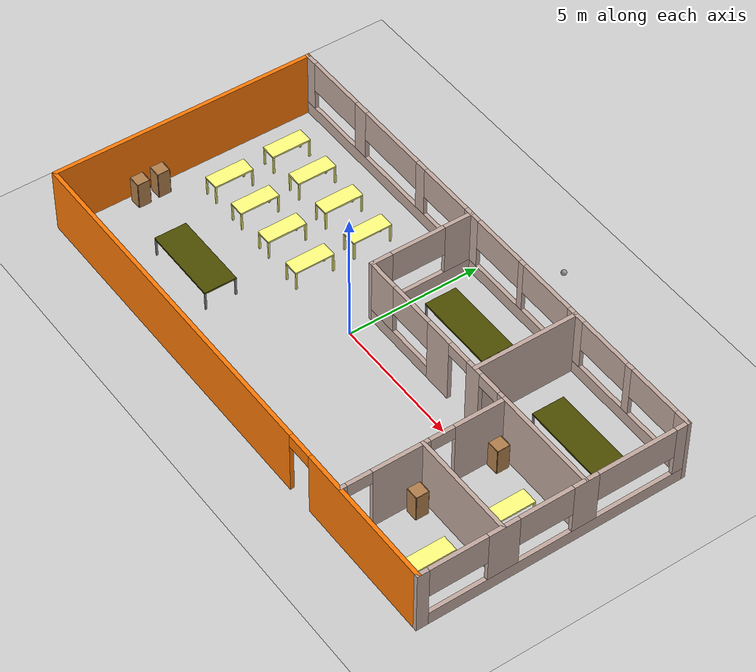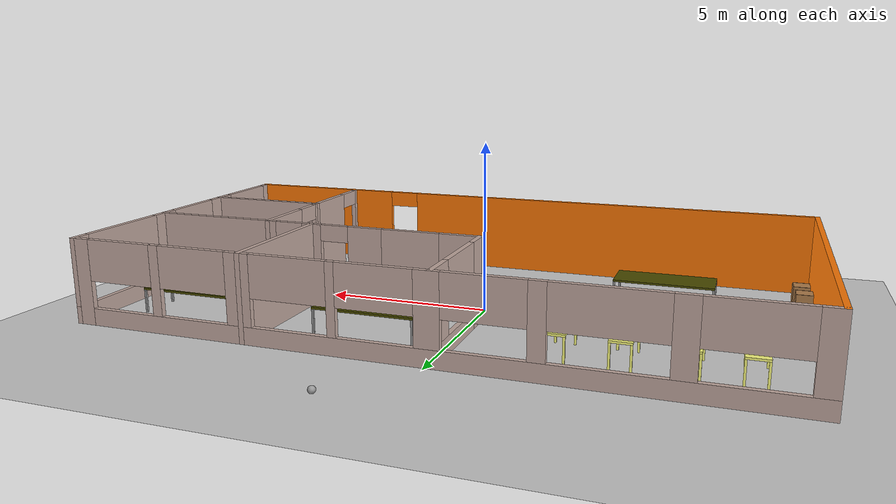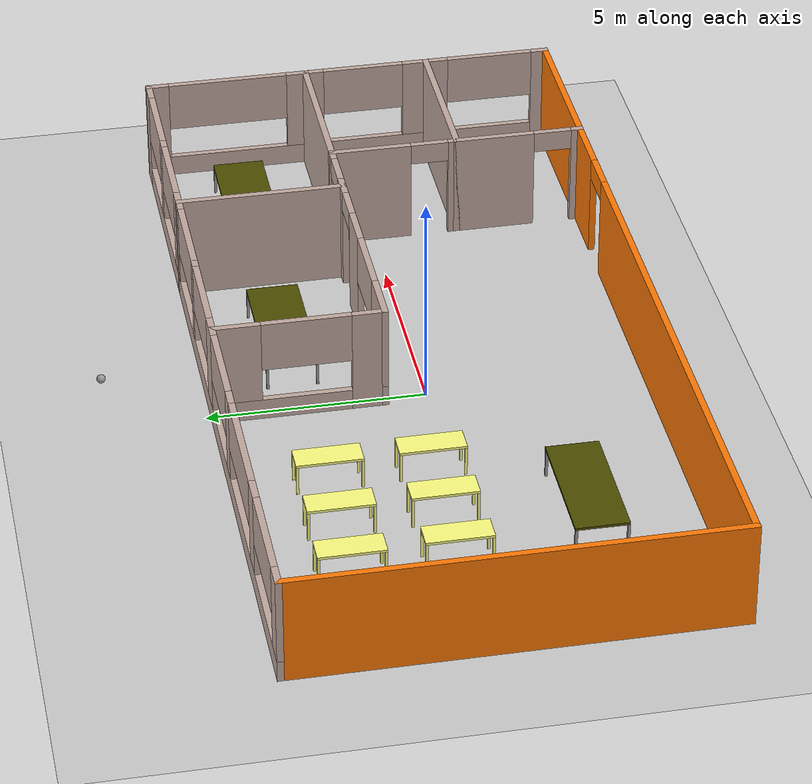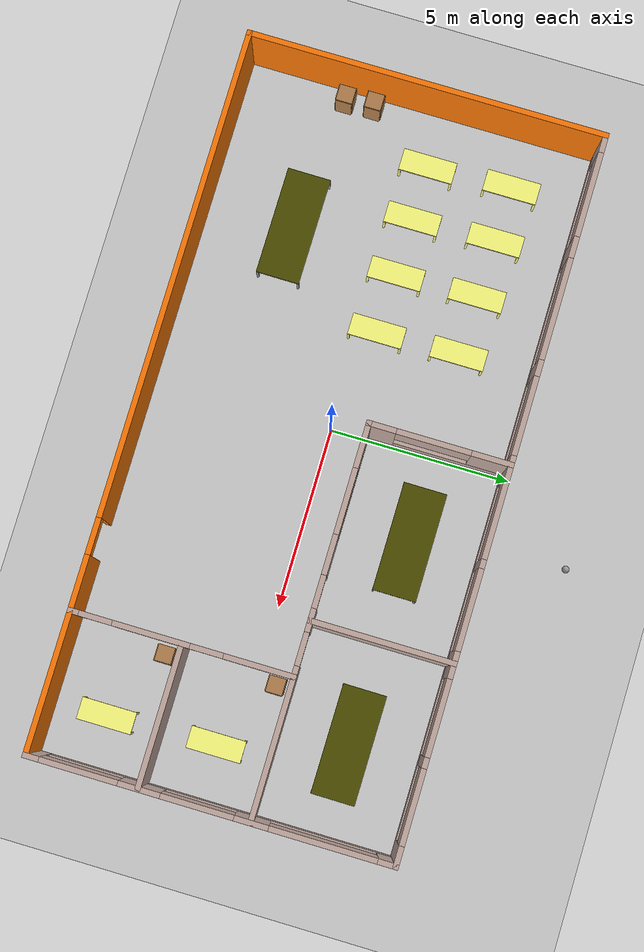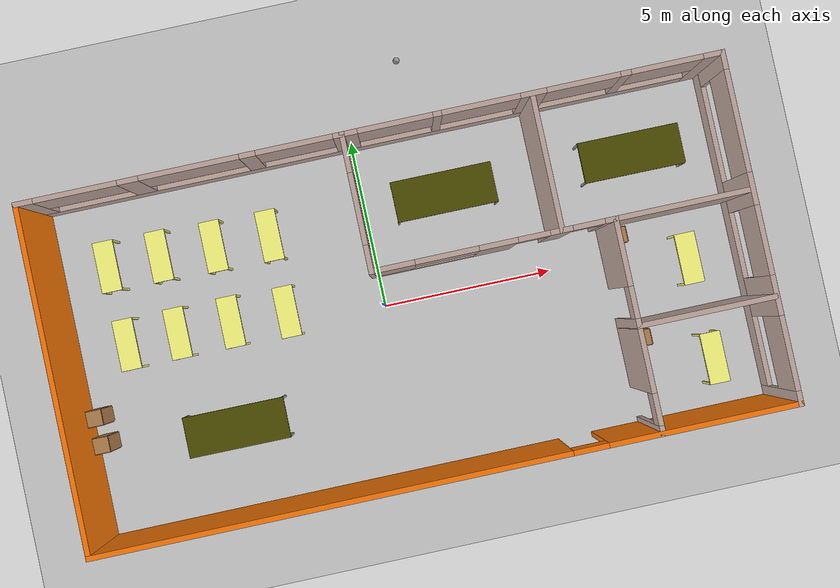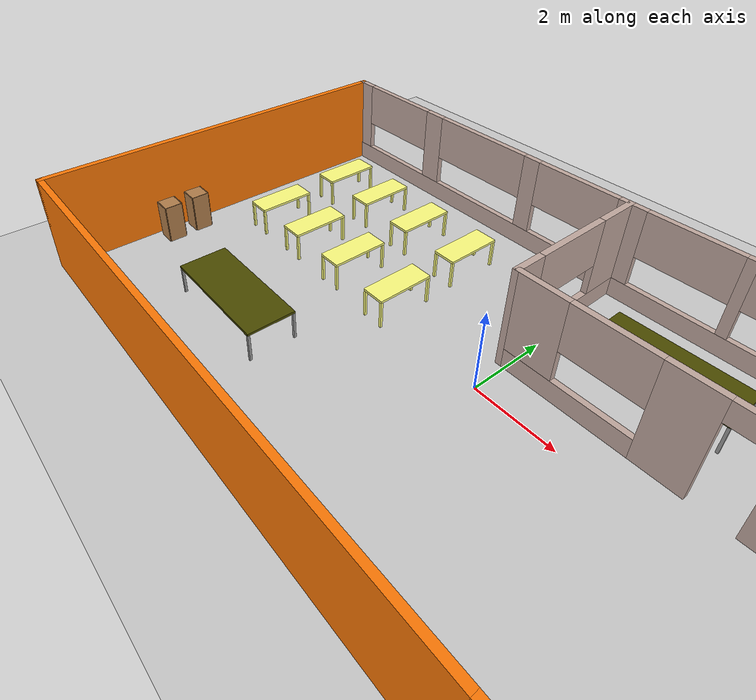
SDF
<sdf version="1.6">
 <world name="default">
  <plugin name="welcome" filename="libwelcome.so"/>
  <light name="sun" type="directional">
   <pose>0 0 10 0 -0 0</pose>
   <diffuse>0.8 0.8 0.8 1</diffuse>
   <specular>0.2 0.2 0.2 1</specular>
   <attenuation>
    <range>1000</range>
    <constant>0.9</constant>
    <linear>0.01</linear>
    <quadratic>0.001</quadratic>
   </attenuation>
   <direction>-0.5 0.1 -0.9</direction>
  </light>
  <model name="ground_plane">
   <static>1</static>
   <link name="link">
    <collision name="collision">
     <geometry><plane><normal>0 0 1</normal><size>100 100</size></plane></geometry>
     <surface><friction><ode><mu>100</mu><mu2>50</mu2></ode></friction></surface>
    </collision>
    <visual name="visual">
     <cast_shadows>0</cast_shadows>
     <geometry><plane><normal>0 0 1</normal><size>100 100</size></plane></geometry>
     <material>
      <script><uri>file://media/materials/scripts/gazebo.material</uri><name>Gazebo/Grey</name></script>
     </material>
    </visual>
   </link>
  </model>
  <gravity>0 0 -9.8</gravity>
  <magnetic_field>6e-06 2.3e-05 -4.2e-05</magnetic_field>
  <atmosphere type="adiabatic"/>
  <physics name="default_physics" default="0" type="ode">
   <max_step_size>0.001</max_step_size>
   <real_time_factor>1</real_time_factor>
   <real_time_update_rate>1000</real_time_update_rate>
  </physics>
  <scene><ambient>0.4 0.4 0.4 1</ambient><background>0.7 0.7 0.7 1</background><shadows>1</shadows></scene>
  <spherical_coordinates>
   <surface_model>EARTH_WGS84</surface_model>
   <latitude_deg>0</latitude_deg>
   <longitude_deg>0</longitude_deg>
   <elevation>0</elevation>
   <heading_deg>0</heading_deg>
  </spherical_coordinates>
  <model name="Building">
   <pose>0.620305 -0.11182 0 0 -0 0</pose>
   <link name="Wall_15">
    <pose>0 -4.925 0 0 -0 0</pose>
    <visual name="Wall_15_Visual_0">
     <pose>-3.2125 0 1.25 0 -0 0</pose>
     <geometry><box><size>13.575 0.15 2.5</size></box></geometry>
     <material>
      <script><uri>file://media/materials/scripts/gazebo.material</uri><name>Gazebo/Grey</name></script>
      <ambient>0.996078 0.47451 0.0196078 1</ambient>
     </material>
     <meta><layer>0</layer></meta>
    </visual>
    <collision name="Wall_15_Collision_0">
     <geometry><box><size>13.575 0.15 2.5</size></box></geometry>
     <pose>-3.2125 0 1.25 0 -0 0</pose>
    </collision>
    <visual name="Wall_15_Visual_1">
     <pose>7.2875 0 1.25 0 -0 0</pose>
     <geometry><box><size>5.425 0.15 2.5</size></box></geometry>
     <material>
      <script><uri>file://media/materials/scripts/gazebo.material</uri><name>Gazebo/Grey</name></script>
      <ambient>0.996078 0.47451 0.0196078 1</ambient>
     </material>
     <meta><layer>0</layer></meta>
    </visual>
    <collision name="Wall_15_Collision_1">
     <geometry><box><size>5.425 0.15 2.5</size></box></geometry>
     <pose>7.2875 0 1.25 0 -0 0</pose>
    </collision>
    <visual name="Wall_15_Visual_2">
     <pose>4.075 0 2.25 0 -0 0</pose>
     <geometry><box><size>1 0.15 0.5</size></box></geometry>
     <material>
      <script><uri>file://media/materials/scripts/gazebo.material</uri><name>Gazebo/Grey</name></script>
      <ambient>0.996078 0.47451 0.0196078 1</ambient>
     </material>
     <meta><layer>0</layer></meta>
    </visual>
    <collision name="Wall_15_Collision_2">
     <geometry><box><size>1 0.15 0.5</size></box></geometry>
     <pose>4.075 0 2.25 0 -0 0</pose>
    </collision>
   </link>
   <link name="Wall_18">
    <pose>9.925 0 0 0 -0 1.5708</pose>
    <visual name="Wall_18_Visual_0">
     <pose>-4.78258 0 1.25 0 -0 0</pose>
     <geometry><box><size>0.434845 0.15 2.5</size></box></geometry>
     <material>
      <script><uri>file://media/materials/scripts/gazebo.material</uri><name>Gazebo/Grey</name></script>
      <ambient>0.760784 0.662745 0.627451 1</ambient>
     </material>
     <meta><layer>0</layer></meta>
    </visual>
    <collision name="Wall_18_Collision_0">
     <geometry><box><size>0.434845 0.15 2.5</size></box></geometry>
     <pose>-4.78258 0 1.25 0 -0 0</pose>
    </collision>
    <visual name="Wall_18_Visual_1">
     <pose>0.217422 0 0.25 0 -0 0</pose>
     <geometry><box><size>9.56516 0.15 0.5</size></box></geometry>
     <material>
      <script><uri>file://media/materials/scripts/gazebo.material</uri><name>Gazebo/Grey</name></script>
      <ambient>0.760784 0.662745 0.627451 1</ambient>
     </material>
     <meta><layer>0</layer></meta>
    </visual>
    <collision name="Wall_18_Collision_1">
     <geometry><box><size>9.56516 0.15 0.5</size></box></geometry>
     <pose>0.217422 0 0.25 0 -0 0</pose>
    </collision>
    <visual name="Wall_18_Visual_2">
     <pose>-1.89711 0 1.5 0 -0 0</pose>
     <geometry><box><size>1.13074 0.15 2</size></box></geometry>
     <material>
      <script><uri>file://media/materials/scripts/gazebo.material</uri><name>Gazebo/Grey</name></script>
      <ambient>0.760784 0.662745 0.627451 1</ambient>
     </material>
     <meta><layer>0</layer></meta>
    </visual>
    <collision name="Wall_18_Collision_2">
     <geometry><box><size>1.13074 0.15 2</size></box></geometry>
     <pose>-1.89711 0 1.5 0 -0 0</pose>
    </collision>
    <visual name="Wall_18_Visual_3">
     <pose>1.09205 0 1.5 0 -0 0</pose>
     <geometry><box><size>0.921385 0.15 2</size></box></geometry>
     <material>
      <script><uri>file://media/materials/scripts/gazebo.material</uri><name>Gazebo/Grey</name></script>
      <ambient>0.760784 0.662745 0.627451 1</ambient>
     </material>
     <meta><layer>0</layer></meta>
    </visual>
    <collision name="Wall_18_Collision_3">
     <geometry><box><size>0.921385 0.15 2</size></box></geometry>
     <pose>1.09205 0 1.5 0 -0 0</pose>
    </collision>
    <visual name="Wall_18_Visual_4">
     <pose>4.72316 0 1.5 0 -0 0</pose>
     <geometry><box><size>0.553684 0.15 2</size></box></geometry>
     <material>
      <script><uri>file://media/materials/scripts/gazebo.material</uri><name>Gazebo/Grey</name></script>
      <ambient>0.760784 0.662745 0.627451 1</ambient>
     </material>
     <meta><layer>0</layer></meta>
    </visual>
    <collision name="Wall_18_Collision_4">
     <geometry><box><size>0.553684 0.15 2</size></box></geometry>
     <pose>4.72316 0 1.5 0 -0 0</pose>
    </collision>
    <visual name="Wall_18_Visual_5">
     <pose>-3.51382 0 1.9 0 -0 0</pose>
     <geometry><box><size>2.10267 0.15 1.2</size></box></geometry>
     <material>
      <script><uri>file://media/materials/scripts/gazebo.material</uri><name>Gazebo/Grey</name></script>
      <ambient>0.760784 0.662745 0.627451 1</ambient>
     </material>
     <meta><layer>0</layer></meta>
    </visual>
    <collision name="Wall_18_Collision_5">
     <geometry><box><size>2.10267 0.15 1.2</size></box></geometry>
     <pose>-3.51382 0 1.9 0 -0 0</pose>
    </collision>
    <visual name="Wall_18_Visual_6">
     <pose>-0.350194 0 1.9 0 -0 0</pose>
     <geometry><box><size>1.9631 0.15 1.2</size></box></geometry>
     <material>
      <script><uri>file://media/materials/scripts/gazebo.material</uri><name>Gazebo/Grey</name></script>
      <ambient>0.760784 0.662745 0.627451 1</ambient>
     </material>
     <meta><layer>0</layer></meta>
    </visual>
    <collision name="Wall_18_Collision_6">
     <geometry><box><size>1.9631 0.15 1.2</size></box></geometry>
     <pose>-0.350194 0 1.9 0 -0 0</pose>
    </collision>
    <visual name="Wall_18_Visual_7">
     <pose>2.99953 0 1.9 0 -0 0</pose>
     <geometry><box><size>2.89358 0.15 1.2</size></box></geometry>
     <material>
      <script><uri>file://media/materials/scripts/gazebo.material</uri><name>Gazebo/Grey</name></script>
      <ambient>0.760784 0.662745 0.627451 1</ambient>
     </material>
     <meta><layer>0</layer></meta>
    </visual>
    <collision name="Wall_18_Collision_7">
     <geometry><box><size>2.89358 0.15 1.2</size></box></geometry>
     <pose>2.99953 0 1.9 0 -0 0</pose>
    </collision>
   </link>
   <link name="Wall_19">
    <pose>0 4.925 0 0 -0 3.14159</pose>
    <visual name="Wall_19_Visual_0">
     <pose>-9.69596 0 1.25 0 -0 0</pose>
     <geometry><box><size>0.608075 0.15 2.5</size></box></geometry>
     <material>
      <script><uri>file://media/materials/scripts/gazebo.material</uri><name>Gazebo/Grey</name></script>
      <ambient>0.760784 0.662745 0.627451 1</ambient>
     </material>
     <meta><layer>0</layer></meta>
    </visual>
    <collision name="Wall_19_Collision_0">
     <geometry><box><size>0.608075 0.15 2.5</size></box></geometry>
     <pose>-9.69596 0 1.25 0 -0 0</pose>
    </collision>
    <visual name="Wall_19_Visual_1">
     <pose>0.304038 0 0.25 0 -0 0</pose>
     <geometry><box><size>19.3919 0.15 0.5</size></box></geometry>
     <material>
      <script><uri>file://media/materials/scripts/gazebo.material</uri><name>Gazebo/Grey</name></script>
      <ambient>0.760784 0.662745 0.627451 1</ambient>
     </material>
     <meta><layer>0</layer></meta>
    </visual>
    <collision name="Wall_19_Collision_1">
     <geometry><box><size>19.3919 0.15 0.5</size></box></geometry>
     <pose>0.304038 0 0.25 0 -0 0</pose>
    </collision>
    <visual name="Wall_19_Visual_2">
     <pose>-7.21239 0 1.5 0 -0 0</pose>
     <geometry><box><size>0.293312 0.15 2</size></box></geometry>
     <material>
      <script><uri>file://media/materials/scripts/gazebo.material</uri><name>Gazebo/Grey</name></script>
      <ambient>0.760784 0.662745 0.627451 1</ambient>
     </material>
     <meta><layer>0</layer></meta>
    </visual>
    <collision name="Wall_19_Collision_2">
     <geometry><box><size>0.293312 0.15 2</size></box></geometry>
     <pose>-7.21239 0 1.5 0 -0 0</pose>
    </collision>
    <visual name="Wall_19_Visual_3">
     <pose>-4.61868 0 1.5 0 -0 0</pose>
     <geometry><box><size>0.735289 0.15 2</size></box></geometry>
     <material>
      <script><uri>file://media/materials/scripts/gazebo.material</uri><name>Gazebo/Grey</name></script>
      <ambient>0.760784 0.662745 0.627451 1</ambient>
     </material>
     <meta><layer>0</layer></meta>
    </visual>
    <collision name="Wall_19_Collision_3">
     <geometry><box><size>0.735289 0.15 2</size></box></geometry>
     <pose>-4.61868 0 1.5 0 -0 0</pose>
    </collision>
    <visual name="Wall_19_Visual_4">
     <pose>-1.90866 0 1.5 0 -0 0</pose>
     <geometry><box><size>0.246788 0.15 2</size></box></geometry>
     <material>
      <script><uri>file://media/materials/scripts/gazebo.material</uri><name>Gazebo/Grey</name></script>
      <ambient>0.760784 0.662745 0.627451 1</ambient>
     </material>
     <meta><layer>0</layer></meta>
    </visual>
    <collision name="Wall_19_Collision_4">
     <geometry><box><size>0.246788 0.15 2</size></box></geometry>
     <pose>-1.90866 0 1.5 0 -0 0</pose>
    </collision>
    <visual name="Wall_19_Visual_5">
     <pose>0.68505 0 1.5 0 -0 0</pose>
     <geometry><box><size>0.688765 0.15 2</size></box></geometry>
     <material>
      <script><uri>file://media/materials/scripts/gazebo.material</uri><name>Gazebo/Grey</name></script>
      <ambient>0.760784 0.662745 0.627451 1</ambient>
     </material>
     <meta><layer>0</layer></meta>
    </visual>
    <collision name="Wall_19_Collision_5">
     <geometry><box><size>0.688765 0.15 2</size></box></geometry>
     <pose>0.68505 0 1.5 0 -0 0</pose>
    </collision>
    <visual name="Wall_19_Visual_6">
     <pose>3.42996 0 1.5 0 -0 0</pose>
     <geometry><box><size>0.456146 0.15 2</size></box></geometry>
     <material>
      <script><uri>file://media/materials/scripts/gazebo.material</uri><name>Gazebo/Grey</name></script>
      <ambient>0.760784 0.662745 0.627451 1</ambient>
     </material>
     <meta><layer>0</layer></meta>
    </visual>
    <collision name="Wall_19_Collision_6">
     <geometry><box><size>0.456146 0.15 2</size></box></geometry>
     <pose>3.42996 0 1.5 0 -0 0</pose>
    </collision>
    <visual name="Wall_19_Visual_7">
     <pose>6.77968 0 1.5 0 -0 0</pose>
     <geometry><box><size>0.595718 0.15 2</size></box></geometry>
     <material>
      <script><uri>file://media/materials/scripts/gazebo.material</uri><name>Gazebo/Grey</name></script>
      <ambient>0.760784 0.662745 0.627451 1</ambient>
     </material>
     <meta><layer>0</layer></meta>
    </visual>
    <collision name="Wall_19_Collision_7">
     <geometry><box><size>0.595718 0.15 2</size></box></geometry>
     <pose>6.77968 0 1.5 0 -0 0</pose>
    </collision>
    <visual name="Wall_19_Visual_8">
     <pose>9.71805 0 1.5 0 -0 0</pose>
     <geometry><box><size>0.563908 0.15 2</size></box></geometry>
     <material>
      <script><uri>file://media/materials/scripts/gazebo.material</uri><name>Gazebo/Grey</name></script>
      <ambient>0.760784 0.662745 0.627451 1</ambient>
     </material>
     <meta><layer>0</layer></meta>
    </visual>
    <collision name="Wall_19_Collision_8">
     <geometry><box><size>0.563908 0.15 2</size></box></geometry>
     <pose>9.71805 0 1.5 0 -0 0</pose>
    </collision>
    <visual name="Wall_19_Visual_9">
     <pose>-8.37548 0 1.9 0 -0 0</pose>
     <geometry><box><size>2.03288 0.15 1.2</size></box></geometry>
     <material>
      <script><uri>file://media/materials/scripts/gazebo.material</uri><name>Gazebo/Grey</name></script>
      <ambient>0.760784 0.662745 0.627451 1</ambient>
     </material>
     <meta><layer>0</layer></meta>
    </visual>
    <collision name="Wall_19_Collision_9">
     <geometry><box><size>2.03288 0.15 1.2</size></box></geometry>
     <pose>-8.37548 0 1.9 0 -0 0</pose>
    </collision>
    <visual name="Wall_19_Visual_10">
     <pose>-6.02602 0 1.9 0 -0 0</pose>
     <geometry><box><size>2.07941 0.15 1.2</size></box></geometry>
     <material>
      <script><uri>file://media/materials/scripts/gazebo.material</uri><name>Gazebo/Grey</name></script>
      <ambient>0.760784 0.662745 0.627451 1</ambient>
     </material>
     <meta><layer>0</layer></meta>
    </visual>
    <collision name="Wall_19_Collision_10">
     <geometry><box><size>2.07941 0.15 1.2</size></box></geometry>
     <pose>-6.02602 0 1.9 0 -0 0</pose>
    </collision>
    <visual name="Wall_19_Visual_11">
     <pose>-3.14154 0 1.9 0 -0 0</pose>
     <geometry><box><size>2.21898 0.15 1.2</size></box></geometry>
     <material>
      <script><uri>file://media/materials/scripts/gazebo.material</uri><name>Gazebo/Grey</name></script>
      <ambient>0.760784 0.662745 0.627451 1</ambient>
     </material>
     <meta><layer>0</layer></meta>
    </visual>
    <collision name="Wall_19_Collision_11">
     <geometry><box><size>2.21898 0.15 1.2</size></box></geometry>
     <pose>-3.14154 0 1.9 0 -0 0</pose>
    </collision>
    <visual name="Wall_19_Visual_12">
     <pose>-0.722299 0 1.9 0 -0 0</pose>
     <geometry><box><size>2.12593 0.15 1.2</size></box></geometry>
     <material>
      <script><uri>file://media/materials/scripts/gazebo.material</uri><name>Gazebo/Grey</name></script>
      <ambient>0.760784 0.662745 0.627451 1</ambient>
     </material>
     <meta><layer>0</layer></meta>
    </visual>
    <collision name="Wall_19_Collision_12">
     <geometry><box><size>2.12593 0.15 1.2</size></box></geometry>
     <pose>-0.722299 0 1.9 0 -0 0</pose>
    </collision>
    <visual name="Wall_19_Visual_13">
     <pose>2.11566 0 1.9 0 -0 0</pose>
     <geometry><box><size>2.17245 0.15 1.2</size></box></geometry>
     <material>
      <script><uri>file://media/materials/scripts/gazebo.material</uri><name>Gazebo/Grey</name></script>
      <ambient>0.760784 0.662745 0.627451 1</ambient>
     </material>
     <meta><layer>0</layer></meta>
    </visual>
    <collision name="Wall_19_Collision_13">
     <geometry><box><size>2.17245 0.15 1.2</size></box></geometry>
     <pose>2.11566 0 1.9 0 -0 0</pose>
    </collision>
    <visual name="Wall_19_Visual_14">
     <pose>5.06993 0 1.9 0 -0 0</pose>
     <geometry><box><size>2.82379 0.15 1.2</size></box></geometry>
     <material>
      <script><uri>file://media/materials/scripts/gazebo.material</uri><name>Gazebo/Grey</name></script>
      <ambient>0.760784 0.662745 0.627451 1</ambient>
     </material>
     <meta><layer>0</layer></meta>
    </visual>
    <collision name="Wall_19_Collision_14">
     <geometry><box><size>2.82379 0.15 1.2</size></box></geometry>
     <pose>5.06993 0 1.9 0 -0 0</pose>
    </collision>
    <visual name="Wall_19_Visual_15">
     <pose>8.25682 0 1.9 0 -0 0</pose>
     <geometry><box><size>2.35855 0.15 1.2</size></box></geometry>
     <material>
      <script><uri>file://media/materials/scripts/gazebo.material</uri><name>Gazebo/Grey</name></script>
      <ambient>0.760784 0.662745 0.627451 1</ambient>
     </material>
     <meta><layer>0</layer></meta>
    </visual>
    <collision name="Wall_19_Collision_15">
     <geometry><box><size>2.35855 0.15 1.2</size></box></geometry>
     <pose>8.25682 0 1.9 0 -0 0</pose>
    </collision>
   </link>
   <link name="Wall_20">
    <collision name="Wall_20_Collision">
     <geometry><box><size>10 0.15 2.5</size></box></geometry>
     <pose>0 0 1.25 0 -0 0</pose>
    </collision>
    <visual name="Wall_20_Visual">
     <pose>0 0 1.25 0 -0 0</pose>
     <geometry><box><size>10 0.15 2.5</size></box></geometry>
     <material>
      <script><uri>file://media/materials/scripts/gazebo.material</uri><name>Gazebo/Grey</name></script>
      <ambient>0.996078 0.47451 0.0196078 1</ambient>
     </material>
     <meta><layer>0</layer></meta>
    </visual>
    <pose>-9.925 0 0 0 0 -1.5708</pose>
   </link>
   <link name="Wall_37">
    <pose>6.075 -1.925 0 0 -0 1.5708</pose>
    <visual name="Wall_37_Visual_0">
     <pose>-2.92581 0 1.25 0 -0 0</pose>
     <geometry><box><size>0.298377 0.15 2.5</size></box></geometry>
     <material>
      <script><uri>file://media/materials/scripts/gazebo.material</uri><name>Gazebo/Grey</name></script>
      <ambient>0.760784 0.662745 0.627451 1</ambient>
     </material>
     <meta><layer>0</layer></meta>
    </visual>
    <collision name="Wall_37_Collision_0">
     <geometry><box><size>0.298377 0.15 2.5</size></box></geometry>
     <pose>-2.92581 0 1.25 0 -0 0</pose>
    </collision>
    <visual name="Wall_37_Visual_1">
     <pose>-0.831526 0 1.25 0 -0 0</pose>
     <geometry><box><size>2.0902 0.15 2.5</size></box></geometry>
     <material>
      <script><uri>file://media/materials/scripts/gazebo.material</uri><name>Gazebo/Grey</name></script>
      <ambient>0.760784 0.662745 0.627451 1</ambient>
     </material>
     <meta><layer>0</layer></meta>
    </visual>
    <collision name="Wall_37_Collision_1">
     <geometry><box><size>2.0902 0.15 2.5</size></box></geometry>
     <pose>-0.831526 0 1.25 0 -0 0</pose>
    </collision>
    <visual name="Wall_37_Visual_2">
     <pose>2.09429 0 1.25 0 -0 0</pose>
     <geometry><box><size>1.96143 0.15 2.5</size></box></geometry>
     <material>
      <script><uri>file://media/materials/scripts/gazebo.material</uri><name>Gazebo/Grey</name></script>
      <ambient>0.760784 0.662745 0.627451 1</ambient>
     </material>
     <meta><layer>0</layer></meta>
    </visual>
    <collision name="Wall_37_Collision_2">
     <geometry><box><size>1.96143 0.15 2.5</size></box></geometry>
     <pose>2.09429 0 1.25 0 -0 0</pose>
    </collision>
    <visual name="Wall_37_Visual_3">
     <pose>-2.32662 0 2.25 0 -0 0</pose>
     <geometry><box><size>0.9 0.15 0.5</size></box></geometry>
     <material>
      <script><uri>file://media/materials/scripts/gazebo.material</uri><name>Gazebo/Grey</name></script>
      <ambient>0.760784 0.662745 0.627451 1</ambient>
     </material>
     <meta><layer>0</layer></meta>
    </visual>
    <collision name="Wall_37_Collision_3">
     <geometry><box><size>0.9 0.15 0.5</size></box></geometry>
     <pose>-2.32662 0 2.25 0 -0 0</pose>
    </collision>
    <visual name="Wall_37_Visual_4">
     <pose>0.663572 0 2.25 0 -0 0</pose>
     <geometry><box><size>0.9 0.15 0.5</size></box></geometry>
     <material>
      <script><uri>file://media/materials/scripts/gazebo.material</uri><name>Gazebo/Grey</name></script>
      <ambient>0.760784 0.662745 0.627451 1</ambient>
     </material>
     <meta><layer>0</layer></meta>
    </visual>
    <collision name="Wall_37_Collision_4">
     <geometry><box><size>0.9 0.15 0.5</size></box></geometry>
     <pose>0.663572 0 2.25 0 -0 0</pose>
    </collision>
   </link>
   <link name="Wall_39">
    <collision name="Wall_39_Collision">
     <geometry><box><size>4 0.15 2.5</size></box></geometry>
     <pose>0 0 1.25 0 -0 0</pose>
    </collision>
    <visual name="Wall_39_Visual">
     <pose>0 0 1.25 0 -0 0</pose>
     <geometry><box><size>4 0.15 2.5</size></box></geometry>
     <material>
      <script><uri>file://media/materials/scripts/gazebo.material</uri><name>Gazebo/Grey</name></script>
      <ambient>0.760784 0.662745 0.627451 1</ambient>
     </material>
     <meta><layer>0</layer></meta>
    </visual>
    <pose>8 -1.925 0 0 -0 0</pose>
   </link>
   <link name="Wall_41">
    <collision name="Wall_41_Collision">
     <geometry><box><size>3.998 0.15 2.5</size></box></geometry>
     <pose>0 0 1.25 0 -0 0</pose>
    </collision>
    <visual name="Wall_41_Visual">
     <pose>0 0 1.25 0 -0 0</pose>
     <geometry><box><size>3.998 0.15 2.5</size></box></geometry>
     <material>
      <script><uri>file://media/materials/scripts/gazebo.material</uri><name>Gazebo/Grey</name></script>
      <ambient>0.760784 0.662745 0.627451 1</ambient>
     </material>
     <meta><layer>0</layer></meta>
    </visual>
    <pose>7.999 1.075 0 0 -0 0</pose>
   </link>
   <link name="Wall_43">
    <pose>2.65 1.075 0 0 -0 3.14159</pose>
    <visual name="Wall_43_Visual_0">
     <pose>-3.31508 0 1.25 0 -0 0</pose>
     <geometry><box><size>0.36983 0.15 2.5</size></box></geometry>
     <material>
      <script><uri>file://media/materials/scripts/gazebo.material</uri><name>Gazebo/Grey</name></script>
      <ambient>0.760784 0.662745 0.627451 1</ambient>
     </material>
     <meta><layer>0</layer></meta>
    </visual>
    <collision name="Wall_43_Collision_0">
     <geometry><box><size>0.36983 0.15 2.5</size></box></geometry>
     <pose>-3.31508 0 1.25 0 -0 0</pose>
    </collision>
    <visual name="Wall_43_Visual_1">
     <pose>-1.91151 0 1.25 0 -0 0</pose>
     <geometry><box><size>0.637312 0.15 2.5</size></box></geometry>
     <material>
      <script><uri>file://media/materials/scripts/gazebo.material</uri><name>Gazebo/Grey</name></script>
      <ambient>0.760784 0.662745 0.627451 1</ambient>
     </material>
     <meta><layer>0</layer></meta>
    </visual>
    <collision name="Wall_43_Collision_1">
     <geometry><box><size>0.637312 0.15 2.5</size></box></geometry>
     <pose>-1.91151 0 1.25 0 -0 0</pose>
    </collision>
    <visual name="Wall_43_Visual_2">
     <pose>-0.146681 0 1.25 0 -0 0</pose>
     <geometry><box><size>1.09235 0.15 2.5</size></box></geometry>
     <material>
      <script><uri>file://media/materials/scripts/gazebo.material</uri><name>Gazebo/Grey</name></script>
      <ambient>0.760784 0.662745 0.627451 1</ambient>
     </material>
     <meta><layer>0</layer></meta>
    </visual>
    <collision name="Wall_43_Collision_2">
     <geometry><box><size>1.09235 0.15 2.5</size></box></geometry>
     <pose>-0.146681 0 1.25 0 -0 0</pose>
    </collision>
    <visual name="Wall_43_Visual_3">
     <pose>1.94975 0 0.25 0 -0 0</pose>
     <geometry><box><size>3.1005 0.15 0.5</size></box></geometry>
     <material>
      <script><uri>file://media/materials/scripts/gazebo.material</uri><name>Gazebo/Grey</name></script>
      <ambient>0.760784 0.662745 0.627451 1</ambient>
     </material>
     <meta><layer>0</layer></meta>
    </visual>
    <collision name="Wall_43_Collision_3">
     <geometry><box><size>3.1005 0.15 0.5</size></box></geometry>
     <pose>1.94975 0 0.25 0 -0 0</pose>
    </collision>
    <visual name="Wall_43_Visual_4">
     <pose>2.84988 0 1.5 0 -0 0</pose>
     <geometry><box><size>1.30024 0.15 2</size></box></geometry>
     <material>
      <script><uri>file://media/materials/scripts/gazebo.material</uri><name>Gazebo/Grey</name></script>
      <ambient>0.760784 0.662745 0.627451 1</ambient>
     </material>
     <meta><layer>0</layer></meta>
    </visual>
    <collision name="Wall_43_Collision_4">
     <geometry><box><size>1.30024 0.15 2</size></box></geometry>
     <pose>2.84988 0 1.5 0 -0 0</pose>
    </collision>
    <visual name="Wall_43_Visual_5">
     <pose>1.29963 0 1.9 0 -0 0</pose>
     <geometry><box><size>1.80026 0.15 1.2</size></box></geometry>
     <material>
      <script><uri>file://media/materials/scripts/gazebo.material</uri><name>Gazebo/Grey</name></script>
      <ambient>0.760784 0.662745 0.627451 1</ambient>
     </material>
     <meta><layer>0</layer></meta>
    </visual>
    <collision name="Wall_43_Collision_5">
     <geometry><box><size>1.80026 0.15 1.2</size></box></geometry>
     <pose>1.29963 0 1.9 0 -0 0</pose>
    </collision>
    <visual name="Wall_43_Visual_6">
     <pose>-2.68017 0 2.25 0 -0 0</pose>
     <geometry><box><size>0.9 0.15 0.5</size></box></geometry>
     <material>
      <script><uri>file://media/materials/scripts/gazebo.material</uri><name>Gazebo/Grey</name></script>
      <ambient>0.760784 0.662745 0.627451 1</ambient>
     </material>
     <meta><layer>0</layer></meta>
    </visual>
    <collision name="Wall_43_Collision_6">
     <geometry><box><size>0.9 0.15 0.5</size></box></geometry>
     <pose>-2.68017 0 2.25 0 -0 0</pose>
    </collision>
    <visual name="Wall_43_Visual_7">
     <pose>-1.14286 0 2.25 0 -0 0</pose>
     <geometry><box><size>0.9 0.15 0.5</size></box></geometry>
     <material>
      <script><uri>file://media/materials/scripts/gazebo.material</uri><name>Gazebo/Grey</name></script>
      <ambient>0.760784 0.662745 0.627451 1</ambient>
     </material>
     <meta><layer>0</layer></meta>
    </visual>
    <collision name="Wall_43_Collision_7">
     <geometry><box><size>0.9 0.15 0.5</size></box></geometry>
     <pose>-1.14286 0 2.25 0 -0 0</pose>
    </collision>
   </link>
   <link name="Wall_45">
    <pose>-0.775 3 0 0 -0 1.5708</pose>
    <visual name="Wall_45_Visual_0">
     <pose>-1.58987 0 1.25 0 -0 0</pose>
     <geometry><box><size>0.820252 0.15 2.5</size></box></geometry>
     <material>
      <script><uri>file://media/materials/scripts/gazebo.material</uri><name>Gazebo/Grey</name></script>
      <ambient>0.760784 0.662745 0.627451 1</ambient>
     </material>
     <meta><layer>0</layer></meta>
    </visual>
    <collision name="Wall_45_Collision_0">
     <geometry><box><size>0.820252 0.15 2.5</size></box></geometry>
     <pose>-1.58987 0 1.25 0 -0 0</pose>
    </collision>
    <visual name="Wall_45_Visual_1">
     <pose>0.410126 0 0.25 0 -0 0</pose>
     <geometry><box><size>3.17975 0.15 0.5</size></box></geometry>
     <material>
      <script><uri>file://media/materials/scripts/gazebo.material</uri><name>Gazebo/Grey</name></script>
      <ambient>0.760784 0.662745 0.627451 1</ambient>
     </material>
     <meta><layer>0</layer></meta>
    </visual>
    <collision name="Wall_45_Collision_1">
     <geometry><box><size>3.17975 0.15 0.5</size></box></geometry>
     <pose>0.410126 0 0.25 0 -0 0</pose>
    </collision>
    <visual name="Wall_45_Visual_2">
     <pose>1.42657 0 1.5 0 -0 0</pose>
     <geometry><box><size>1.14686 0.15 2</size></box></geometry>
     <material>
      <script><uri>file://media/materials/scripts/gazebo.material</uri><name>Gazebo/Grey</name></script>
      <ambient>0.760784 0.662745 0.627451 1</ambient>
     </material>
     <meta><layer>0</layer></meta>
    </visual>
    <collision name="Wall_45_Collision_2">
     <geometry><box><size>1.14686 0.15 2</size></box></geometry>
     <pose>1.42657 0 1.5 0 -0 0</pose>
    </collision>
    <visual name="Wall_45_Visual_3">
     <pose>-0.163306 0 1.9 0 -0 0</pose>
     <geometry><box><size>2.03288 0.15 1.2</size></box></geometry>
     <material>
      <script><uri>file://media/materials/scripts/gazebo.material</uri><name>Gazebo/Grey</name></script>
      <ambient>0.760784 0.662745 0.627451 1</ambient>
     </material>
     <meta><layer>0</layer></meta>
    </visual>
    <collision name="Wall_45_Collision_3">
     <geometry><box><size>2.03288 0.15 1.2</size></box></geometry>
     <pose>-0.163306 0 1.9 0 -0 0</pose>
    </collision>
   </link>
   <link name="Wall_48">
    <collision name="Wall_48_Collision">
     <geometry><box><size>4 0.15 2.5</size></box></geometry>
     <pose>0 0 1.25 0 -0 0</pose>
    </collision>
    <visual name="Wall_48_Visual">
     <pose>0 0 1.25 0 -0 0</pose>
     <geometry><box><size>4 0.15 2.5</size></box></geometry>
     <material>
      <script><uri>file://media/materials/scripts/gazebo.material</uri><name>Gazebo/Grey</name></script>
      <ambient>0.760784 0.662745 0.627451 1</ambient>
     </material>
     <meta><layer>0</layer></meta>
    </visual>
    <pose>4.575 3 0 0 -0 1.5708</pose>
   </link>
   <static>1</static>
  </model>
  <model name="table">
   <link name="link_0">
    <pose>0 2e-06 0.304 0 -0 0</pose>
    <inertial>
     <mass>1</mass>
     <inertia>
      <ixx>0.166667</ixx>
      <ixy>0</ixy>
      <ixz>0</ixz>
      <iyy>0.166667</iyy>
      <iyz>0</iyz>
      <izz>0.166667</izz>
     </inertia>
    </inertial>
    <visual name="visual">
     <geometry><box><size>0.6 1.5 0.06</size></box></geometry>
     <material>
      <lighting>1</lighting>
      <script><uri>file://media/materials/scripts/gazebo.material</uri><name>Gazebo/Grey</name></script>
      <shader type="pixel"><normal_map>__default__</normal_map></shader>
      <ambient>1 1 0.5 1</ambient>
      <diffuse>0.7 0.7 0.7 1</diffuse>
      <specular>0.01 0.01 0.01 1</specular>
      <emissive>0 0 0 1</emissive>
     </material>
    </visual>
    <collision name="collision">
     <geometry><box><size>0.6 1.5 0.06</size></box></geometry>
     <surface>
      <friction>
       <ode><mu>1</mu><mu2>1</mu2><fdir1>0 0 0</fdir1><slip1>0</slip1><slip2>0</slip2></ode>
       <torsional>
        <coefficient>1</coefficient>
        <patch_radius>0</patch_radius>
        <surface_radius>0</surface_radius>
        <use_patch_radius>1</use_patch_radius>
        <ode><slip>0</slip></ode>
       </torsional>
      </friction>
      <bounce><restitution_coefficient>0</restitution_coefficient><threshold>1e+06</threshold></bounce>
      <contact>
       <collide_without_contact>0</collide_without_contact>
       <collide_without_contact_bitmask>1</collide_without_contact_bitmask>
       <collide_bitmask>1</collide_bitmask>
       <ode>
        <soft_cfm>0</soft_cfm>
        <soft_erp>0.2</soft_erp>
        <kp>1e+13</kp>
        <kd>1</kd>
        <max_vel>0.01</max_vel>
        <min_depth>0</min_depth>
       </ode>
       <bullet>
        <split_impulse>1</split_impulse>
        <split_impulse_penetration_threshold>-0.01</split_impulse_penetration_threshold>
        <soft_cfm>0</soft_cfm>
        <soft_erp>0.2</soft_erp>
        <kp>1e+13</kp>
        <kd>1</kd>
       </bullet>
      </contact>
     </surface>
    </collision>
   </link>
   <link name="link_1">
    <pose>0.27 -0.719998 -0.076 0 -0 0</pose>
    <inertial>
     <mass>1</mass>
     <inertia>
      <ixx>0.166667</ixx>
      <ixy>0</ixy>
      <ixz>0</ixz>
      <iyy>0.166667</iyy>
      <iyz>0</iyz>
      <izz>0.166667</izz>
     </inertia>
    </inertial>
    <visual name="visual">
     <geometry><box><size>0.06 0.06 0.7</size></box></geometry>
     <material>
      <lighting>1</lighting>
      <script><uri>file://media/materials/scripts/gazebo.material</uri><name>Gazebo/Grey</name></script>
      <shader type="pixel"><normal_map>__default__</normal_map></shader>
      <ambient>1 1 0.5 1</ambient>
      <diffuse>0.7 0.7 0.7 1</diffuse>
      <specular>0.01 0.01 0.01 1</specular>
      <emissive>0 0 0 1</emissive>
     </material>
    </visual>
    <collision name="collision">
     <geometry><box><size>0.06 0.06 0.7</size></box></geometry>
     <surface>
      <friction>
       <ode><mu>1</mu><mu2>1</mu2><fdir1>0 0 0</fdir1><slip1>0</slip1><slip2>0</slip2></ode>
       <torsional>
        <coefficient>1</coefficient>
        <patch_radius>0</patch_radius>
        <surface_radius>0</surface_radius>
        <use_patch_radius>1</use_patch_radius>
        <ode><slip>0</slip></ode>
       </torsional>
      </friction>
      <bounce><restitution_coefficient>0</restitution_coefficient><threshold>1e+06</threshold></bounce>
      <contact>
       <collide_without_contact>0</collide_without_contact>
       <collide_without_contact_bitmask>1</collide_without_contact_bitmask>
       <collide_bitmask>1</collide_bitmask>
       <ode>
        <soft_cfm>0</soft_cfm>
        <soft_erp>0.2</soft_erp>
        <kp>1e+13</kp>
        <kd>1</kd>
        <max_vel>0.01</max_vel>
        <min_depth>0</min_depth>
       </ode>
       <bullet>
        <split_impulse>1</split_impulse>
        <split_impulse_penetration_threshold>-0.01</split_impulse_penetration_threshold>
        <soft_cfm>0</soft_cfm>
        <soft_erp>0.2</soft_erp>
        <kp>1e+13</kp>
        <kd>1</kd>
       </bullet>
      </contact>
     </surface>
    </collision>
   </link>
   <link name="link_1_clone">
    <pose>-0.27 -0.719998 -0.076 0 -0 0</pose>
    <inertial>
     <mass>1</mass>
     <inertia>
      <ixx>0.166667</ixx>
      <ixy>0</ixy>
      <ixz>0</ixz>
      <iyy>0.166667</iyy>
      <iyz>0</iyz>
      <izz>0.166667</izz>
     </inertia>
    </inertial>
    <visual name="visual">
     <geometry><box><size>0.06 0.06 0.7</size></box></geometry>
     <material>
      <lighting>1</lighting>
      <script><uri>file://media/materials/scripts/gazebo.material</uri><name>Gazebo/Grey</name></script>
      <shader type="pixel"><normal_map>__default__</normal_map></shader>
      <ambient>1 1 0.5 1</ambient>
      <diffuse>0.7 0.7 0.7 1</diffuse>
      <specular>0.01 0.01 0.01 1</specular>
      <emissive>0 0 0 1</emissive>
     </material>
    </visual>
    <collision name="collision">
     <geometry><box><size>0.06 0.06 0.7</size></box></geometry>
     <surface>
      <friction>
       <ode><mu>1</mu><mu2>1</mu2><fdir1>0 0 0</fdir1><slip1>0</slip1><slip2>0</slip2></ode>
       <torsional>
        <coefficient>1</coefficient>
        <patch_radius>0</patch_radius>
        <surface_radius>0</surface_radius>
        <use_patch_radius>1</use_patch_radius>
        <ode><slip>0</slip></ode>
       </torsional>
      </friction>
      <bounce><restitution_coefficient>0</restitution_coefficient><threshold>1e+06</threshold></bounce>
      <contact>
       <collide_without_contact>0</collide_without_contact>
       <collide_without_contact_bitmask>1</collide_without_contact_bitmask>
       <collide_bitmask>1</collide_bitmask>
       <ode>
        <soft_cfm>0</soft_cfm>
        <soft_erp>0.2</soft_erp>
        <kp>1e+13</kp>
        <kd>1</kd>
        <max_vel>0.01</max_vel>
        <min_depth>0</min_depth>
       </ode>
       <bullet>
        <split_impulse>1</split_impulse>
        <split_impulse_penetration_threshold>-0.01</split_impulse_penetration_threshold>
        <soft_cfm>0</soft_cfm>
        <soft_erp>0.2</soft_erp>
        <kp>1e+13</kp>
        <kd>1</kd>
       </bullet>
      </contact>
     </surface>
    </collision>
   </link>
   <link name="link_1_clone_0">
    <pose>0.27 0.720002 -0.076 0 -0 0</pose>
    <inertial>
     <mass>1</mass>
     <inertia>
      <ixx>0.166667</ixx>
      <ixy>0</ixy>
      <ixz>0</ixz>
      <iyy>0.166667</iyy>
      <iyz>0</iyz>
      <izz>0.166667</izz>
     </inertia>
    </inertial>
    <visual name="visual">
     <geometry><box><size>0.06 0.06 0.7</size></box></geometry>
     <material>
      <lighting>1</lighting>
      <script><uri>file://media/materials/scripts/gazebo.material</uri><name>Gazebo/Grey</name></script>
      <shader type="pixel"><normal_map>__default__</normal_map></shader>
      <ambient>1 1 0.5 1</ambient>
      <diffuse>0.7 0.7 0.7 1</diffuse>
      <specular>0.01 0.01 0.01 1</specular>
      <emissive>0 0 0 1</emissive>
     </material>
    </visual>
    <collision name="collision">
     <geometry><box><size>0.06 0.06 0.7</size></box></geometry>
     <surface>
      <friction>
       <ode><mu>1</mu><mu2>1</mu2><fdir1>0 0 0</fdir1><slip1>0</slip1><slip2>0</slip2></ode>
       <torsional>
        <coefficient>1</coefficient>
        <patch_radius>0</patch_radius>
        <surface_radius>0</surface_radius>
        <use_patch_radius>1</use_patch_radius>
        <ode><slip>0</slip></ode>
       </torsional>
      </friction>
      <bounce><restitution_coefficient>0</restitution_coefficient><threshold>1e+06</threshold></bounce>
      <contact>
       <collide_without_contact>0</collide_without_contact>
       <collide_without_contact_bitmask>1</collide_without_contact_bitmask>
       <collide_bitmask>1</collide_bitmask>
       <ode>
        <soft_cfm>0</soft_cfm>
        <soft_erp>0.2</soft_erp>
        <kp>1e+13</kp>
        <kd>1</kd>
        <max_vel>0.01</max_vel>
        <min_depth>0</min_depth>
       </ode>
       <bullet>
        <split_impulse>1</split_impulse>
        <split_impulse_penetration_threshold>-0.01</split_impulse_penetration_threshold>
        <soft_cfm>0</soft_cfm>
        <soft_erp>0.2</soft_erp>
        <kp>1e+13</kp>
        <kd>1</kd>
       </bullet>
      </contact>
     </surface>
    </collision>
   </link>
   <link name="link_1_clone_1">
    <pose>-0.27 0.720002 -0.076 0 -0 0</pose>
    <inertial>
     <mass>1</mass>
     <inertia>
      <ixx>0.166667</ixx>
      <ixy>0</ixy>
      <ixz>0</ixz>
      <iyy>0.166667</iyy>
      <iyz>0</iyz>
      <izz>0.166667</izz>
     </inertia>
    </inertial>
    <visual name="visual">
     <geometry><box><size>0.06 0.06 0.7</size></box></geometry>
     <material>
      <lighting>1</lighting>
      <script><uri>file://media/materials/scripts/gazebo.material</uri><name>Gazebo/Grey</name></script>
      <shader type="pixel"><normal_map>__default__</normal_map></shader>
      <ambient>1 1 0.5 1</ambient>
      <diffuse>0.7 0.7 0.7 1</diffuse>
      <specular>0.01 0.01 0.01 1</specular>
      <emissive>0 0 0 1</emissive>
     </material>
    </visual>
    <collision name="collision">
     <geometry><box><size>0.06 0.06 0.7</size></box></geometry>
     <surface>
      <friction>
       <ode><mu>1</mu><mu2>1</mu2><fdir1>0 0 0</fdir1><slip1>0</slip1><slip2>0</slip2></ode>
       <torsional>
        <coefficient>1</coefficient>
        <patch_radius>0</patch_radius>
        <surface_radius>0</surface_radius>
        <use_patch_radius>1</use_patch_radius>
        <ode><slip>0</slip></ode>
       </torsional>
      </friction>
      <bounce><restitution_coefficient>0</restitution_coefficient><threshold>1e+06</threshold></bounce>
      <contact>
       <collide_without_contact>0</collide_without_contact>
       <collide_without_contact_bitmask>1</collide_without_contact_bitmask>
       <collide_bitmask>1</collide_bitmask>
       <ode>
        <soft_cfm>0</soft_cfm>
        <soft_erp>0.2</soft_erp>
        <kp>1e+13</kp>
        <kd>1</kd>
        <max_vel>0.01</max_vel>
        <min_depth>0</min_depth>
       </ode>
       <bullet>
        <split_impulse>1</split_impulse>
        <split_impulse_penetration_threshold>-0.01</split_impulse_penetration_threshold>
        <soft_cfm>0</soft_cfm>
        <soft_erp>0.2</soft_erp>
        <kp>1e+13</kp>
        <kd>1</kd>
       </bullet>
      </contact>
     </surface>
    </collision>
   </link>
   <joint name="link_0_JOINT_0" type="fixed">
    <parent>link_0</parent>
    <child>link_1</child>
    <physics>
     <ode><limit><cfm>0</cfm><erp>0.2</erp></limit><suspension><cfm>0</cfm><erp>0.2</erp></suspension></ode>
    </physics>
   </joint>
   <joint name="link_0_JOINT_1" type="fixed">
    <parent>link_0</parent>
    <child>link_1_clone</child>
    <physics>
     <ode><limit><cfm>0</cfm><erp>0.2</erp></limit><suspension><cfm>0</cfm><erp>0.2</erp></suspension></ode>
    </physics>
   </joint>
   <joint name="link_0_JOINT_2" type="fixed">
    <parent>link_0</parent>
    <child>link_1_clone_1</child>
    <physics>
     <ode><limit><cfm>0</cfm><erp>0.2</erp></limit><suspension><cfm>0</cfm><erp>0.2</erp></suspension></ode>
    </physics>
   </joint>
   <joint name="link_0_JOINT_3" type="fixed">
    <parent>link_0</parent>
    <child>link_1_clone_0</child>
    <physics>
     <ode><limit><cfm>0</cfm><erp>0.2</erp></limit><suspension><cfm>0</cfm><erp>0.2</erp></suspension></ode>
    </physics>
   </joint>
   <static>0</static>
   <pose>-7.70901 2.83687 0.426 -0 2e-06 -0.000236</pose>
  </model>
  <model name="table_clone">
   <link name="link_0">
    <pose>0 2e-06 0.304 0 -0 0</pose>
    <inertial>
     <mass>1</mass>
     <inertia>
      <ixx>0.166667</ixx>
      <ixy>0</ixy>
      <ixz>0</ixz>
      <iyy>0.166667</iyy>
      <iyz>0</iyz>
      <izz>0.166667</izz>
     </inertia>
    </inertial>
    <visual name="visual">
     <geometry><box><size>0.6 1.5 0.06</size></box></geometry>
     <material>
      <lighting>1</lighting>
      <script><uri>file://media/materials/scripts/gazebo.material</uri><name>Gazebo/Grey</name></script>
      <shader type="pixel"><normal_map>__default__</normal_map></shader>
      <ambient>1 1 0.5 1</ambient>
      <diffuse>0.7 0.7 0.7 1</diffuse>
      <specular>0.01 0.01 0.01 1</specular>
      <emissive>0 0 0 1</emissive>
     </material>
    </visual>
    <collision name="collision">
     <geometry><box><size>0.6 1.5 0.06</size></box></geometry>
     <surface>
      <friction>
       <ode><mu>1</mu><mu2>1</mu2><fdir1>0 0 0</fdir1><slip1>0</slip1><slip2>0</slip2></ode>
       <torsional>
        <coefficient>1</coefficient>
        <patch_radius>0</patch_radius>
        <surface_radius>0</surface_radius>
        <use_patch_radius>1</use_patch_radius>
        <ode><slip>0</slip></ode>
       </torsional>
      </friction>
      <bounce><restitution_coefficient>0</restitution_coefficient><threshold>1e+06</threshold></bounce>
      <contact>
       <collide_without_contact>0</collide_without_contact>
       <collide_without_contact_bitmask>1</collide_without_contact_bitmask>
       <collide_bitmask>1</collide_bitmask>
       <ode>
        <soft_cfm>0</soft_cfm>
        <soft_erp>0.2</soft_erp>
        <kp>1e+13</kp>
        <kd>1</kd>
        <max_vel>0.01</max_vel>
        <min_depth>0</min_depth>
       </ode>
       <bullet>
        <split_impulse>1</split_impulse>
        <split_impulse_penetration_threshold>-0.01</split_impulse_penetration_threshold>
        <soft_cfm>0</soft_cfm>
        <soft_erp>0.2</soft_erp>
        <kp>1e+13</kp>
        <kd>1</kd>
       </bullet>
      </contact>
     </surface>
    </collision>
   </link>
   <link name="link_1">
    <pose>0.27 -0.719998 -0.076 0 -0 0</pose>
    <inertial>
     <mass>1</mass>
     <inertia>
      <ixx>0.166667</ixx>
      <ixy>0</ixy>
      <ixz>0</ixz>
      <iyy>0.166667</iyy>
      <iyz>0</iyz>
      <izz>0.166667</izz>
     </inertia>
    </inertial>
    <visual name="visual">
     <geometry><box><size>0.06 0.06 0.7</size></box></geometry>
     <material>
      <lighting>1</lighting>
      <script><uri>file://media/materials/scripts/gazebo.material</uri><name>Gazebo/Grey</name></script>
      <shader type="pixel"><normal_map>__default__</normal_map></shader>
      <ambient>1 1 0.5 1</ambient>
      <diffuse>0.7 0.7 0.7 1</diffuse>
      <specular>0.01 0.01 0.01 1</specular>
      <emissive>0 0 0 1</emissive>
     </material>
    </visual>
    <collision name="collision">
     <geometry><box><size>0.06 0.06 0.7</size></box></geometry>
     <surface>
      <friction>
       <ode><mu>1</mu><mu2>1</mu2><fdir1>0 0 0</fdir1><slip1>0</slip1><slip2>0</slip2></ode>
       <torsional>
        <coefficient>1</coefficient>
        <patch_radius>0</patch_radius>
        <surface_radius>0</surface_radius>
        <use_patch_radius>1</use_patch_radius>
        <ode><slip>0</slip></ode>
       </torsional>
      </friction>
      <bounce><restitution_coefficient>0</restitution_coefficient><threshold>1e+06</threshold></bounce>
      <contact>
       <collide_without_contact>0</collide_without_contact>
       <collide_without_contact_bitmask>1</collide_without_contact_bitmask>
       <collide_bitmask>1</collide_bitmask>
       <ode>
        <soft_cfm>0</soft_cfm>
        <soft_erp>0.2</soft_erp>
        <kp>1e+13</kp>
        <kd>1</kd>
        <max_vel>0.01</max_vel>
        <min_depth>0</min_depth>
       </ode>
       <bullet>
        <split_impulse>1</split_impulse>
        <split_impulse_penetration_threshold>-0.01</split_impulse_penetration_threshold>
        <soft_cfm>0</soft_cfm>
        <soft_erp>0.2</soft_erp>
        <kp>1e+13</kp>
        <kd>1</kd>
       </bullet>
      </contact>
     </surface>
    </collision>
   </link>
   <link name="link_1_clone">
    <pose>-0.27 -0.719998 -0.076 0 -0 0</pose>
    <inertial>
     <mass>1</mass>
     <inertia>
      <ixx>0.166667</ixx>
      <ixy>0</ixy>
      <ixz>0</ixz>
      <iyy>0.166667</iyy>
      <iyz>0</iyz>
      <izz>0.166667</izz>
     </inertia>
    </inertial>
    <visual name="visual">
     <geometry><box><size>0.06 0.06 0.7</size></box></geometry>
     <material>
      <lighting>1</lighting>
      <script><uri>file://media/materials/scripts/gazebo.material</uri><name>Gazebo/Grey</name></script>
      <shader type="pixel"><normal_map>__default__</normal_map></shader>
      <ambient>1 1 0.5 1</ambient>
      <diffuse>0.7 0.7 0.7 1</diffuse>
      <specular>0.01 0.01 0.01 1</specular>
      <emissive>0 0 0 1</emissive>
     </material>
    </visual>
    <collision name="collision">
     <geometry><box><size>0.06 0.06 0.7</size></box></geometry>
     <surface>
      <friction>
       <ode><mu>1</mu><mu2>1</mu2><fdir1>0 0 0</fdir1><slip1>0</slip1><slip2>0</slip2></ode>
       <torsional>
        <coefficient>1</coefficient>
        <patch_radius>0</patch_radius>
        <surface_radius>0</surface_radius>
        <use_patch_radius>1</use_patch_radius>
        <ode><slip>0</slip></ode>
       </torsional>
      </friction>
      <bounce><restitution_coefficient>0</restitution_coefficient><threshold>1e+06</threshold></bounce>
      <contact>
       <collide_without_contact>0</collide_without_contact>
       <collide_without_contact_bitmask>1</collide_without_contact_bitmask>
       <collide_bitmask>1</collide_bitmask>
       <ode>
        <soft_cfm>0</soft_cfm>
        <soft_erp>0.2</soft_erp>
        <kp>1e+13</kp>
        <kd>1</kd>
        <max_vel>0.01</max_vel>
        <min_depth>0</min_depth>
       </ode>
       <bullet>
        <split_impulse>1</split_impulse>
        <split_impulse_penetration_threshold>-0.01</split_impulse_penetration_threshold>
        <soft_cfm>0</soft_cfm>
        <soft_erp>0.2</soft_erp>
        <kp>1e+13</kp>
        <kd>1</kd>
       </bullet>
      </contact>
     </surface>
    </collision>
   </link>
   <link name="link_1_clone_0">
    <pose>0.27 0.720002 -0.076 0 -0 0</pose>
    <inertial>
     <mass>1</mass>
     <inertia>
      <ixx>0.166667</ixx>
      <ixy>0</ixy>
      <ixz>0</ixz>
      <iyy>0.166667</iyy>
      <iyz>0</iyz>
      <izz>0.166667</izz>
     </inertia>
    </inertial>
    <visual name="visual">
     <geometry><box><size>0.06 0.06 0.7</size></box></geometry>
     <material>
      <lighting>1</lighting>
      <script><uri>file://media/materials/scripts/gazebo.material</uri><name>Gazebo/Grey</name></script>
      <shader type="pixel"><normal_map>__default__</normal_map></shader>
      <ambient>1 1 0.5 1</ambient>
      <diffuse>0.7 0.7 0.7 1</diffuse>
      <specular>0.01 0.01 0.01 1</specular>
      <emissive>0 0 0 1</emissive>
     </material>
    </visual>
    <collision name="collision">
     <geometry><box><size>0.06 0.06 0.7</size></box></geometry>
     <surface>
      <friction>
       <ode><mu>1</mu><mu2>1</mu2><fdir1>0 0 0</fdir1><slip1>0</slip1><slip2>0</slip2></ode>
       <torsional>
        <coefficient>1</coefficient>
        <patch_radius>0</patch_radius>
        <surface_radius>0</surface_radius>
        <use_patch_radius>1</use_patch_radius>
        <ode><slip>0</slip></ode>
       </torsional>
      </friction>
      <bounce><restitution_coefficient>0</restitution_coefficient><threshold>1e+06</threshold></bounce>
      <contact>
       <collide_without_contact>0</collide_without_contact>
       <collide_without_contact_bitmask>1</collide_without_contact_bitmask>
       <collide_bitmask>1</collide_bitmask>
       <ode>
        <soft_cfm>0</soft_cfm>
        <soft_erp>0.2</soft_erp>
        <kp>1e+13</kp>
        <kd>1</kd>
        <max_vel>0.01</max_vel>
        <min_depth>0</min_depth>
       </ode>
       <bullet>
        <split_impulse>1</split_impulse>
        <split_impulse_penetration_threshold>-0.01</split_impulse_penetration_threshold>
        <soft_cfm>0</soft_cfm>
        <soft_erp>0.2</soft_erp>
        <kp>1e+13</kp>
        <kd>1</kd>
       </bullet>
      </contact>
     </surface>
    </collision>
   </link>
   <link name="link_1_clone_1">
    <pose>-0.27 0.720002 -0.076 0 -0 0</pose>
    <inertial>
     <mass>1</mass>
     <inertia>
      <ixx>0.166667</ixx>
      <ixy>0</ixy>
      <ixz>0</ixz>
      <iyy>0.166667</iyy>
      <iyz>0</iyz>
      <izz>0.166667</izz>
     </inertia>
    </inertial>
    <visual name="visual">
     <geometry><box><size>0.06 0.06 0.7</size></box></geometry>
     <material>
      <lighting>1</lighting>
      <script><uri>file://media/materials/scripts/gazebo.material</uri><name>Gazebo/Grey</name></script>
      <shader type="pixel"><normal_map>__default__</normal_map></shader>
      <ambient>1 1 0.5 1</ambient>
      <diffuse>0.7 0.7 0.7 1</diffuse>
      <specular>0.01 0.01 0.01 1</specular>
      <emissive>0 0 0 1</emissive>
     </material>
    </visual>
    <collision name="collision">
     <geometry><box><size>0.06 0.06 0.7</size></box></geometry>
     <surface>
      <friction>
       <ode><mu>1</mu><mu2>1</mu2><fdir1>0 0 0</fdir1><slip1>0</slip1><slip2>0</slip2></ode>
       <torsional>
        <coefficient>1</coefficient>
        <patch_radius>0</patch_radius>
        <surface_radius>0</surface_radius>
        <use_patch_radius>1</use_patch_radius>
        <ode><slip>0</slip></ode>
       </torsional>
      </friction>
      <bounce><restitution_coefficient>0</restitution_coefficient><threshold>1e+06</threshold></bounce>
      <contact>
       <collide_without_contact>0</collide_without_contact>
       <collide_without_contact_bitmask>1</collide_without_contact_bitmask>
       <collide_bitmask>1</collide_bitmask>
       <ode>
        <soft_cfm>0</soft_cfm>
        <soft_erp>0.2</soft_erp>
        <kp>1e+13</kp>
        <kd>1</kd>
        <max_vel>0.01</max_vel>
        <min_depth>0</min_depth>
       </ode>
       <bullet>
        <split_impulse>1</split_impulse>
        <split_impulse_penetration_threshold>-0.01</split_impulse_penetration_threshold>
        <soft_cfm>0</soft_cfm>
        <soft_erp>0.2</soft_erp>
        <kp>1e+13</kp>
        <kd>1</kd>
       </bullet>
      </contact>
     </surface>
    </collision>
   </link>
   <joint name="link_0_JOINT_0" type="fixed">
    <parent>link_0</parent>
    <child>link_1</child>
    <physics>
     <ode><limit><cfm>0</cfm><erp>0.2</erp></limit><suspension><cfm>0</cfm><erp>0.2</erp></suspension></ode>
    </physics>
   </joint>
   <joint name="link_0_JOINT_1" type="fixed">
    <parent>link_0</parent>
    <child>link_1_clone</child>
    <physics>
     <ode><limit><cfm>0</cfm><erp>0.2</erp></limit><suspension><cfm>0</cfm><erp>0.2</erp></suspension></ode>
    </physics>
   </joint>
   <joint name="link_0_JOINT_2" type="fixed">
    <parent>link_0</parent>
    <child>link_1_clone_1</child>
    <physics>
     <ode><limit><cfm>0</cfm><erp>0.2</erp></limit><suspension><cfm>0</cfm><erp>0.2</erp></suspension></ode>
    </physics>
   </joint>
   <joint name="link_0_JOINT_3" type="fixed">
    <parent>link_0</parent>
    <child>link_1_clone_0</child>
    <physics>
     <ode><limit><cfm>0</cfm><erp>0.2</erp></limit><suspension><cfm>0</cfm><erp>0.2</erp></suspension></ode>
    </physics>
   </joint>
   <static>0</static>
   <pose>-6.17182 2.81542 0.426 -0 2e-06 -0.000236</pose>
  </model>
  <model name="table_clone_0">
   <link name="link_0">
    <pose>0 2e-06 0.304 0 -0 0</pose>
    <inertial>
     <mass>1</mass>
     <inertia>
      <ixx>0.166667</ixx>
      <ixy>0</ixy>
      <ixz>0</ixz>
      <iyy>0.166667</iyy>
      <iyz>0</iyz>
      <izz>0.166667</izz>
     </inertia>
    </inertial>
    <visual name="visual">
     <geometry><box><size>0.6 1.5 0.06</size></box></geometry>
     <material>
      <lighting>1</lighting>
      <script><uri>file://media/materials/scripts/gazebo.material</uri><name>Gazebo/Grey</name></script>
      <shader type="pixel"><normal_map>__default__</normal_map></shader>
      <ambient>1 1 0.5 1</ambient>
      <diffuse>0.7 0.7 0.7 1</diffuse>
      <specular>0.01 0.01 0.01 1</specular>
      <emissive>0 0 0 1</emissive>
     </material>
    </visual>
    <collision name="collision">
     <geometry><box><size>0.6 1.5 0.06</size></box></geometry>
     <surface>
      <friction>
       <ode><mu>1</mu><mu2>1</mu2><fdir1>0 0 0</fdir1><slip1>0</slip1><slip2>0</slip2></ode>
       <torsional>
        <coefficient>1</coefficient>
        <patch_radius>0</patch_radius>
        <surface_radius>0</surface_radius>
        <use_patch_radius>1</use_patch_radius>
        <ode><slip>0</slip></ode>
       </torsional>
      </friction>
      <bounce><restitution_coefficient>0</restitution_coefficient><threshold>1e+06</threshold></bounce>
      <contact>
       <collide_without_contact>0</collide_without_contact>
       <collide_without_contact_bitmask>1</collide_without_contact_bitmask>
       <collide_bitmask>1</collide_bitmask>
       <ode>
        <soft_cfm>0</soft_cfm>
        <soft_erp>0.2</soft_erp>
        <kp>1e+13</kp>
        <kd>1</kd>
        <max_vel>0.01</max_vel>
        <min_depth>0</min_depth>
       </ode>
       <bullet>
        <split_impulse>1</split_impulse>
        <split_impulse_penetration_threshold>-0.01</split_impulse_penetration_threshold>
        <soft_cfm>0</soft_cfm>
        <soft_erp>0.2</soft_erp>
        <kp>1e+13</kp>
        <kd>1</kd>
       </bullet>
      </contact>
     </surface>
    </collision>
   </link>
   <link name="link_1">
    <pose>0.27 -0.719998 -0.076 0 -0 0</pose>
    <inertial>
     <mass>1</mass>
     <inertia>
      <ixx>0.166667</ixx>
      <ixy>0</ixy>
      <ixz>0</ixz>
      <iyy>0.166667</iyy>
      <iyz>0</iyz>
      <izz>0.166667</izz>
     </inertia>
    </inertial>
    <visual name="visual">
     <geometry><box><size>0.06 0.06 0.7</size></box></geometry>
     <material>
      <lighting>1</lighting>
      <script><uri>file://media/materials/scripts/gazebo.material</uri><name>Gazebo/Grey</name></script>
      <shader type="pixel"><normal_map>__default__</normal_map></shader>
      <ambient>1 1 0.5 1</ambient>
      <diffuse>0.7 0.7 0.7 1</diffuse>
      <specular>0.01 0.01 0.01 1</specular>
      <emissive>0 0 0 1</emissive>
     </material>
    </visual>
    <collision name="collision">
     <geometry><box><size>0.06 0.06 0.7</size></box></geometry>
     <surface>
      <friction>
       <ode><mu>1</mu><mu2>1</mu2><fdir1>0 0 0</fdir1><slip1>0</slip1><slip2>0</slip2></ode>
       <torsional>
        <coefficient>1</coefficient>
        <patch_radius>0</patch_radius>
        <surface_radius>0</surface_radius>
        <use_patch_radius>1</use_patch_radius>
        <ode><slip>0</slip></ode>
       </torsional>
      </friction>
      <bounce><restitution_coefficient>0</restitution_coefficient><threshold>1e+06</threshold></bounce>
      <contact>
       <collide_without_contact>0</collide_without_contact>
       <collide_without_contact_bitmask>1</collide_without_contact_bitmask>
       <collide_bitmask>1</collide_bitmask>
       <ode>
        <soft_cfm>0</soft_cfm>
        <soft_erp>0.2</soft_erp>
        <kp>1e+13</kp>
        <kd>1</kd>
        <max_vel>0.01</max_vel>
        <min_depth>0</min_depth>
       </ode>
       <bullet>
        <split_impulse>1</split_impulse>
        <split_impulse_penetration_threshold>-0.01</split_impulse_penetration_threshold>
        <soft_cfm>0</soft_cfm>
        <soft_erp>0.2</soft_erp>
        <kp>1e+13</kp>
        <kd>1</kd>
       </bullet>
      </contact>
     </surface>
    </collision>
   </link>
   <link name="link_1_clone">
    <pose>-0.27 -0.719998 -0.076 0 -0 0</pose>
    <inertial>
     <mass>1</mass>
     <inertia>
      <ixx>0.166667</ixx>
      <ixy>0</ixy>
      <ixz>0</ixz>
      <iyy>0.166667</iyy>
      <iyz>0</iyz>
      <izz>0.166667</izz>
     </inertia>
    </inertial>
    <visual name="visual">
     <geometry><box><size>0.06 0.06 0.7</size></box></geometry>
     <material>
      <lighting>1</lighting>
      <script><uri>file://media/materials/scripts/gazebo.material</uri><name>Gazebo/Grey</name></script>
      <shader type="pixel"><normal_map>__default__</normal_map></shader>
      <ambient>1 1 0.5 1</ambient>
      <diffuse>0.7 0.7 0.7 1</diffuse>
      <specular>0.01 0.01 0.01 1</specular>
      <emissive>0 0 0 1</emissive>
     </material>
    </visual>
    <collision name="collision">
     <geometry><box><size>0.06 0.06 0.7</size></box></geometry>
     <surface>
      <friction>
       <ode><mu>1</mu><mu2>1</mu2><fdir1>0 0 0</fdir1><slip1>0</slip1><slip2>0</slip2></ode>
       <torsional>
        <coefficient>1</coefficient>
        <patch_radius>0</patch_radius>
        <surface_radius>0</surface_radius>
        <use_patch_radius>1</use_patch_radius>
        <ode><slip>0</slip></ode>
       </torsional>
      </friction>
      <bounce><restitution_coefficient>0</restitution_coefficient><threshold>1e+06</threshold></bounce>
      <contact>
       <collide_without_contact>0</collide_without_contact>
       <collide_without_contact_bitmask>1</collide_without_contact_bitmask>
       <collide_bitmask>1</collide_bitmask>
       <ode>
        <soft_cfm>0</soft_cfm>
        <soft_erp>0.2</soft_erp>
        <kp>1e+13</kp>
        <kd>1</kd>
        <max_vel>0.01</max_vel>
        <min_depth>0</min_depth>
       </ode>
       <bullet>
        <split_impulse>1</split_impulse>
        <split_impulse_penetration_threshold>-0.01</split_impulse_penetration_threshold>
        <soft_cfm>0</soft_cfm>
        <soft_erp>0.2</soft_erp>
        <kp>1e+13</kp>
        <kd>1</kd>
       </bullet>
      </contact>
     </surface>
    </collision>
   </link>
   <link name="link_1_clone_0">
    <pose>0.27 0.720002 -0.076 0 -0 0</pose>
    <inertial>
     <mass>1</mass>
     <inertia>
      <ixx>0.166667</ixx>
      <ixy>0</ixy>
      <ixz>0</ixz>
      <iyy>0.166667</iyy>
      <iyz>0</iyz>
      <izz>0.166667</izz>
     </inertia>
    </inertial>
    <visual name="visual">
     <geometry><box><size>0.06 0.06 0.7</size></box></geometry>
     <material>
      <lighting>1</lighting>
      <script><uri>file://media/materials/scripts/gazebo.material</uri><name>Gazebo/Grey</name></script>
      <shader type="pixel"><normal_map>__default__</normal_map></shader>
      <ambient>1 1 0.5 1</ambient>
      <diffuse>0.7 0.7 0.7 1</diffuse>
      <specular>0.01 0.01 0.01 1</specular>
      <emissive>0 0 0 1</emissive>
     </material>
    </visual>
    <collision name="collision">
     <geometry><box><size>0.06 0.06 0.7</size></box></geometry>
     <surface>
      <friction>
       <ode><mu>1</mu><mu2>1</mu2><fdir1>0 0 0</fdir1><slip1>0</slip1><slip2>0</slip2></ode>
       <torsional>
        <coefficient>1</coefficient>
        <patch_radius>0</patch_radius>
        <surface_radius>0</surface_radius>
        <use_patch_radius>1</use_patch_radius>
        <ode><slip>0</slip></ode>
       </torsional>
      </friction>
      <bounce><restitution_coefficient>0</restitution_coefficient><threshold>1e+06</threshold></bounce>
      <contact>
       <collide_without_contact>0</collide_without_contact>
       <collide_without_contact_bitmask>1</collide_without_contact_bitmask>
       <collide_bitmask>1</collide_bitmask>
       <ode>
        <soft_cfm>0</soft_cfm>
        <soft_erp>0.2</soft_erp>
        <kp>1e+13</kp>
        <kd>1</kd>
        <max_vel>0.01</max_vel>
        <min_depth>0</min_depth>
       </ode>
       <bullet>
        <split_impulse>1</split_impulse>
        <split_impulse_penetration_threshold>-0.01</split_impulse_penetration_threshold>
        <soft_cfm>0</soft_cfm>
        <soft_erp>0.2</soft_erp>
        <kp>1e+13</kp>
        <kd>1</kd>
       </bullet>
      </contact>
     </surface>
    </collision>
   </link>
   <link name="link_1_clone_1">
    <pose>-0.27 0.720002 -0.076 0 -0 0</pose>
    <inertial>
     <mass>1</mass>
     <inertia>
      <ixx>0.166667</ixx>
      <ixy>0</ixy>
      <ixz>0</ixz>
      <iyy>0.166667</iyy>
      <iyz>0</iyz>
      <izz>0.166667</izz>
     </inertia>
    </inertial>
    <visual name="visual">
     <geometry><box><size>0.06 0.06 0.7</size></box></geometry>
     <material>
      <lighting>1</lighting>
      <script><uri>file://media/materials/scripts/gazebo.material</uri><name>Gazebo/Grey</name></script>
      <shader type="pixel"><normal_map>__default__</normal_map></shader>
      <ambient>1 1 0.5 1</ambient>
      <diffuse>0.7 0.7 0.7 1</diffuse>
      <specular>0.01 0.01 0.01 1</specular>
      <emissive>0 0 0 1</emissive>
     </material>
    </visual>
    <collision name="collision">
     <geometry><box><size>0.06 0.06 0.7</size></box></geometry>
     <surface>
      <friction>
       <ode><mu>1</mu><mu2>1</mu2><fdir1>0 0 0</fdir1><slip1>0</slip1><slip2>0</slip2></ode>
       <torsional>
        <coefficient>1</coefficient>
        <patch_radius>0</patch_radius>
        <surface_radius>0</surface_radius>
        <use_patch_radius>1</use_patch_radius>
        <ode><slip>0</slip></ode>
       </torsional>
      </friction>
      <bounce><restitution_coefficient>0</restitution_coefficient><threshold>1e+06</threshold></bounce>
      <contact>
       <collide_without_contact>0</collide_without_contact>
       <collide_without_contact_bitmask>1</collide_without_contact_bitmask>
       <collide_bitmask>1</collide_bitmask>
       <ode>
        <soft_cfm>0</soft_cfm>
        <soft_erp>0.2</soft_erp>
        <kp>1e+13</kp>
        <kd>1</kd>
        <max_vel>0.01</max_vel>
        <min_depth>0</min_depth>
       </ode>
       <bullet>
        <split_impulse>1</split_impulse>
        <split_impulse_penetration_threshold>-0.01</split_impulse_penetration_threshold>
        <soft_cfm>0</soft_cfm>
        <soft_erp>0.2</soft_erp>
        <kp>1e+13</kp>
        <kd>1</kd>
       </bullet>
      </contact>
     </surface>
    </collision>
   </link>
   <joint name="link_0_JOINT_0" type="fixed">
    <parent>link_0</parent>
    <child>link_1</child>
    <physics>
     <ode><limit><cfm>0</cfm><erp>0.2</erp></limit><suspension><cfm>0</cfm><erp>0.2</erp></suspension></ode>
    </physics>
   </joint>
   <joint name="link_0_JOINT_1" type="fixed">
    <parent>link_0</parent>
    <child>link_1_clone</child>
    <physics>
     <ode><limit><cfm>0</cfm><erp>0.2</erp></limit><suspension><cfm>0</cfm><erp>0.2</erp></suspension></ode>
    </physics>
   </joint>
   <joint name="link_0_JOINT_2" type="fixed">
    <parent>link_0</parent>
    <child>link_1_clone_1</child>
    <physics>
     <ode><limit><cfm>0</cfm><erp>0.2</erp></limit><suspension><cfm>0</cfm><erp>0.2</erp></suspension></ode>
    </physics>
   </joint>
   <joint name="link_0_JOINT_3" type="fixed">
    <parent>link_0</parent>
    <child>link_1_clone_0</child>
    <physics>
     <ode><limit><cfm>0</cfm><erp>0.2</erp></limit><suspension><cfm>0</cfm><erp>0.2</erp></suspension></ode>
    </physics>
   </joint>
   <static>0</static>
   <pose>-4.55512 2.76117 0.426 -0 2e-06 -0.000236</pose>
  </model>
  <model name="table_clone_1">
   <link name="link_0">
    <pose>0 2e-06 0.304 0 -0 0</pose>
    <inertial>
     <mass>1</mass>
     <inertia>
      <ixx>0.166667</ixx>
      <ixy>0</ixy>
      <ixz>0</ixz>
      <iyy>0.166667</iyy>
      <iyz>0</iyz>
      <izz>0.166667</izz>
     </inertia>
    </inertial>
    <visual name="visual">
     <geometry><box><size>0.6 1.5 0.06</size></box></geometry>
     <material>
      <lighting>1</lighting>
      <script><uri>file://media/materials/scripts/gazebo.material</uri><name>Gazebo/Grey</name></script>
      <shader type="pixel"><normal_map>__default__</normal_map></shader>
      <ambient>1 1 0.5 1</ambient>
      <diffuse>0.7 0.7 0.7 1</diffuse>
      <specular>0.01 0.01 0.01 1</specular>
      <emissive>0 0 0 1</emissive>
     </material>
    </visual>
    <collision name="collision">
     <geometry><box><size>0.6 1.5 0.06</size></box></geometry>
     <surface>
      <friction>
       <ode><mu>1</mu><mu2>1</mu2><fdir1>0 0 0</fdir1><slip1>0</slip1><slip2>0</slip2></ode>
       <torsional>
        <coefficient>1</coefficient>
        <patch_radius>0</patch_radius>
        <surface_radius>0</surface_radius>
        <use_patch_radius>1</use_patch_radius>
        <ode><slip>0</slip></ode>
       </torsional>
      </friction>
      <bounce><restitution_coefficient>0</restitution_coefficient><threshold>1e+06</threshold></bounce>
      <contact>
       <collide_without_contact>0</collide_without_contact>
       <collide_without_contact_bitmask>1</collide_without_contact_bitmask>
       <collide_bitmask>1</collide_bitmask>
       <ode>
        <soft_cfm>0</soft_cfm>
        <soft_erp>0.2</soft_erp>
        <kp>1e+13</kp>
        <kd>1</kd>
        <max_vel>0.01</max_vel>
        <min_depth>0</min_depth>
       </ode>
       <bullet>
        <split_impulse>1</split_impulse>
        <split_impulse_penetration_threshold>-0.01</split_impulse_penetration_threshold>
        <soft_cfm>0</soft_cfm>
        <soft_erp>0.2</soft_erp>
        <kp>1e+13</kp>
        <kd>1</kd>
       </bullet>
      </contact>
     </surface>
    </collision>
   </link>
   <link name="link_1">
    <pose>0.27 -0.719998 -0.076 0 -0 0</pose>
    <inertial>
     <mass>1</mass>
     <inertia>
      <ixx>0.166667</ixx>
      <ixy>0</ixy>
      <ixz>0</ixz>
      <iyy>0.166667</iyy>
      <iyz>0</iyz>
      <izz>0.166667</izz>
     </inertia>
    </inertial>
    <visual name="visual">
     <geometry><box><size>0.06 0.06 0.7</size></box></geometry>
     <material>
      <lighting>1</lighting>
      <script><uri>file://media/materials/scripts/gazebo.material</uri><name>Gazebo/Grey</name></script>
      <shader type="pixel"><normal_map>__default__</normal_map></shader>
      <ambient>1 1 0.5 1</ambient>
      <diffuse>0.7 0.7 0.7 1</diffuse>
      <specular>0.01 0.01 0.01 1</specular>
      <emissive>0 0 0 1</emissive>
     </material>
    </visual>
    <collision name="collision">
     <geometry><box><size>0.06 0.06 0.7</size></box></geometry>
     <surface>
      <friction>
       <ode><mu>1</mu><mu2>1</mu2><fdir1>0 0 0</fdir1><slip1>0</slip1><slip2>0</slip2></ode>
       <torsional>
        <coefficient>1</coefficient>
        <patch_radius>0</patch_radius>
        <surface_radius>0</surface_radius>
        <use_patch_radius>1</use_patch_radius>
        <ode><slip>0</slip></ode>
       </torsional>
      </friction>
      <bounce><restitution_coefficient>0</restitution_coefficient><threshold>1e+06</threshold></bounce>
      <contact>
       <collide_without_contact>0</collide_without_contact>
       <collide_without_contact_bitmask>1</collide_without_contact_bitmask>
       <collide_bitmask>1</collide_bitmask>
       <ode>
        <soft_cfm>0</soft_cfm>
        <soft_erp>0.2</soft_erp>
        <kp>1e+13</kp>
        <kd>1</kd>
        <max_vel>0.01</max_vel>
        <min_depth>0</min_depth>
       </ode>
       <bullet>
        <split_impulse>1</split_impulse>
        <split_impulse_penetration_threshold>-0.01</split_impulse_penetration_threshold>
        <soft_cfm>0</soft_cfm>
        <soft_erp>0.2</soft_erp>
        <kp>1e+13</kp>
        <kd>1</kd>
       </bullet>
      </contact>
     </surface>
    </collision>
   </link>
   <link name="link_1_clone">
    <pose>-0.27 -0.719998 -0.076 0 -0 0</pose>
    <inertial>
     <mass>1</mass>
     <inertia>
      <ixx>0.166667</ixx>
      <ixy>0</ixy>
      <ixz>0</ixz>
      <iyy>0.166667</iyy>
      <iyz>0</iyz>
      <izz>0.166667</izz>
     </inertia>
    </inertial>
    <visual name="visual">
     <geometry><box><size>0.06 0.06 0.7</size></box></geometry>
     <material>
      <lighting>1</lighting>
      <script><uri>file://media/materials/scripts/gazebo.material</uri><name>Gazebo/Grey</name></script>
      <shader type="pixel"><normal_map>__default__</normal_map></shader>
      <ambient>1 1 0.5 1</ambient>
      <diffuse>0.7 0.7 0.7 1</diffuse>
      <specular>0.01 0.01 0.01 1</specular>
      <emissive>0 0 0 1</emissive>
     </material>
    </visual>
    <collision name="collision">
     <geometry><box><size>0.06 0.06 0.7</size></box></geometry>
     <surface>
      <friction>
       <ode><mu>1</mu><mu2>1</mu2><fdir1>0 0 0</fdir1><slip1>0</slip1><slip2>0</slip2></ode>
       <torsional>
        <coefficient>1</coefficient>
        <patch_radius>0</patch_radius>
        <surface_radius>0</surface_radius>
        <use_patch_radius>1</use_patch_radius>
        <ode><slip>0</slip></ode>
       </torsional>
      </friction>
      <bounce><restitution_coefficient>0</restitution_coefficient><threshold>1e+06</threshold></bounce>
      <contact>
       <collide_without_contact>0</collide_without_contact>
       <collide_without_contact_bitmask>1</collide_without_contact_bitmask>
       <collide_bitmask>1</collide_bitmask>
       <ode>
        <soft_cfm>0</soft_cfm>
        <soft_erp>0.2</soft_erp>
        <kp>1e+13</kp>
        <kd>1</kd>
        <max_vel>0.01</max_vel>
        <min_depth>0</min_depth>
       </ode>
       <bullet>
        <split_impulse>1</split_impulse>
        <split_impulse_penetration_threshold>-0.01</split_impulse_penetration_threshold>
        <soft_cfm>0</soft_cfm>
        <soft_erp>0.2</soft_erp>
        <kp>1e+13</kp>
        <kd>1</kd>
       </bullet>
      </contact>
     </surface>
    </collision>
   </link>
   <link name="link_1_clone_0">
    <pose>0.27 0.720002 -0.076 0 -0 0</pose>
    <inertial>
     <mass>1</mass>
     <inertia>
      <ixx>0.166667</ixx>
      <ixy>0</ixy>
      <ixz>0</ixz>
      <iyy>0.166667</iyy>
      <iyz>0</iyz>
      <izz>0.166667</izz>
     </inertia>
    </inertial>
    <visual name="visual">
     <geometry><box><size>0.06 0.06 0.7</size></box></geometry>
     <material>
      <lighting>1</lighting>
      <script><uri>file://media/materials/scripts/gazebo.material</uri><name>Gazebo/Grey</name></script>
      <shader type="pixel"><normal_map>__default__</normal_map></shader>
      <ambient>1 1 0.5 1</ambient>
      <diffuse>0.7 0.7 0.7 1</diffuse>
      <specular>0.01 0.01 0.01 1</specular>
      <emissive>0 0 0 1</emissive>
     </material>
    </visual>
    <collision name="collision">
     <geometry><box><size>0.06 0.06 0.7</size></box></geometry>
     <surface>
      <friction>
       <ode><mu>1</mu><mu2>1</mu2><fdir1>0 0 0</fdir1><slip1>0</slip1><slip2>0</slip2></ode>
       <torsional>
        <coefficient>1</coefficient>
        <patch_radius>0</patch_radius>
        <surface_radius>0</surface_radius>
        <use_patch_radius>1</use_patch_radius>
        <ode><slip>0</slip></ode>
       </torsional>
      </friction>
      <bounce><restitution_coefficient>0</restitution_coefficient><threshold>1e+06</threshold></bounce>
      <contact>
       <collide_without_contact>0</collide_without_contact>
       <collide_without_contact_bitmask>1</collide_without_contact_bitmask>
       <collide_bitmask>1</collide_bitmask>
       <ode>
        <soft_cfm>0</soft_cfm>
        <soft_erp>0.2</soft_erp>
        <kp>1e+13</kp>
        <kd>1</kd>
        <max_vel>0.01</max_vel>
        <min_depth>0</min_depth>
       </ode>
       <bullet>
        <split_impulse>1</split_impulse>
        <split_impulse_penetration_threshold>-0.01</split_impulse_penetration_threshold>
        <soft_cfm>0</soft_cfm>
        <soft_erp>0.2</soft_erp>
        <kp>1e+13</kp>
        <kd>1</kd>
       </bullet>
      </contact>
     </surface>
    </collision>
   </link>
   <link name="link_1_clone_1">
    <pose>-0.27 0.720002 -0.076 0 -0 0</pose>
    <inertial>
     <mass>1</mass>
     <inertia>
      <ixx>0.166667</ixx>
      <ixy>0</ixy>
      <ixz>0</ixz>
      <iyy>0.166667</iyy>
      <iyz>0</iyz>
      <izz>0.166667</izz>
     </inertia>
    </inertial>
    <visual name="visual">
     <geometry><box><size>0.06 0.06 0.7</size></box></geometry>
     <material>
      <lighting>1</lighting>
      <script><uri>file://media/materials/scripts/gazebo.material</uri><name>Gazebo/Grey</name></script>
      <shader type="pixel"><normal_map>__default__</normal_map></shader>
      <ambient>1 1 0.5 1</ambient>
      <diffuse>0.7 0.7 0.7 1</diffuse>
      <specular>0.01 0.01 0.01 1</specular>
      <emissive>0 0 0 1</emissive>
     </material>
    </visual>
    <collision name="collision">
     <geometry><box><size>0.06 0.06 0.7</size></box></geometry>
     <surface>
      <friction>
       <ode><mu>1</mu><mu2>1</mu2><fdir1>0 0 0</fdir1><slip1>0</slip1><slip2>0</slip2></ode>
       <torsional>
        <coefficient>1</coefficient>
        <patch_radius>0</patch_radius>
        <surface_radius>0</surface_radius>
        <use_patch_radius>1</use_patch_radius>
        <ode><slip>0</slip></ode>
       </torsional>
      </friction>
      <bounce><restitution_coefficient>0</restitution_coefficient><threshold>1e+06</threshold></bounce>
      <contact>
       <collide_without_contact>0</collide_without_contact>
       <collide_without_contact_bitmask>1</collide_without_contact_bitmask>
       <collide_bitmask>1</collide_bitmask>
       <ode>
        <soft_cfm>0</soft_cfm>
        <soft_erp>0.2</soft_erp>
        <kp>1e+13</kp>
        <kd>1</kd>
        <max_vel>0.01</max_vel>
        <min_depth>0</min_depth>
       </ode>
       <bullet>
        <split_impulse>1</split_impulse>
        <split_impulse_penetration_threshold>-0.01</split_impulse_penetration_threshold>
        <soft_cfm>0</soft_cfm>
        <soft_erp>0.2</soft_erp>
        <kp>1e+13</kp>
        <kd>1</kd>
       </bullet>
      </contact>
     </surface>
    </collision>
   </link>
   <joint name="link_0_JOINT_0" type="fixed">
    <parent>link_0</parent>
    <child>link_1</child>
    <physics>
     <ode><limit><cfm>0</cfm><erp>0.2</erp></limit><suspension><cfm>0</cfm><erp>0.2</erp></suspension></ode>
    </physics>
   </joint>
   <joint name="link_0_JOINT_1" type="fixed">
    <parent>link_0</parent>
    <child>link_1_clone</child>
    <physics>
     <ode><limit><cfm>0</cfm><erp>0.2</erp></limit><suspension><cfm>0</cfm><erp>0.2</erp></suspension></ode>
    </physics>
   </joint>
   <joint name="link_0_JOINT_2" type="fixed">
    <parent>link_0</parent>
    <child>link_1_clone_1</child>
    <physics>
     <ode><limit><cfm>0</cfm><erp>0.2</erp></limit><suspension><cfm>0</cfm><erp>0.2</erp></suspension></ode>
    </physics>
   </joint>
   <joint name="link_0_JOINT_3" type="fixed">
    <parent>link_0</parent>
    <child>link_1_clone_0</child>
    <physics>
     <ode><limit><cfm>0</cfm><erp>0.2</erp></limit><suspension><cfm>0</cfm><erp>0.2</erp></suspension></ode>
    </physics>
   </joint>
   <static>0</static>
   <pose>-2.89017 2.72593 0.426 -0 2e-06 -0.000236</pose>
  </model>
  <model name="table_clone_2">
   <link name="link_0">
    <pose>0 2e-06 0.304 0 -0 0</pose>
    <inertial>
     <mass>1</mass>
     <inertia>
      <ixx>0.166667</ixx>
      <ixy>0</ixy>
      <ixz>0</ixz>
      <iyy>0.166667</iyy>
      <iyz>0</iyz>
      <izz>0.166667</izz>
     </inertia>
    </inertial>
    <visual name="visual">
     <geometry><box><size>0.6 1.5 0.06</size></box></geometry>
     <material>
      <lighting>1</lighting>
      <script><uri>file://media/materials/scripts/gazebo.material</uri><name>Gazebo/Grey</name></script>
      <shader type="pixel"><normal_map>__default__</normal_map></shader>
      <ambient>1 1 0.5 1</ambient>
      <diffuse>0.7 0.7 0.7 1</diffuse>
      <specular>0.01 0.01 0.01 1</specular>
      <emissive>0 0 0 1</emissive>
     </material>
    </visual>
    <collision name="collision">
     <geometry><box><size>0.6 1.5 0.06</size></box></geometry>
     <surface>
      <friction>
       <ode><mu>1</mu><mu2>1</mu2><fdir1>0 0 0</fdir1><slip1>0</slip1><slip2>0</slip2></ode>
       <torsional>
        <coefficient>1</coefficient>
        <patch_radius>0</patch_radius>
        <surface_radius>0</surface_radius>
        <use_patch_radius>1</use_patch_radius>
        <ode><slip>0</slip></ode>
       </torsional>
      </friction>
      <bounce><restitution_coefficient>0</restitution_coefficient><threshold>1e+06</threshold></bounce>
      <contact>
       <collide_without_contact>0</collide_without_contact>
       <collide_without_contact_bitmask>1</collide_without_contact_bitmask>
       <collide_bitmask>1</collide_bitmask>
       <ode>
        <soft_cfm>0</soft_cfm>
        <soft_erp>0.2</soft_erp>
        <kp>1e+13</kp>
        <kd>1</kd>
        <max_vel>0.01</max_vel>
        <min_depth>0</min_depth>
       </ode>
       <bullet>
        <split_impulse>1</split_impulse>
        <split_impulse_penetration_threshold>-0.01</split_impulse_penetration_threshold>
        <soft_cfm>0</soft_cfm>
        <soft_erp>0.2</soft_erp>
        <kp>1e+13</kp>
        <kd>1</kd>
       </bullet>
      </contact>
     </surface>
    </collision>
   </link>
   <link name="link_1">
    <pose>0.27 -0.719998 -0.076 0 -0 0</pose>
    <inertial>
     <mass>1</mass>
     <inertia>
      <ixx>0.166667</ixx>
      <ixy>0</ixy>
      <ixz>0</ixz>
      <iyy>0.166667</iyy>
      <iyz>0</iyz>
      <izz>0.166667</izz>
     </inertia>
    </inertial>
    <visual name="visual">
     <geometry><box><size>0.06 0.06 0.7</size></box></geometry>
     <material>
      <lighting>1</lighting>
      <script><uri>file://media/materials/scripts/gazebo.material</uri><name>Gazebo/Grey</name></script>
      <shader type="pixel"><normal_map>__default__</normal_map></shader>
      <ambient>1 1 0.5 1</ambient>
      <diffuse>0.7 0.7 0.7 1</diffuse>
      <specular>0.01 0.01 0.01 1</specular>
      <emissive>0 0 0 1</emissive>
     </material>
    </visual>
    <collision name="collision">
     <geometry><box><size>0.06 0.06 0.7</size></box></geometry>
     <surface>
      <friction>
       <ode><mu>1</mu><mu2>1</mu2><fdir1>0 0 0</fdir1><slip1>0</slip1><slip2>0</slip2></ode>
       <torsional>
        <coefficient>1</coefficient>
        <patch_radius>0</patch_radius>
        <surface_radius>0</surface_radius>
        <use_patch_radius>1</use_patch_radius>
        <ode><slip>0</slip></ode>
       </torsional>
      </friction>
      <bounce><restitution_coefficient>0</restitution_coefficient><threshold>1e+06</threshold></bounce>
      <contact>
       <collide_without_contact>0</collide_without_contact>
       <collide_without_contact_bitmask>1</collide_without_contact_bitmask>
       <collide_bitmask>1</collide_bitmask>
       <ode>
        <soft_cfm>0</soft_cfm>
        <soft_erp>0.2</soft_erp>
        <kp>1e+13</kp>
        <kd>1</kd>
        <max_vel>0.01</max_vel>
        <min_depth>0</min_depth>
       </ode>
       <bullet>
        <split_impulse>1</split_impulse>
        <split_impulse_penetration_threshold>-0.01</split_impulse_penetration_threshold>
        <soft_cfm>0</soft_cfm>
        <soft_erp>0.2</soft_erp>
        <kp>1e+13</kp>
        <kd>1</kd>
       </bullet>
      </contact>
     </surface>
    </collision>
   </link>
   <link name="link_1_clone">
    <pose>-0.27 -0.719998 -0.076 0 -0 0</pose>
    <inertial>
     <mass>1</mass>
     <inertia>
      <ixx>0.166667</ixx>
      <ixy>0</ixy>
      <ixz>0</ixz>
      <iyy>0.166667</iyy>
      <iyz>0</iyz>
      <izz>0.166667</izz>
     </inertia>
    </inertial>
    <visual name="visual">
     <geometry><box><size>0.06 0.06 0.7</size></box></geometry>
     <material>
      <lighting>1</lighting>
      <script><uri>file://media/materials/scripts/gazebo.material</uri><name>Gazebo/Grey</name></script>
      <shader type="pixel"><normal_map>__default__</normal_map></shader>
      <ambient>1 1 0.5 1</ambient>
      <diffuse>0.7 0.7 0.7 1</diffuse>
      <specular>0.01 0.01 0.01 1</specular>
      <emissive>0 0 0 1</emissive>
     </material>
    </visual>
    <collision name="collision">
     <geometry><box><size>0.06 0.06 0.7</size></box></geometry>
     <surface>
      <friction>
       <ode><mu>1</mu><mu2>1</mu2><fdir1>0 0 0</fdir1><slip1>0</slip1><slip2>0</slip2></ode>
       <torsional>
        <coefficient>1</coefficient>
        <patch_radius>0</patch_radius>
        <surface_radius>0</surface_radius>
        <use_patch_radius>1</use_patch_radius>
        <ode><slip>0</slip></ode>
       </torsional>
      </friction>
      <bounce><restitution_coefficient>0</restitution_coefficient><threshold>1e+06</threshold></bounce>
      <contact>
       <collide_without_contact>0</collide_without_contact>
       <collide_without_contact_bitmask>1</collide_without_contact_bitmask>
       <collide_bitmask>1</collide_bitmask>
       <ode>
        <soft_cfm>0</soft_cfm>
        <soft_erp>0.2</soft_erp>
        <kp>1e+13</kp>
        <kd>1</kd>
        <max_vel>0.01</max_vel>
        <min_depth>0</min_depth>
       </ode>
       <bullet>
        <split_impulse>1</split_impulse>
        <split_impulse_penetration_threshold>-0.01</split_impulse_penetration_threshold>
        <soft_cfm>0</soft_cfm>
        <soft_erp>0.2</soft_erp>
        <kp>1e+13</kp>
        <kd>1</kd>
       </bullet>
      </contact>
     </surface>
    </collision>
   </link>
   <link name="link_1_clone_0">
    <pose>0.27 0.720002 -0.076 0 -0 0</pose>
    <inertial>
     <mass>1</mass>
     <inertia>
      <ixx>0.166667</ixx>
      <ixy>0</ixy>
      <ixz>0</ixz>
      <iyy>0.166667</iyy>
      <iyz>0</iyz>
      <izz>0.166667</izz>
     </inertia>
    </inertial>
    <visual name="visual">
     <geometry><box><size>0.06 0.06 0.7</size></box></geometry>
     <material>
      <lighting>1</lighting>
      <script><uri>file://media/materials/scripts/gazebo.material</uri><name>Gazebo/Grey</name></script>
      <shader type="pixel"><normal_map>__default__</normal_map></shader>
      <ambient>1 1 0.5 1</ambient>
      <diffuse>0.7 0.7 0.7 1</diffuse>
      <specular>0.01 0.01 0.01 1</specular>
      <emissive>0 0 0 1</emissive>
     </material>
    </visual>
    <collision name="collision">
     <geometry><box><size>0.06 0.06 0.7</size></box></geometry>
     <surface>
      <friction>
       <ode><mu>1</mu><mu2>1</mu2><fdir1>0 0 0</fdir1><slip1>0</slip1><slip2>0</slip2></ode>
       <torsional>
        <coefficient>1</coefficient>
        <patch_radius>0</patch_radius>
        <surface_radius>0</surface_radius>
        <use_patch_radius>1</use_patch_radius>
        <ode><slip>0</slip></ode>
       </torsional>
      </friction>
      <bounce><restitution_coefficient>0</restitution_coefficient><threshold>1e+06</threshold></bounce>
      <contact>
       <collide_without_contact>0</collide_without_contact>
       <collide_without_contact_bitmask>1</collide_without_contact_bitmask>
       <collide_bitmask>1</collide_bitmask>
       <ode>
        <soft_cfm>0</soft_cfm>
        <soft_erp>0.2</soft_erp>
        <kp>1e+13</kp>
        <kd>1</kd>
        <max_vel>0.01</max_vel>
        <min_depth>0</min_depth>
       </ode>
       <bullet>
        <split_impulse>1</split_impulse>
        <split_impulse_penetration_threshold>-0.01</split_impulse_penetration_threshold>
        <soft_cfm>0</soft_cfm>
        <soft_erp>0.2</soft_erp>
        <kp>1e+13</kp>
        <kd>1</kd>
       </bullet>
      </contact>
     </surface>
    </collision>
   </link>
   <link name="link_1_clone_1">
    <pose>-0.27 0.720002 -0.076 0 -0 0</pose>
    <inertial>
     <mass>1</mass>
     <inertia>
      <ixx>0.166667</ixx>
      <ixy>0</ixy>
      <ixz>0</ixz>
      <iyy>0.166667</iyy>
      <iyz>0</iyz>
      <izz>0.166667</izz>
     </inertia>
    </inertial>
    <visual name="visual">
     <geometry><box><size>0.06 0.06 0.7</size></box></geometry>
     <material>
      <lighting>1</lighting>
      <script><uri>file://media/materials/scripts/gazebo.material</uri><name>Gazebo/Grey</name></script>
      <shader type="pixel"><normal_map>__default__</normal_map></shader>
      <ambient>1 1 0.5 1</ambient>
      <diffuse>0.7 0.7 0.7 1</diffuse>
      <specular>0.01 0.01 0.01 1</specular>
      <emissive>0 0 0 1</emissive>
     </material>
    </visual>
    <collision name="collision">
     <geometry><box><size>0.06 0.06 0.7</size></box></geometry>
     <surface>
      <friction>
       <ode><mu>1</mu><mu2>1</mu2><fdir1>0 0 0</fdir1><slip1>0</slip1><slip2>0</slip2></ode>
       <torsional>
        <coefficient>1</coefficient>
        <patch_radius>0</patch_radius>
        <surface_radius>0</surface_radius>
        <use_patch_radius>1</use_patch_radius>
        <ode><slip>0</slip></ode>
       </torsional>
      </friction>
      <bounce><restitution_coefficient>0</restitution_coefficient><threshold>1e+06</threshold></bounce>
      <contact>
       <collide_without_contact>0</collide_without_contact>
       <collide_without_contact_bitmask>1</collide_without_contact_bitmask>
       <collide_bitmask>1</collide_bitmask>
       <ode>
        <soft_cfm>0</soft_cfm>
        <soft_erp>0.2</soft_erp>
        <kp>1e+13</kp>
        <kd>1</kd>
        <max_vel>0.01</max_vel>
        <min_depth>0</min_depth>
       </ode>
       <bullet>
        <split_impulse>1</split_impulse>
        <split_impulse_penetration_threshold>-0.01</split_impulse_penetration_threshold>
        <soft_cfm>0</soft_cfm>
        <soft_erp>0.2</soft_erp>
        <kp>1e+13</kp>
        <kd>1</kd>
       </bullet>
      </contact>
     </surface>
    </collision>
   </link>
   <joint name="link_0_JOINT_0" type="fixed">
    <parent>link_0</parent>
    <child>link_1</child>
    <physics>
     <ode><limit><cfm>0</cfm><erp>0.2</erp></limit><suspension><cfm>0</cfm><erp>0.2</erp></suspension></ode>
    </physics>
   </joint>
   <joint name="link_0_JOINT_1" type="fixed">
    <parent>link_0</parent>
    <child>link_1_clone</child>
    <physics>
     <ode><limit><cfm>0</cfm><erp>0.2</erp></limit><suspension><cfm>0</cfm><erp>0.2</erp></suspension></ode>
    </physics>
   </joint>
   <joint name="link_0_JOINT_2" type="fixed">
    <parent>link_0</parent>
    <child>link_1_clone_1</child>
    <physics>
     <ode><limit><cfm>0</cfm><erp>0.2</erp></limit><suspension><cfm>0</cfm><erp>0.2</erp></suspension></ode>
    </physics>
   </joint>
   <joint name="link_0_JOINT_3" type="fixed">
    <parent>link_0</parent>
    <child>link_1_clone_0</child>
    <physics>
     <ode><limit><cfm>0</cfm><erp>0.2</erp></limit><suspension><cfm>0</cfm><erp>0.2</erp></suspension></ode>
    </physics>
   </joint>
   <static>0</static>
   <pose>-7.6175 0.488848 0.426 0 2e-06 -0.000239</pose>
  </model>
  <model name="table_clone_3">
   <link name="link_0">
    <pose>0 2e-06 0.304 0 -0 0</pose>
    <inertial>
     <mass>1</mass>
     <inertia>
      <ixx>0.166667</ixx>
      <ixy>0</ixy>
      <ixz>0</ixz>
      <iyy>0.166667</iyy>
      <iyz>0</iyz>
      <izz>0.166667</izz>
     </inertia>
    </inertial>
    <visual name="visual">
     <geometry><box><size>0.6 1.5 0.06</size></box></geometry>
     <material>
      <lighting>1</lighting>
      <script><uri>file://media/materials/scripts/gazebo.material</uri><name>Gazebo/Grey</name></script>
      <shader type="pixel"><normal_map>__default__</normal_map></shader>
      <ambient>1 1 0.5 1</ambient>
      <diffuse>0.7 0.7 0.7 1</diffuse>
      <specular>0.01 0.01 0.01 1</specular>
      <emissive>0 0 0 1</emissive>
     </material>
    </visual>
    <collision name="collision">
     <geometry><box><size>0.6 1.5 0.06</size></box></geometry>
     <surface>
      <friction>
       <ode><mu>1</mu><mu2>1</mu2><fdir1>0 0 0</fdir1><slip1>0</slip1><slip2>0</slip2></ode>
       <torsional>
        <coefficient>1</coefficient>
        <patch_radius>0</patch_radius>
        <surface_radius>0</surface_radius>
        <use_patch_radius>1</use_patch_radius>
        <ode><slip>0</slip></ode>
       </torsional>
      </friction>
      <bounce><restitution_coefficient>0</restitution_coefficient><threshold>1e+06</threshold></bounce>
      <contact>
       <collide_without_contact>0</collide_without_contact>
       <collide_without_contact_bitmask>1</collide_without_contact_bitmask>
       <collide_bitmask>1</collide_bitmask>
       <ode>
        <soft_cfm>0</soft_cfm>
        <soft_erp>0.2</soft_erp>
        <kp>1e+13</kp>
        <kd>1</kd>
        <max_vel>0.01</max_vel>
        <min_depth>0</min_depth>
       </ode>
       <bullet>
        <split_impulse>1</split_impulse>
        <split_impulse_penetration_threshold>-0.01</split_impulse_penetration_threshold>
        <soft_cfm>0</soft_cfm>
        <soft_erp>0.2</soft_erp>
        <kp>1e+13</kp>
        <kd>1</kd>
       </bullet>
      </contact>
     </surface>
    </collision>
   </link>
   <link name="link_1">
    <pose>0.27 -0.719998 -0.076 0 -0 0</pose>
    <inertial>
     <mass>1</mass>
     <inertia>
      <ixx>0.166667</ixx>
      <ixy>0</ixy>
      <ixz>0</ixz>
      <iyy>0.166667</iyy>
      <iyz>0</iyz>
      <izz>0.166667</izz>
     </inertia>
    </inertial>
    <visual name="visual">
     <geometry><box><size>0.06 0.06 0.7</size></box></geometry>
     <material>
      <lighting>1</lighting>
      <script><uri>file://media/materials/scripts/gazebo.material</uri><name>Gazebo/Grey</name></script>
      <shader type="pixel"><normal_map>__default__</normal_map></shader>
      <ambient>1 1 0.5 1</ambient>
      <diffuse>0.7 0.7 0.7 1</diffuse>
      <specular>0.01 0.01 0.01 1</specular>
      <emissive>0 0 0 1</emissive>
     </material>
    </visual>
    <collision name="collision">
     <geometry><box><size>0.06 0.06 0.7</size></box></geometry>
     <surface>
      <friction>
       <ode><mu>1</mu><mu2>1</mu2><fdir1>0 0 0</fdir1><slip1>0</slip1><slip2>0</slip2></ode>
       <torsional>
        <coefficient>1</coefficient>
        <patch_radius>0</patch_radius>
        <surface_radius>0</surface_radius>
        <use_patch_radius>1</use_patch_radius>
        <ode><slip>0</slip></ode>
       </torsional>
      </friction>
      <bounce><restitution_coefficient>0</restitution_coefficient><threshold>1e+06</threshold></bounce>
      <contact>
       <collide_without_contact>0</collide_without_contact>
       <collide_without_contact_bitmask>1</collide_without_contact_bitmask>
       <collide_bitmask>1</collide_bitmask>
       <ode>
        <soft_cfm>0</soft_cfm>
        <soft_erp>0.2</soft_erp>
        <kp>1e+13</kp>
        <kd>1</kd>
        <max_vel>0.01</max_vel>
        <min_depth>0</min_depth>
       </ode>
       <bullet>
        <split_impulse>1</split_impulse>
        <split_impulse_penetration_threshold>-0.01</split_impulse_penetration_threshold>
        <soft_cfm>0</soft_cfm>
        <soft_erp>0.2</soft_erp>
        <kp>1e+13</kp>
        <kd>1</kd>
       </bullet>
      </contact>
     </surface>
    </collision>
   </link>
   <link name="link_1_clone">
    <pose>-0.27 -0.719998 -0.076 0 -0 0</pose>
    <inertial>
     <mass>1</mass>
     <inertia>
      <ixx>0.166667</ixx>
      <ixy>0</ixy>
      <ixz>0</ixz>
      <iyy>0.166667</iyy>
      <iyz>0</iyz>
      <izz>0.166667</izz>
     </inertia>
    </inertial>
    <visual name="visual">
     <geometry><box><size>0.06 0.06 0.7</size></box></geometry>
     <material>
      <lighting>1</lighting>
      <script><uri>file://media/materials/scripts/gazebo.material</uri><name>Gazebo/Grey</name></script>
      <shader type="pixel"><normal_map>__default__</normal_map></shader>
      <ambient>1 1 0.5 1</ambient>
      <diffuse>0.7 0.7 0.7 1</diffuse>
      <specular>0.01 0.01 0.01 1</specular>
      <emissive>0 0 0 1</emissive>
     </material>
    </visual>
    <collision name="collision">
     <geometry><box><size>0.06 0.06 0.7</size></box></geometry>
     <surface>
      <friction>
       <ode><mu>1</mu><mu2>1</mu2><fdir1>0 0 0</fdir1><slip1>0</slip1><slip2>0</slip2></ode>
       <torsional>
        <coefficient>1</coefficient>
        <patch_radius>0</patch_radius>
        <surface_radius>0</surface_radius>
        <use_patch_radius>1</use_patch_radius>
        <ode><slip>0</slip></ode>
       </torsional>
      </friction>
      <bounce><restitution_coefficient>0</restitution_coefficient><threshold>1e+06</threshold></bounce>
      <contact>
       <collide_without_contact>0</collide_without_contact>
       <collide_without_contact_bitmask>1</collide_without_contact_bitmask>
       <collide_bitmask>1</collide_bitmask>
       <ode>
        <soft_cfm>0</soft_cfm>
        <soft_erp>0.2</soft_erp>
        <kp>1e+13</kp>
        <kd>1</kd>
        <max_vel>0.01</max_vel>
        <min_depth>0</min_depth>
       </ode>
       <bullet>
        <split_impulse>1</split_impulse>
        <split_impulse_penetration_threshold>-0.01</split_impulse_penetration_threshold>
        <soft_cfm>0</soft_cfm>
        <soft_erp>0.2</soft_erp>
        <kp>1e+13</kp>
        <kd>1</kd>
       </bullet>
      </contact>
     </surface>
    </collision>
   </link>
   <link name="link_1_clone_0">
    <pose>0.27 0.720002 -0.076 0 -0 0</pose>
    <inertial>
     <mass>1</mass>
     <inertia>
      <ixx>0.166667</ixx>
      <ixy>0</ixy>
      <ixz>0</ixz>
      <iyy>0.166667</iyy>
      <iyz>0</iyz>
      <izz>0.166667</izz>
     </inertia>
    </inertial>
    <visual name="visual">
     <geometry><box><size>0.06 0.06 0.7</size></box></geometry>
     <material>
      <lighting>1</lighting>
      <script><uri>file://media/materials/scripts/gazebo.material</uri><name>Gazebo/Grey</name></script>
      <shader type="pixel"><normal_map>__default__</normal_map></shader>
      <ambient>1 1 0.5 1</ambient>
      <diffuse>0.7 0.7 0.7 1</diffuse>
      <specular>0.01 0.01 0.01 1</specular>
      <emissive>0 0 0 1</emissive>
     </material>
    </visual>
    <collision name="collision">
     <geometry><box><size>0.06 0.06 0.7</size></box></geometry>
     <surface>
      <friction>
       <ode><mu>1</mu><mu2>1</mu2><fdir1>0 0 0</fdir1><slip1>0</slip1><slip2>0</slip2></ode>
       <torsional>
        <coefficient>1</coefficient>
        <patch_radius>0</patch_radius>
        <surface_radius>0</surface_radius>
        <use_patch_radius>1</use_patch_radius>
        <ode><slip>0</slip></ode>
       </torsional>
      </friction>
      <bounce><restitution_coefficient>0</restitution_coefficient><threshold>1e+06</threshold></bounce>
      <contact>
       <collide_without_contact>0</collide_without_contact>
       <collide_without_contact_bitmask>1</collide_without_contact_bitmask>
       <collide_bitmask>1</collide_bitmask>
       <ode>
        <soft_cfm>0</soft_cfm>
        <soft_erp>0.2</soft_erp>
        <kp>1e+13</kp>
        <kd>1</kd>
        <max_vel>0.01</max_vel>
        <min_depth>0</min_depth>
       </ode>
       <bullet>
        <split_impulse>1</split_impulse>
        <split_impulse_penetration_threshold>-0.01</split_impulse_penetration_threshold>
        <soft_cfm>0</soft_cfm>
        <soft_erp>0.2</soft_erp>
        <kp>1e+13</kp>
        <kd>1</kd>
       </bullet>
      </contact>
     </surface>
    </collision>
   </link>
   <link name="link_1_clone_1">
    <pose>-0.27 0.720002 -0.076 0 -0 0</pose>
    <inertial>
     <mass>1</mass>
     <inertia>
      <ixx>0.166667</ixx>
      <ixy>0</ixy>
      <ixz>0</ixz>
      <iyy>0.166667</iyy>
      <iyz>0</iyz>
      <izz>0.166667</izz>
     </inertia>
    </inertial>
    <visual name="visual">
     <geometry><box><size>0.06 0.06 0.7</size></box></geometry>
     <material>
      <lighting>1</lighting>
      <script><uri>file://media/materials/scripts/gazebo.material</uri><name>Gazebo/Grey</name></script>
      <shader type="pixel"><normal_map>__default__</normal_map></shader>
      <ambient>1 1 0.5 1</ambient>
      <diffuse>0.7 0.7 0.7 1</diffuse>
      <specular>0.01 0.01 0.01 1</specular>
      <emissive>0 0 0 1</emissive>
     </material>
    </visual>
    <collision name="collision">
     <geometry><box><size>0.06 0.06 0.7</size></box></geometry>
     <surface>
      <friction>
       <ode><mu>1</mu><mu2>1</mu2><fdir1>0 0 0</fdir1><slip1>0</slip1><slip2>0</slip2></ode>
       <torsional>
        <coefficient>1</coefficient>
        <patch_radius>0</patch_radius>
        <surface_radius>0</surface_radius>
        <use_patch_radius>1</use_patch_radius>
        <ode><slip>0</slip></ode>
       </torsional>
      </friction>
      <bounce><restitution_coefficient>0</restitution_coefficient><threshold>1e+06</threshold></bounce>
      <contact>
       <collide_without_contact>0</collide_without_contact>
       <collide_without_contact_bitmask>1</collide_without_contact_bitmask>
       <collide_bitmask>1</collide_bitmask>
       <ode>
        <soft_cfm>0</soft_cfm>
        <soft_erp>0.2</soft_erp>
        <kp>1e+13</kp>
        <kd>1</kd>
        <max_vel>0.01</max_vel>
        <min_depth>0</min_depth>
       </ode>
       <bullet>
        <split_impulse>1</split_impulse>
        <split_impulse_penetration_threshold>-0.01</split_impulse_penetration_threshold>
        <soft_cfm>0</soft_cfm>
        <soft_erp>0.2</soft_erp>
        <kp>1e+13</kp>
        <kd>1</kd>
       </bullet>
      </contact>
     </surface>
    </collision>
   </link>
   <joint name="link_0_JOINT_0" type="fixed">
    <parent>link_0</parent>
    <child>link_1</child>
    <physics>
     <ode><limit><cfm>0</cfm><erp>0.2</erp></limit><suspension><cfm>0</cfm><erp>0.2</erp></suspension></ode>
    </physics>
   </joint>
   <joint name="link_0_JOINT_1" type="fixed">
    <parent>link_0</parent>
    <child>link_1_clone</child>
    <physics>
     <ode><limit><cfm>0</cfm><erp>0.2</erp></limit><suspension><cfm>0</cfm><erp>0.2</erp></suspension></ode>
    </physics>
   </joint>
   <joint name="link_0_JOINT_2" type="fixed">
    <parent>link_0</parent>
    <child>link_1_clone_1</child>
    <physics>
     <ode><limit><cfm>0</cfm><erp>0.2</erp></limit><suspension><cfm>0</cfm><erp>0.2</erp></suspension></ode>
    </physics>
   </joint>
   <joint name="link_0_JOINT_3" type="fixed">
    <parent>link_0</parent>
    <child>link_1_clone_0</child>
    <physics>
     <ode><limit><cfm>0</cfm><erp>0.2</erp></limit><suspension><cfm>0</cfm><erp>0.2</erp></suspension></ode>
    </physics>
   </joint>
   <static>0</static>
   <pose>-6.10371 0.499148 0.426 0 -1e-06 -0.000235</pose>
  </model>
  <model name="table_clone_4">
   <link name="link_0">
    <pose>0 2e-06 0.304 0 -0 0</pose>
    <inertial>
     <mass>1</mass>
     <inertia>
      <ixx>0.166667</ixx>
      <ixy>0</ixy>
      <ixz>0</ixz>
      <iyy>0.166667</iyy>
      <iyz>0</iyz>
      <izz>0.166667</izz>
     </inertia>
    </inertial>
    <visual name="visual">
     <geometry><box><size>0.6 1.5 0.06</size></box></geometry>
     <material>
      <lighting>1</lighting>
      <script><uri>file://media/materials/scripts/gazebo.material</uri><name>Gazebo/Grey</name></script>
      <shader type="pixel"><normal_map>__default__</normal_map></shader>
      <ambient>1 1 0.5 1</ambient>
      <diffuse>0.7 0.7 0.7 1</diffuse>
      <specular>0.01 0.01 0.01 1</specular>
      <emissive>0 0 0 1</emissive>
     </material>
    </visual>
    <collision name="collision">
     <geometry><box><size>0.6 1.5 0.06</size></box></geometry>
     <surface>
      <friction>
       <ode><mu>1</mu><mu2>1</mu2><fdir1>0 0 0</fdir1><slip1>0</slip1><slip2>0</slip2></ode>
       <torsional>
        <coefficient>1</coefficient>
        <patch_radius>0</patch_radius>
        <surface_radius>0</surface_radius>
        <use_patch_radius>1</use_patch_radius>
        <ode><slip>0</slip></ode>
       </torsional>
      </friction>
      <bounce><restitution_coefficient>0</restitution_coefficient><threshold>1e+06</threshold></bounce>
      <contact>
       <collide_without_contact>0</collide_without_contact>
       <collide_without_contact_bitmask>1</collide_without_contact_bitmask>
       <collide_bitmask>1</collide_bitmask>
       <ode>
        <soft_cfm>0</soft_cfm>
        <soft_erp>0.2</soft_erp>
        <kp>1e+13</kp>
        <kd>1</kd>
        <max_vel>0.01</max_vel>
        <min_depth>0</min_depth>
       </ode>
       <bullet>
        <split_impulse>1</split_impulse>
        <split_impulse_penetration_threshold>-0.01</split_impulse_penetration_threshold>
        <soft_cfm>0</soft_cfm>
        <soft_erp>0.2</soft_erp>
        <kp>1e+13</kp>
        <kd>1</kd>
       </bullet>
      </contact>
     </surface>
    </collision>
   </link>
   <link name="link_1">
    <pose>0.27 -0.719998 -0.076 0 -0 0</pose>
    <inertial>
     <mass>1</mass>
     <inertia>
      <ixx>0.166667</ixx>
      <ixy>0</ixy>
      <ixz>0</ixz>
      <iyy>0.166667</iyy>
      <iyz>0</iyz>
      <izz>0.166667</izz>
     </inertia>
    </inertial>
    <visual name="visual">
     <geometry><box><size>0.06 0.06 0.7</size></box></geometry>
     <material>
      <lighting>1</lighting>
      <script><uri>file://media/materials/scripts/gazebo.material</uri><name>Gazebo/Grey</name></script>
      <shader type="pixel"><normal_map>__default__</normal_map></shader>
      <ambient>1 1 0.5 1</ambient>
      <diffuse>0.7 0.7 0.7 1</diffuse>
      <specular>0.01 0.01 0.01 1</specular>
      <emissive>0 0 0 1</emissive>
     </material>
    </visual>
    <collision name="collision">
     <geometry><box><size>0.06 0.06 0.7</size></box></geometry>
     <surface>
      <friction>
       <ode><mu>1</mu><mu2>1</mu2><fdir1>0 0 0</fdir1><slip1>0</slip1><slip2>0</slip2></ode>
       <torsional>
        <coefficient>1</coefficient>
        <patch_radius>0</patch_radius>
        <surface_radius>0</surface_radius>
        <use_patch_radius>1</use_patch_radius>
        <ode><slip>0</slip></ode>
       </torsional>
      </friction>
      <bounce><restitution_coefficient>0</restitution_coefficient><threshold>1e+06</threshold></bounce>
      <contact>
       <collide_without_contact>0</collide_without_contact>
       <collide_without_contact_bitmask>1</collide_without_contact_bitmask>
       <collide_bitmask>1</collide_bitmask>
       <ode>
        <soft_cfm>0</soft_cfm>
        <soft_erp>0.2</soft_erp>
        <kp>1e+13</kp>
        <kd>1</kd>
        <max_vel>0.01</max_vel>
        <min_depth>0</min_depth>
       </ode>
       <bullet>
        <split_impulse>1</split_impulse>
        <split_impulse_penetration_threshold>-0.01</split_impulse_penetration_threshold>
        <soft_cfm>0</soft_cfm>
        <soft_erp>0.2</soft_erp>
        <kp>1e+13</kp>
        <kd>1</kd>
       </bullet>
      </contact>
     </surface>
    </collision>
   </link>
   <link name="link_1_clone">
    <pose>-0.27 -0.719998 -0.076 0 -0 0</pose>
    <inertial>
     <mass>1</mass>
     <inertia>
      <ixx>0.166667</ixx>
      <ixy>0</ixy>
      <ixz>0</ixz>
      <iyy>0.166667</iyy>
      <iyz>0</iyz>
      <izz>0.166667</izz>
     </inertia>
    </inertial>
    <visual name="visual">
     <geometry><box><size>0.06 0.06 0.7</size></box></geometry>
     <material>
      <lighting>1</lighting>
      <script><uri>file://media/materials/scripts/gazebo.material</uri><name>Gazebo/Grey</name></script>
      <shader type="pixel"><normal_map>__default__</normal_map></shader>
      <ambient>1 1 0.5 1</ambient>
      <diffuse>0.7 0.7 0.7 1</diffuse>
      <specular>0.01 0.01 0.01 1</specular>
      <emissive>0 0 0 1</emissive>
     </material>
    </visual>
    <collision name="collision">
     <geometry><box><size>0.06 0.06 0.7</size></box></geometry>
     <surface>
      <friction>
       <ode><mu>1</mu><mu2>1</mu2><fdir1>0 0 0</fdir1><slip1>0</slip1><slip2>0</slip2></ode>
       <torsional>
        <coefficient>1</coefficient>
        <patch_radius>0</patch_radius>
        <surface_radius>0</surface_radius>
        <use_patch_radius>1</use_patch_radius>
        <ode><slip>0</slip></ode>
       </torsional>
      </friction>
      <bounce><restitution_coefficient>0</restitution_coefficient><threshold>1e+06</threshold></bounce>
      <contact>
       <collide_without_contact>0</collide_without_contact>
       <collide_without_contact_bitmask>1</collide_without_contact_bitmask>
       <collide_bitmask>1</collide_bitmask>
       <ode>
        <soft_cfm>0</soft_cfm>
        <soft_erp>0.2</soft_erp>
        <kp>1e+13</kp>
        <kd>1</kd>
        <max_vel>0.01</max_vel>
        <min_depth>0</min_depth>
       </ode>
       <bullet>
        <split_impulse>1</split_impulse>
        <split_impulse_penetration_threshold>-0.01</split_impulse_penetration_threshold>
        <soft_cfm>0</soft_cfm>
        <soft_erp>0.2</soft_erp>
        <kp>1e+13</kp>
        <kd>1</kd>
       </bullet>
      </contact>
     </surface>
    </collision>
   </link>
   <link name="link_1_clone_0">
    <pose>0.27 0.720002 -0.076 0 -0 0</pose>
    <inertial>
     <mass>1</mass>
     <inertia>
      <ixx>0.166667</ixx>
      <ixy>0</ixy>
      <ixz>0</ixz>
      <iyy>0.166667</iyy>
      <iyz>0</iyz>
      <izz>0.166667</izz>
     </inertia>
    </inertial>
    <visual name="visual">
     <geometry><box><size>0.06 0.06 0.7</size></box></geometry>
     <material>
      <lighting>1</lighting>
      <script><uri>file://media/materials/scripts/gazebo.material</uri><name>Gazebo/Grey</name></script>
      <shader type="pixel"><normal_map>__default__</normal_map></shader>
      <ambient>1 1 0.5 1</ambient>
      <diffuse>0.7 0.7 0.7 1</diffuse>
      <specular>0.01 0.01 0.01 1</specular>
      <emissive>0 0 0 1</emissive>
     </material>
    </visual>
    <collision name="collision">
     <geometry><box><size>0.06 0.06 0.7</size></box></geometry>
     <surface>
      <friction>
       <ode><mu>1</mu><mu2>1</mu2><fdir1>0 0 0</fdir1><slip1>0</slip1><slip2>0</slip2></ode>
       <torsional>
        <coefficient>1</coefficient>
        <patch_radius>0</patch_radius>
        <surface_radius>0</surface_radius>
        <use_patch_radius>1</use_patch_radius>
        <ode><slip>0</slip></ode>
       </torsional>
      </friction>
      <bounce><restitution_coefficient>0</restitution_coefficient><threshold>1e+06</threshold></bounce>
      <contact>
       <collide_without_contact>0</collide_without_contact>
       <collide_without_contact_bitmask>1</collide_without_contact_bitmask>
       <collide_bitmask>1</collide_bitmask>
       <ode>
        <soft_cfm>0</soft_cfm>
        <soft_erp>0.2</soft_erp>
        <kp>1e+13</kp>
        <kd>1</kd>
        <max_vel>0.01</max_vel>
        <min_depth>0</min_depth>
       </ode>
       <bullet>
        <split_impulse>1</split_impulse>
        <split_impulse_penetration_threshold>-0.01</split_impulse_penetration_threshold>
        <soft_cfm>0</soft_cfm>
        <soft_erp>0.2</soft_erp>
        <kp>1e+13</kp>
        <kd>1</kd>
       </bullet>
      </contact>
     </surface>
    </collision>
   </link>
   <link name="link_1_clone_1">
    <pose>-0.27 0.720002 -0.076 0 -0 0</pose>
    <inertial>
     <mass>1</mass>
     <inertia>
      <ixx>0.166667</ixx>
      <ixy>0</ixy>
      <ixz>0</ixz>
      <iyy>0.166667</iyy>
      <iyz>0</iyz>
      <izz>0.166667</izz>
     </inertia>
    </inertial>
    <visual name="visual">
     <geometry><box><size>0.06 0.06 0.7</size></box></geometry>
     <material>
      <lighting>1</lighting>
      <script><uri>file://media/materials/scripts/gazebo.material</uri><name>Gazebo/Grey</name></script>
      <shader type="pixel"><normal_map>__default__</normal_map></shader>
      <ambient>1 1 0.5 1</ambient>
      <diffuse>0.7 0.7 0.7 1</diffuse>
      <specular>0.01 0.01 0.01 1</specular>
      <emissive>0 0 0 1</emissive>
     </material>
    </visual>
    <collision name="collision">
     <geometry><box><size>0.06 0.06 0.7</size></box></geometry>
     <surface>
      <friction>
       <ode><mu>1</mu><mu2>1</mu2><fdir1>0 0 0</fdir1><slip1>0</slip1><slip2>0</slip2></ode>
       <torsional>
        <coefficient>1</coefficient>
        <patch_radius>0</patch_radius>
        <surface_radius>0</surface_radius>
        <use_patch_radius>1</use_patch_radius>
        <ode><slip>0</slip></ode>
       </torsional>
      </friction>
      <bounce><restitution_coefficient>0</restitution_coefficient><threshold>1e+06</threshold></bounce>
      <contact>
       <collide_without_contact>0</collide_without_contact>
       <collide_without_contact_bitmask>1</collide_without_contact_bitmask>
       <collide_bitmask>1</collide_bitmask>
       <ode>
        <soft_cfm>0</soft_cfm>
        <soft_erp>0.2</soft_erp>
        <kp>1e+13</kp>
        <kd>1</kd>
        <max_vel>0.01</max_vel>
        <min_depth>0</min_depth>
       </ode>
       <bullet>
        <split_impulse>1</split_impulse>
        <split_impulse_penetration_threshold>-0.01</split_impulse_penetration_threshold>
        <soft_cfm>0</soft_cfm>
        <soft_erp>0.2</soft_erp>
        <kp>1e+13</kp>
        <kd>1</kd>
       </bullet>
      </contact>
     </surface>
    </collision>
   </link>
   <joint name="link_0_JOINT_0" type="fixed">
    <parent>link_0</parent>
    <child>link_1</child>
    <physics>
     <ode><limit><cfm>0</cfm><erp>0.2</erp></limit><suspension><cfm>0</cfm><erp>0.2</erp></suspension></ode>
    </physics>
   </joint>
   <joint name="link_0_JOINT_1" type="fixed">
    <parent>link_0</parent>
    <child>link_1_clone</child>
    <physics>
     <ode><limit><cfm>0</cfm><erp>0.2</erp></limit><suspension><cfm>0</cfm><erp>0.2</erp></suspension></ode>
    </physics>
   </joint>
   <joint name="link_0_JOINT_2" type="fixed">
    <parent>link_0</parent>
    <child>link_1_clone_1</child>
    <physics>
     <ode><limit><cfm>0</cfm><erp>0.2</erp></limit><suspension><cfm>0</cfm><erp>0.2</erp></suspension></ode>
    </physics>
   </joint>
   <joint name="link_0_JOINT_3" type="fixed">
    <parent>link_0</parent>
    <child>link_1_clone_0</child>
    <physics>
     <ode><limit><cfm>0</cfm><erp>0.2</erp></limit><suspension><cfm>0</cfm><erp>0.2</erp></suspension></ode>
    </physics>
   </joint>
   <static>0</static>
   <pose>-4.51523 0.495123 0.426 0 -1e-06 -0.000237</pose>
  </model>
  <model name="table_clone_5">
   <link name="link_0">
    <pose>0 2e-06 0.304 0 -0 0</pose>
    <inertial>
     <mass>1</mass>
     <inertia>
      <ixx>0.166667</ixx>
      <ixy>0</ixy>
      <ixz>0</ixz>
      <iyy>0.166667</iyy>
      <iyz>0</iyz>
      <izz>0.166667</izz>
     </inertia>
    </inertial>
    <visual name="visual">
     <geometry><box><size>0.6 1.5 0.06</size></box></geometry>
     <material>
      <lighting>1</lighting>
      <script><uri>file://media/materials/scripts/gazebo.material</uri><name>Gazebo/Grey</name></script>
      <shader type="pixel"><normal_map>__default__</normal_map></shader>
      <ambient>1 1 0.5 1</ambient>
      <diffuse>0.7 0.7 0.7 1</diffuse>
      <specular>0.01 0.01 0.01 1</specular>
      <emissive>0 0 0 1</emissive>
     </material>
    </visual>
    <collision name="collision">
     <geometry><box><size>0.6 1.5 0.06</size></box></geometry>
     <surface>
      <friction>
       <ode><mu>1</mu><mu2>1</mu2><fdir1>0 0 0</fdir1><slip1>0</slip1><slip2>0</slip2></ode>
       <torsional>
        <coefficient>1</coefficient>
        <patch_radius>0</patch_radius>
        <surface_radius>0</surface_radius>
        <use_patch_radius>1</use_patch_radius>
        <ode><slip>0</slip></ode>
       </torsional>
      </friction>
      <bounce><restitution_coefficient>0</restitution_coefficient><threshold>1e+06</threshold></bounce>
      <contact>
       <collide_without_contact>0</collide_without_contact>
       <collide_without_contact_bitmask>1</collide_without_contact_bitmask>
       <collide_bitmask>1</collide_bitmask>
       <ode>
        <soft_cfm>0</soft_cfm>
        <soft_erp>0.2</soft_erp>
        <kp>1e+13</kp>
        <kd>1</kd>
        <max_vel>0.01</max_vel>
        <min_depth>0</min_depth>
       </ode>
       <bullet>
        <split_impulse>1</split_impulse>
        <split_impulse_penetration_threshold>-0.01</split_impulse_penetration_threshold>
        <soft_cfm>0</soft_cfm>
        <soft_erp>0.2</soft_erp>
        <kp>1e+13</kp>
        <kd>1</kd>
       </bullet>
      </contact>
     </surface>
    </collision>
   </link>
   <link name="link_1">
    <pose>0.27 -0.719998 -0.076 0 -0 0</pose>
    <inertial>
     <mass>1</mass>
     <inertia>
      <ixx>0.166667</ixx>
      <ixy>0</ixy>
      <ixz>0</ixz>
      <iyy>0.166667</iyy>
      <iyz>0</iyz>
      <izz>0.166667</izz>
     </inertia>
    </inertial>
    <visual name="visual">
     <geometry><box><size>0.06 0.06 0.7</size></box></geometry>
     <material>
      <lighting>1</lighting>
      <script><uri>file://media/materials/scripts/gazebo.material</uri><name>Gazebo/Grey</name></script>
      <shader type="pixel"><normal_map>__default__</normal_map></shader>
      <ambient>1 1 0.5 1</ambient>
      <diffuse>0.7 0.7 0.7 1</diffuse>
      <specular>0.01 0.01 0.01 1</specular>
      <emissive>0 0 0 1</emissive>
     </material>
    </visual>
    <collision name="collision">
     <geometry><box><size>0.06 0.06 0.7</size></box></geometry>
     <surface>
      <friction>
       <ode><mu>1</mu><mu2>1</mu2><fdir1>0 0 0</fdir1><slip1>0</slip1><slip2>0</slip2></ode>
       <torsional>
        <coefficient>1</coefficient>
        <patch_radius>0</patch_radius>
        <surface_radius>0</surface_radius>
        <use_patch_radius>1</use_patch_radius>
        <ode><slip>0</slip></ode>
       </torsional>
      </friction>
      <bounce><restitution_coefficient>0</restitution_coefficient><threshold>1e+06</threshold></bounce>
      <contact>
       <collide_without_contact>0</collide_without_contact>
       <collide_without_contact_bitmask>1</collide_without_contact_bitmask>
       <collide_bitmask>1</collide_bitmask>
       <ode>
        <soft_cfm>0</soft_cfm>
        <soft_erp>0.2</soft_erp>
        <kp>1e+13</kp>
        <kd>1</kd>
        <max_vel>0.01</max_vel>
        <min_depth>0</min_depth>
       </ode>
       <bullet>
        <split_impulse>1</split_impulse>
        <split_impulse_penetration_threshold>-0.01</split_impulse_penetration_threshold>
        <soft_cfm>0</soft_cfm>
        <soft_erp>0.2</soft_erp>
        <kp>1e+13</kp>
        <kd>1</kd>
       </bullet>
      </contact>
     </surface>
    </collision>
   </link>
   <link name="link_1_clone">
    <pose>-0.27 -0.719998 -0.076 0 -0 0</pose>
    <inertial>
     <mass>1</mass>
     <inertia>
      <ixx>0.166667</ixx>
      <ixy>0</ixy>
      <ixz>0</ixz>
      <iyy>0.166667</iyy>
      <iyz>0</iyz>
      <izz>0.166667</izz>
     </inertia>
    </inertial>
    <visual name="visual">
     <geometry><box><size>0.06 0.06 0.7</size></box></geometry>
     <material>
      <lighting>1</lighting>
      <script><uri>file://media/materials/scripts/gazebo.material</uri><name>Gazebo/Grey</name></script>
      <shader type="pixel"><normal_map>__default__</normal_map></shader>
      <ambient>1 1 0.5 1</ambient>
      <diffuse>0.7 0.7 0.7 1</diffuse>
      <specular>0.01 0.01 0.01 1</specular>
      <emissive>0 0 0 1</emissive>
     </material>
    </visual>
    <collision name="collision">
     <geometry><box><size>0.06 0.06 0.7</size></box></geometry>
     <surface>
      <friction>
       <ode><mu>1</mu><mu2>1</mu2><fdir1>0 0 0</fdir1><slip1>0</slip1><slip2>0</slip2></ode>
       <torsional>
        <coefficient>1</coefficient>
        <patch_radius>0</patch_radius>
        <surface_radius>0</surface_radius>
        <use_patch_radius>1</use_patch_radius>
        <ode><slip>0</slip></ode>
       </torsional>
      </friction>
      <bounce><restitution_coefficient>0</restitution_coefficient><threshold>1e+06</threshold></bounce>
      <contact>
       <collide_without_contact>0</collide_without_contact>
       <collide_without_contact_bitmask>1</collide_without_contact_bitmask>
       <collide_bitmask>1</collide_bitmask>
       <ode>
        <soft_cfm>0</soft_cfm>
        <soft_erp>0.2</soft_erp>
        <kp>1e+13</kp>
        <kd>1</kd>
        <max_vel>0.01</max_vel>
        <min_depth>0</min_depth>
       </ode>
       <bullet>
        <split_impulse>1</split_impulse>
        <split_impulse_penetration_threshold>-0.01</split_impulse_penetration_threshold>
        <soft_cfm>0</soft_cfm>
        <soft_erp>0.2</soft_erp>
        <kp>1e+13</kp>
        <kd>1</kd>
       </bullet>
      </contact>
     </surface>
    </collision>
   </link>
   <link name="link_1_clone_0">
    <pose>0.27 0.720002 -0.076 0 -0 0</pose>
    <inertial>
     <mass>1</mass>
     <inertia>
      <ixx>0.166667</ixx>
      <ixy>0</ixy>
      <ixz>0</ixz>
      <iyy>0.166667</iyy>
      <iyz>0</iyz>
      <izz>0.166667</izz>
     </inertia>
    </inertial>
    <visual name="visual">
     <geometry><box><size>0.06 0.06 0.7</size></box></geometry>
     <material>
      <lighting>1</lighting>
      <script><uri>file://media/materials/scripts/gazebo.material</uri><name>Gazebo/Grey</name></script>
      <shader type="pixel"><normal_map>__default__</normal_map></shader>
      <ambient>1 1 0.5 1</ambient>
      <diffuse>0.7 0.7 0.7 1</diffuse>
      <specular>0.01 0.01 0.01 1</specular>
      <emissive>0 0 0 1</emissive>
     </material>
    </visual>
    <collision name="collision">
     <geometry><box><size>0.06 0.06 0.7</size></box></geometry>
     <surface>
      <friction>
       <ode><mu>1</mu><mu2>1</mu2><fdir1>0 0 0</fdir1><slip1>0</slip1><slip2>0</slip2></ode>
       <torsional>
        <coefficient>1</coefficient>
        <patch_radius>0</patch_radius>
        <surface_radius>0</surface_radius>
        <use_patch_radius>1</use_patch_radius>
        <ode><slip>0</slip></ode>
       </torsional>
      </friction>
      <bounce><restitution_coefficient>0</restitution_coefficient><threshold>1e+06</threshold></bounce>
      <contact>
       <collide_without_contact>0</collide_without_contact>
       <collide_without_contact_bitmask>1</collide_without_contact_bitmask>
       <collide_bitmask>1</collide_bitmask>
       <ode>
        <soft_cfm>0</soft_cfm>
        <soft_erp>0.2</soft_erp>
        <kp>1e+13</kp>
        <kd>1</kd>
        <max_vel>0.01</max_vel>
        <min_depth>0</min_depth>
       </ode>
       <bullet>
        <split_impulse>1</split_impulse>
        <split_impulse_penetration_threshold>-0.01</split_impulse_penetration_threshold>
        <soft_cfm>0</soft_cfm>
        <soft_erp>0.2</soft_erp>
        <kp>1e+13</kp>
        <kd>1</kd>
       </bullet>
      </contact>
     </surface>
    </collision>
   </link>
   <link name="link_1_clone_1">
    <pose>-0.27 0.720002 -0.076 0 -0 0</pose>
    <inertial>
     <mass>1</mass>
     <inertia>
      <ixx>0.166667</ixx>
      <ixy>0</ixy>
      <ixz>0</ixz>
      <iyy>0.166667</iyy>
      <iyz>0</iyz>
      <izz>0.166667</izz>
     </inertia>
    </inertial>
    <visual name="visual">
     <geometry><box><size>0.06 0.06 0.7</size></box></geometry>
     <material>
      <lighting>1</lighting>
      <script><uri>file://media/materials/scripts/gazebo.material</uri><name>Gazebo/Grey</name></script>
      <shader type="pixel"><normal_map>__default__</normal_map></shader>
      <ambient>1 1 0.5 1</ambient>
      <diffuse>0.7 0.7 0.7 1</diffuse>
      <specular>0.01 0.01 0.01 1</specular>
      <emissive>0 0 0 1</emissive>
     </material>
    </visual>
    <collision name="collision">
     <geometry><box><size>0.06 0.06 0.7</size></box></geometry>
     <surface>
      <friction>
       <ode><mu>1</mu><mu2>1</mu2><fdir1>0 0 0</fdir1><slip1>0</slip1><slip2>0</slip2></ode>
       <torsional>
        <coefficient>1</coefficient>
        <patch_radius>0</patch_radius>
        <surface_radius>0</surface_radius>
        <use_patch_radius>1</use_patch_radius>
        <ode><slip>0</slip></ode>
       </torsional>
      </friction>
      <bounce><restitution_coefficient>0</restitution_coefficient><threshold>1e+06</threshold></bounce>
      <contact>
       <collide_without_contact>0</collide_without_contact>
       <collide_without_contact_bitmask>1</collide_without_contact_bitmask>
       <collide_bitmask>1</collide_bitmask>
       <ode>
        <soft_cfm>0</soft_cfm>
        <soft_erp>0.2</soft_erp>
        <kp>1e+13</kp>
        <kd>1</kd>
        <max_vel>0.01</max_vel>
        <min_depth>0</min_depth>
       </ode>
       <bullet>
        <split_impulse>1</split_impulse>
        <split_impulse_penetration_threshold>-0.01</split_impulse_penetration_threshold>
        <soft_cfm>0</soft_cfm>
        <soft_erp>0.2</soft_erp>
        <kp>1e+13</kp>
        <kd>1</kd>
       </bullet>
      </contact>
     </surface>
    </collision>
   </link>
   <joint name="link_0_JOINT_0" type="fixed">
    <parent>link_0</parent>
    <child>link_1</child>
    <physics>
     <ode><limit><cfm>0</cfm><erp>0.2</erp></limit><suspension><cfm>0</cfm><erp>0.2</erp></suspension></ode>
    </physics>
   </joint>
   <joint name="link_0_JOINT_1" type="fixed">
    <parent>link_0</parent>
    <child>link_1_clone</child>
    <physics>
     <ode><limit><cfm>0</cfm><erp>0.2</erp></limit><suspension><cfm>0</cfm><erp>0.2</erp></suspension></ode>
    </physics>
   </joint>
   <joint name="link_0_JOINT_2" type="fixed">
    <parent>link_0</parent>
    <child>link_1_clone_1</child>
    <physics>
     <ode><limit><cfm>0</cfm><erp>0.2</erp></limit><suspension><cfm>0</cfm><erp>0.2</erp></suspension></ode>
    </physics>
   </joint>
   <joint name="link_0_JOINT_3" type="fixed">
    <parent>link_0</parent>
    <child>link_1_clone_0</child>
    <physics>
     <ode><limit><cfm>0</cfm><erp>0.2</erp></limit><suspension><cfm>0</cfm><erp>0.2</erp></suspension></ode>
    </physics>
   </joint>
   <static>0</static>
   <pose>-2.85466 0.440938 0.426 0 -1e-06 -0.000235</pose>
  </model>
  <model name="table_clone_6">
   <link name="link_0">
    <pose>0 2e-06 0.304 0 -0 0</pose>
    <inertial>
     <mass>1</mass>
     <inertia>
      <ixx>0.166667</ixx>
      <ixy>0</ixy>
      <ixz>0</ixz>
      <iyy>0.166667</iyy>
      <iyz>0</iyz>
      <izz>0.166667</izz>
     </inertia>
    </inertial>
    <visual name="visual">
     <geometry><box><size>0.6 1.5 0.06</size></box></geometry>
     <material>
      <lighting>1</lighting>
      <script><uri>file://media/materials/scripts/gazebo.material</uri><name>Gazebo/Grey</name></script>
      <shader type="pixel"><normal_map>__default__</normal_map></shader>
      <ambient>1 1 0.5 1</ambient>
      <diffuse>0.7 0.7 0.7 1</diffuse>
      <specular>0.01 0.01 0.01 1</specular>
      <emissive>0 0 0 1</emissive>
     </material>
    </visual>
    <collision name="collision">
     <geometry><box><size>0.6 1.5 0.06</size></box></geometry>
     <surface>
      <friction>
       <ode><mu>1</mu><mu2>1</mu2><fdir1>0 0 0</fdir1><slip1>0</slip1><slip2>0</slip2></ode>
       <torsional>
        <coefficient>1</coefficient>
        <patch_radius>0</patch_radius>
        <surface_radius>0</surface_radius>
        <use_patch_radius>1</use_patch_radius>
        <ode><slip>0</slip></ode>
       </torsional>
      </friction>
      <bounce><restitution_coefficient>0</restitution_coefficient><threshold>1e+06</threshold></bounce>
      <contact>
       <collide_without_contact>0</collide_without_contact>
       <collide_without_contact_bitmask>1</collide_without_contact_bitmask>
       <collide_bitmask>1</collide_bitmask>
       <ode>
        <soft_cfm>0</soft_cfm>
        <soft_erp>0.2</soft_erp>
        <kp>1e+13</kp>
        <kd>1</kd>
        <max_vel>0.01</max_vel>
        <min_depth>0</min_depth>
       </ode>
       <bullet>
        <split_impulse>1</split_impulse>
        <split_impulse_penetration_threshold>-0.01</split_impulse_penetration_threshold>
        <soft_cfm>0</soft_cfm>
        <soft_erp>0.2</soft_erp>
        <kp>1e+13</kp>
        <kd>1</kd>
       </bullet>
      </contact>
     </surface>
    </collision>
   </link>
   <link name="link_1">
    <pose>0.27 -0.719998 -0.076 0 -0 0</pose>
    <inertial>
     <mass>1</mass>
     <inertia>
      <ixx>0.166667</ixx>
      <ixy>0</ixy>
      <ixz>0</ixz>
      <iyy>0.166667</iyy>
      <iyz>0</iyz>
      <izz>0.166667</izz>
     </inertia>
    </inertial>
    <visual name="visual">
     <geometry><box><size>0.06 0.06 0.7</size></box></geometry>
     <material>
      <lighting>1</lighting>
      <script><uri>file://media/materials/scripts/gazebo.material</uri><name>Gazebo/Grey</name></script>
      <shader type="pixel"><normal_map>__default__</normal_map></shader>
      <ambient>1 1 0.5 1</ambient>
      <diffuse>0.7 0.7 0.7 1</diffuse>
      <specular>0.01 0.01 0.01 1</specular>
      <emissive>0 0 0 1</emissive>
     </material>
    </visual>
    <collision name="collision">
     <geometry><box><size>0.06 0.06 0.7</size></box></geometry>
     <surface>
      <friction>
       <ode><mu>1</mu><mu2>1</mu2><fdir1>0 0 0</fdir1><slip1>0</slip1><slip2>0</slip2></ode>
       <torsional>
        <coefficient>1</coefficient>
        <patch_radius>0</patch_radius>
        <surface_radius>0</surface_radius>
        <use_patch_radius>1</use_patch_radius>
        <ode><slip>0</slip></ode>
       </torsional>
      </friction>
      <bounce><restitution_coefficient>0</restitution_coefficient><threshold>1e+06</threshold></bounce>
      <contact>
       <collide_without_contact>0</collide_without_contact>
       <collide_without_contact_bitmask>1</collide_without_contact_bitmask>
       <collide_bitmask>1</collide_bitmask>
       <ode>
        <soft_cfm>0</soft_cfm>
        <soft_erp>0.2</soft_erp>
        <kp>1e+13</kp>
        <kd>1</kd>
        <max_vel>0.01</max_vel>
        <min_depth>0</min_depth>
       </ode>
       <bullet>
        <split_impulse>1</split_impulse>
        <split_impulse_penetration_threshold>-0.01</split_impulse_penetration_threshold>
        <soft_cfm>0</soft_cfm>
        <soft_erp>0.2</soft_erp>
        <kp>1e+13</kp>
        <kd>1</kd>
       </bullet>
      </contact>
     </surface>
    </collision>
   </link>
   <link name="link_1_clone">
    <pose>-0.27 -0.719998 -0.076 0 -0 0</pose>
    <inertial>
     <mass>1</mass>
     <inertia>
      <ixx>0.166667</ixx>
      <ixy>0</ixy>
      <ixz>0</ixz>
      <iyy>0.166667</iyy>
      <iyz>0</iyz>
      <izz>0.166667</izz>
     </inertia>
    </inertial>
    <visual name="visual">
     <geometry><box><size>0.06 0.06 0.7</size></box></geometry>
     <material>
      <lighting>1</lighting>
      <script><uri>file://media/materials/scripts/gazebo.material</uri><name>Gazebo/Grey</name></script>
      <shader type="pixel"><normal_map>__default__</normal_map></shader>
      <ambient>1 1 0.5 1</ambient>
      <diffuse>0.7 0.7 0.7 1</diffuse>
      <specular>0.01 0.01 0.01 1</specular>
      <emissive>0 0 0 1</emissive>
     </material>
    </visual>
    <collision name="collision">
     <geometry><box><size>0.06 0.06 0.7</size></box></geometry>
     <surface>
      <friction>
       <ode><mu>1</mu><mu2>1</mu2><fdir1>0 0 0</fdir1><slip1>0</slip1><slip2>0</slip2></ode>
       <torsional>
        <coefficient>1</coefficient>
        <patch_radius>0</patch_radius>
        <surface_radius>0</surface_radius>
        <use_patch_radius>1</use_patch_radius>
        <ode><slip>0</slip></ode>
       </torsional>
      </friction>
      <bounce><restitution_coefficient>0</restitution_coefficient><threshold>1e+06</threshold></bounce>
      <contact>
       <collide_without_contact>0</collide_without_contact>
       <collide_without_contact_bitmask>1</collide_without_contact_bitmask>
       <collide_bitmask>1</collide_bitmask>
       <ode>
        <soft_cfm>0</soft_cfm>
        <soft_erp>0.2</soft_erp>
        <kp>1e+13</kp>
        <kd>1</kd>
        <max_vel>0.01</max_vel>
        <min_depth>0</min_depth>
       </ode>
       <bullet>
        <split_impulse>1</split_impulse>
        <split_impulse_penetration_threshold>-0.01</split_impulse_penetration_threshold>
        <soft_cfm>0</soft_cfm>
        <soft_erp>0.2</soft_erp>
        <kp>1e+13</kp>
        <kd>1</kd>
       </bullet>
      </contact>
     </surface>
    </collision>
   </link>
   <link name="link_1_clone_0">
    <pose>0.27 0.720002 -0.076 0 -0 0</pose>
    <inertial>
     <mass>1</mass>
     <inertia>
      <ixx>0.166667</ixx>
      <ixy>0</ixy>
      <ixz>0</ixz>
      <iyy>0.166667</iyy>
      <iyz>0</iyz>
      <izz>0.166667</izz>
     </inertia>
    </inertial>
    <visual name="visual">
     <geometry><box><size>0.06 0.06 0.7</size></box></geometry>
     <material>
      <lighting>1</lighting>
      <script><uri>file://media/materials/scripts/gazebo.material</uri><name>Gazebo/Grey</name></script>
      <shader type="pixel"><normal_map>__default__</normal_map></shader>
      <ambient>1 1 0.5 1</ambient>
      <diffuse>0.7 0.7 0.7 1</diffuse>
      <specular>0.01 0.01 0.01 1</specular>
      <emissive>0 0 0 1</emissive>
     </material>
    </visual>
    <collision name="collision">
     <geometry><box><size>0.06 0.06 0.7</size></box></geometry>
     <surface>
      <friction>
       <ode><mu>1</mu><mu2>1</mu2><fdir1>0 0 0</fdir1><slip1>0</slip1><slip2>0</slip2></ode>
       <torsional>
        <coefficient>1</coefficient>
        <patch_radius>0</patch_radius>
        <surface_radius>0</surface_radius>
        <use_patch_radius>1</use_patch_radius>
        <ode><slip>0</slip></ode>
       </torsional>
      </friction>
      <bounce><restitution_coefficient>0</restitution_coefficient><threshold>1e+06</threshold></bounce>
      <contact>
       <collide_without_contact>0</collide_without_contact>
       <collide_without_contact_bitmask>1</collide_without_contact_bitmask>
       <collide_bitmask>1</collide_bitmask>
       <ode>
        <soft_cfm>0</soft_cfm>
        <soft_erp>0.2</soft_erp>
        <kp>1e+13</kp>
        <kd>1</kd>
        <max_vel>0.01</max_vel>
        <min_depth>0</min_depth>
       </ode>
       <bullet>
        <split_impulse>1</split_impulse>
        <split_impulse_penetration_threshold>-0.01</split_impulse_penetration_threshold>
        <soft_cfm>0</soft_cfm>
        <soft_erp>0.2</soft_erp>
        <kp>1e+13</kp>
        <kd>1</kd>
       </bullet>
      </contact>
     </surface>
    </collision>
   </link>
   <link name="link_1_clone_1">
    <pose>-0.27 0.720002 -0.076 0 -0 0</pose>
    <inertial>
     <mass>1</mass>
     <inertia>
      <ixx>0.166667</ixx>
      <ixy>0</ixy>
      <ixz>0</ixz>
      <iyy>0.166667</iyy>
      <iyz>0</iyz>
      <izz>0.166667</izz>
     </inertia>
    </inertial>
    <visual name="visual">
     <geometry><box><size>0.06 0.06 0.7</size></box></geometry>
     <material>
      <lighting>1</lighting>
      <script><uri>file://media/materials/scripts/gazebo.material</uri><name>Gazebo/Grey</name></script>
      <shader type="pixel"><normal_map>__default__</normal_map></shader>
      <ambient>1 1 0.5 1</ambient>
      <diffuse>0.7 0.7 0.7 1</diffuse>
      <specular>0.01 0.01 0.01 1</specular>
      <emissive>0 0 0 1</emissive>
     </material>
    </visual>
    <collision name="collision">
     <geometry><box><size>0.06 0.06 0.7</size></box></geometry>
     <surface>
      <friction>
       <ode><mu>1</mu><mu2>1</mu2><fdir1>0 0 0</fdir1><slip1>0</slip1><slip2>0</slip2></ode>
       <torsional>
        <coefficient>1</coefficient>
        <patch_radius>0</patch_radius>
        <surface_radius>0</surface_radius>
        <use_patch_radius>1</use_patch_radius>
        <ode><slip>0</slip></ode>
       </torsional>
      </friction>
      <bounce><restitution_coefficient>0</restitution_coefficient><threshold>1e+06</threshold></bounce>
      <contact>
       <collide_without_contact>0</collide_without_contact>
       <collide_without_contact_bitmask>1</collide_without_contact_bitmask>
       <collide_bitmask>1</collide_bitmask>
       <ode>
        <soft_cfm>0</soft_cfm>
        <soft_erp>0.2</soft_erp>
        <kp>1e+13</kp>
        <kd>1</kd>
        <max_vel>0.01</max_vel>
        <min_depth>0</min_depth>
       </ode>
       <bullet>
        <split_impulse>1</split_impulse>
        <split_impulse_penetration_threshold>-0.01</split_impulse_penetration_threshold>
        <soft_cfm>0</soft_cfm>
        <soft_erp>0.2</soft_erp>
        <kp>1e+13</kp>
        <kd>1</kd>
       </bullet>
      </contact>
     </surface>
    </collision>
   </link>
   <joint name="link_0_JOINT_0" type="fixed">
    <parent>link_0</parent>
    <child>link_1</child>
    <physics>
     <ode><limit><cfm>0</cfm><erp>0.2</erp></limit><suspension><cfm>0</cfm><erp>0.2</erp></suspension></ode>
    </physics>
   </joint>
   <joint name="link_0_JOINT_1" type="fixed">
    <parent>link_0</parent>
    <child>link_1_clone</child>
    <physics>
     <ode><limit><cfm>0</cfm><erp>0.2</erp></limit><suspension><cfm>0</cfm><erp>0.2</erp></suspension></ode>
    </physics>
   </joint>
   <joint name="link_0_JOINT_2" type="fixed">
    <parent>link_0</parent>
    <child>link_1_clone_1</child>
    <physics>
     <ode><limit><cfm>0</cfm><erp>0.2</erp></limit><suspension><cfm>0</cfm><erp>0.2</erp></suspension></ode>
    </physics>
   </joint>
   <joint name="link_0_JOINT_3" type="fixed">
    <parent>link_0</parent>
    <child>link_1_clone_0</child>
    <physics>
     <ode><limit><cfm>0</cfm><erp>0.2</erp></limit><suspension><cfm>0</cfm><erp>0.2</erp></suspension></ode>
    </physics>
   </joint>
   <static>0</static>
   <pose>8.96614 -0.517696 0.426 0 -1e-06 -0.000238</pose>
  </model>
  <model name="table_clone_7">
   <link name="link_0">
    <pose>0 2e-06 0.304 0 -0 0</pose>
    <inertial>
     <mass>1</mass>
     <inertia>
      <ixx>0.166667</ixx>
      <ixy>0</ixy>
      <ixz>0</ixz>
      <iyy>0.166667</iyy>
      <iyz>0</iyz>
      <izz>0.166667</izz>
     </inertia>
    </inertial>
    <visual name="visual">
     <geometry><box><size>0.6 1.5 0.06</size></box></geometry>
     <material>
      <lighting>1</lighting>
      <script><uri>file://media/materials/scripts/gazebo.material</uri><name>Gazebo/Grey</name></script>
      <shader type="pixel"><normal_map>__default__</normal_map></shader>
      <ambient>1 1 0.5 1</ambient>
      <diffuse>0.7 0.7 0.7 1</diffuse>
      <specular>0.01 0.01 0.01 1</specular>
      <emissive>0 0 0 1</emissive>
     </material>
    </visual>
    <collision name="collision">
     <geometry><box><size>0.6 1.5 0.06</size></box></geometry>
     <surface>
      <friction>
       <ode><mu>1</mu><mu2>1</mu2><fdir1>0 0 0</fdir1><slip1>0</slip1><slip2>0</slip2></ode>
       <torsional>
        <coefficient>1</coefficient>
        <patch_radius>0</patch_radius>
        <surface_radius>0</surface_radius>
        <use_patch_radius>1</use_patch_radius>
        <ode><slip>0</slip></ode>
       </torsional>
      </friction>
      <bounce><restitution_coefficient>0</restitution_coefficient><threshold>1e+06</threshold></bounce>
      <contact>
       <collide_without_contact>0</collide_without_contact>
       <collide_without_contact_bitmask>1</collide_without_contact_bitmask>
       <collide_bitmask>1</collide_bitmask>
       <ode>
        <soft_cfm>0</soft_cfm>
        <soft_erp>0.2</soft_erp>
        <kp>1e+13</kp>
        <kd>1</kd>
        <max_vel>0.01</max_vel>
        <min_depth>0</min_depth>
       </ode>
       <bullet>
        <split_impulse>1</split_impulse>
        <split_impulse_penetration_threshold>-0.01</split_impulse_penetration_threshold>
        <soft_cfm>0</soft_cfm>
        <soft_erp>0.2</soft_erp>
        <kp>1e+13</kp>
        <kd>1</kd>
       </bullet>
      </contact>
     </surface>
    </collision>
   </link>
   <link name="link_1">
    <pose>0.27 -0.719998 -0.076 0 -0 0</pose>
    <inertial>
     <mass>1</mass>
     <inertia>
      <ixx>0.166667</ixx>
      <ixy>0</ixy>
      <ixz>0</ixz>
      <iyy>0.166667</iyy>
      <iyz>0</iyz>
      <izz>0.166667</izz>
     </inertia>
    </inertial>
    <visual name="visual">
     <geometry><box><size>0.06 0.06 0.7</size></box></geometry>
     <material>
      <lighting>1</lighting>
      <script><uri>file://media/materials/scripts/gazebo.material</uri><name>Gazebo/Grey</name></script>
      <shader type="pixel"><normal_map>__default__</normal_map></shader>
      <ambient>1 1 0.5 1</ambient>
      <diffuse>0.7 0.7 0.7 1</diffuse>
      <specular>0.01 0.01 0.01 1</specular>
      <emissive>0 0 0 1</emissive>
     </material>
    </visual>
    <collision name="collision">
     <geometry><box><size>0.06 0.06 0.7</size></box></geometry>
     <surface>
      <friction>
       <ode><mu>1</mu><mu2>1</mu2><fdir1>0 0 0</fdir1><slip1>0</slip1><slip2>0</slip2></ode>
       <torsional>
        <coefficient>1</coefficient>
        <patch_radius>0</patch_radius>
        <surface_radius>0</surface_radius>
        <use_patch_radius>1</use_patch_radius>
        <ode><slip>0</slip></ode>
       </torsional>
      </friction>
      <bounce><restitution_coefficient>0</restitution_coefficient><threshold>1e+06</threshold></bounce>
      <contact>
       <collide_without_contact>0</collide_without_contact>
       <collide_without_contact_bitmask>1</collide_without_contact_bitmask>
       <collide_bitmask>1</collide_bitmask>
       <ode>
        <soft_cfm>0</soft_cfm>
        <soft_erp>0.2</soft_erp>
        <kp>1e+13</kp>
        <kd>1</kd>
        <max_vel>0.01</max_vel>
        <min_depth>0</min_depth>
       </ode>
       <bullet>
        <split_impulse>1</split_impulse>
        <split_impulse_penetration_threshold>-0.01</split_impulse_penetration_threshold>
        <soft_cfm>0</soft_cfm>
        <soft_erp>0.2</soft_erp>
        <kp>1e+13</kp>
        <kd>1</kd>
       </bullet>
      </contact>
     </surface>
    </collision>
   </link>
   <link name="link_1_clone">
    <pose>-0.27 -0.719998 -0.076 0 -0 0</pose>
    <inertial>
     <mass>1</mass>
     <inertia>
      <ixx>0.166667</ixx>
      <ixy>0</ixy>
      <ixz>0</ixz>
      <iyy>0.166667</iyy>
      <iyz>0</iyz>
      <izz>0.166667</izz>
     </inertia>
    </inertial>
    <visual name="visual">
     <geometry><box><size>0.06 0.06 0.7</size></box></geometry>
     <material>
      <lighting>1</lighting>
      <script><uri>file://media/materials/scripts/gazebo.material</uri><name>Gazebo/Grey</name></script>
      <shader type="pixel"><normal_map>__default__</normal_map></shader>
      <ambient>1 1 0.5 1</ambient>
      <diffuse>0.7 0.7 0.7 1</diffuse>
      <specular>0.01 0.01 0.01 1</specular>
      <emissive>0 0 0 1</emissive>
     </material>
    </visual>
    <collision name="collision">
     <geometry><box><size>0.06 0.06 0.7</size></box></geometry>
     <surface>
      <friction>
       <ode><mu>1</mu><mu2>1</mu2><fdir1>0 0 0</fdir1><slip1>0</slip1><slip2>0</slip2></ode>
       <torsional>
        <coefficient>1</coefficient>
        <patch_radius>0</patch_radius>
        <surface_radius>0</surface_radius>
        <use_patch_radius>1</use_patch_radius>
        <ode><slip>0</slip></ode>
       </torsional>
      </friction>
      <bounce><restitution_coefficient>0</restitution_coefficient><threshold>1e+06</threshold></bounce>
      <contact>
       <collide_without_contact>0</collide_without_contact>
       <collide_without_contact_bitmask>1</collide_without_contact_bitmask>
       <collide_bitmask>1</collide_bitmask>
       <ode>
        <soft_cfm>0</soft_cfm>
        <soft_erp>0.2</soft_erp>
        <kp>1e+13</kp>
        <kd>1</kd>
        <max_vel>0.01</max_vel>
        <min_depth>0</min_depth>
       </ode>
       <bullet>
        <split_impulse>1</split_impulse>
        <split_impulse_penetration_threshold>-0.01</split_impulse_penetration_threshold>
        <soft_cfm>0</soft_cfm>
        <soft_erp>0.2</soft_erp>
        <kp>1e+13</kp>
        <kd>1</kd>
       </bullet>
      </contact>
     </surface>
    </collision>
   </link>
   <link name="link_1_clone_0">
    <pose>0.27 0.720002 -0.076 0 -0 0</pose>
    <inertial>
     <mass>1</mass>
     <inertia>
      <ixx>0.166667</ixx>
      <ixy>0</ixy>
      <ixz>0</ixz>
      <iyy>0.166667</iyy>
      <iyz>0</iyz>
      <izz>0.166667</izz>
     </inertia>
    </inertial>
    <visual name="visual">
     <geometry><box><size>0.06 0.06 0.7</size></box></geometry>
     <material>
      <lighting>1</lighting>
      <script><uri>file://media/materials/scripts/gazebo.material</uri><name>Gazebo/Grey</name></script>
      <shader type="pixel"><normal_map>__default__</normal_map></shader>
      <ambient>1 1 0.5 1</ambient>
      <diffuse>0.7 0.7 0.7 1</diffuse>
      <specular>0.01 0.01 0.01 1</specular>
      <emissive>0 0 0 1</emissive>
     </material>
    </visual>
    <collision name="collision">
     <geometry><box><size>0.06 0.06 0.7</size></box></geometry>
     <surface>
      <friction>
       <ode><mu>1</mu><mu2>1</mu2><fdir1>0 0 0</fdir1><slip1>0</slip1><slip2>0</slip2></ode>
       <torsional>
        <coefficient>1</coefficient>
        <patch_radius>0</patch_radius>
        <surface_radius>0</surface_radius>
        <use_patch_radius>1</use_patch_radius>
        <ode><slip>0</slip></ode>
       </torsional>
      </friction>
      <bounce><restitution_coefficient>0</restitution_coefficient><threshold>1e+06</threshold></bounce>
      <contact>
       <collide_without_contact>0</collide_without_contact>
       <collide_without_contact_bitmask>1</collide_without_contact_bitmask>
       <collide_bitmask>1</collide_bitmask>
       <ode>
        <soft_cfm>0</soft_cfm>
        <soft_erp>0.2</soft_erp>
        <kp>1e+13</kp>
        <kd>1</kd>
        <max_vel>0.01</max_vel>
        <min_depth>0</min_depth>
       </ode>
       <bullet>
        <split_impulse>1</split_impulse>
        <split_impulse_penetration_threshold>-0.01</split_impulse_penetration_threshold>
        <soft_cfm>0</soft_cfm>
        <soft_erp>0.2</soft_erp>
        <kp>1e+13</kp>
        <kd>1</kd>
       </bullet>
      </contact>
     </surface>
    </collision>
   </link>
   <link name="link_1_clone_1">
    <pose>-0.27 0.720002 -0.076 0 -0 0</pose>
    <inertial>
     <mass>1</mass>
     <inertia>
      <ixx>0.166667</ixx>
      <ixy>0</ixy>
      <ixz>0</ixz>
      <iyy>0.166667</iyy>
      <iyz>0</iyz>
      <izz>0.166667</izz>
     </inertia>
    </inertial>
    <visual name="visual">
     <geometry><box><size>0.06 0.06 0.7</size></box></geometry>
     <material>
      <lighting>1</lighting>
      <script><uri>file://media/materials/scripts/gazebo.material</uri><name>Gazebo/Grey</name></script>
      <shader type="pixel"><normal_map>__default__</normal_map></shader>
      <ambient>1 1 0.5 1</ambient>
      <diffuse>0.7 0.7 0.7 1</diffuse>
      <specular>0.01 0.01 0.01 1</specular>
      <emissive>0 0 0 1</emissive>
     </material>
    </visual>
    <collision name="collision">
     <geometry><box><size>0.06 0.06 0.7</size></box></geometry>
     <surface>
      <friction>
       <ode><mu>1</mu><mu2>1</mu2><fdir1>0 0 0</fdir1><slip1>0</slip1><slip2>0</slip2></ode>
       <torsional>
        <coefficient>1</coefficient>
        <patch_radius>0</patch_radius>
        <surface_radius>0</surface_radius>
        <use_patch_radius>1</use_patch_radius>
        <ode><slip>0</slip></ode>
       </torsional>
      </friction>
      <bounce><restitution_coefficient>0</restitution_coefficient><threshold>1e+06</threshold></bounce>
      <contact>
       <collide_without_contact>0</collide_without_contact>
       <collide_without_contact_bitmask>1</collide_without_contact_bitmask>
       <collide_bitmask>1</collide_bitmask>
       <ode>
        <soft_cfm>0</soft_cfm>
        <soft_erp>0.2</soft_erp>
        <kp>1e+13</kp>
        <kd>1</kd>
        <max_vel>0.01</max_vel>
        <min_depth>0</min_depth>
       </ode>
       <bullet>
        <split_impulse>1</split_impulse>
        <split_impulse_penetration_threshold>-0.01</split_impulse_penetration_threshold>
        <soft_cfm>0</soft_cfm>
        <soft_erp>0.2</soft_erp>
        <kp>1e+13</kp>
        <kd>1</kd>
       </bullet>
      </contact>
     </surface>
    </collision>
   </link>
   <joint name="link_0_JOINT_0" type="fixed">
    <parent>link_0</parent>
    <child>link_1</child>
    <physics>
     <ode><limit><cfm>0</cfm><erp>0.2</erp></limit><suspension><cfm>0</cfm><erp>0.2</erp></suspension></ode>
    </physics>
   </joint>
   <joint name="link_0_JOINT_1" type="fixed">
    <parent>link_0</parent>
    <child>link_1_clone</child>
    <physics>
     <ode><limit><cfm>0</cfm><erp>0.2</erp></limit><suspension><cfm>0</cfm><erp>0.2</erp></suspension></ode>
    </physics>
   </joint>
   <joint name="link_0_JOINT_2" type="fixed">
    <parent>link_0</parent>
    <child>link_1_clone_1</child>
    <physics>
     <ode><limit><cfm>0</cfm><erp>0.2</erp></limit><suspension><cfm>0</cfm><erp>0.2</erp></suspension></ode>
    </physics>
   </joint>
   <joint name="link_0_JOINT_3" type="fixed">
    <parent>link_0</parent>
    <child>link_1_clone_0</child>
    <physics>
     <ode><limit><cfm>0</cfm><erp>0.2</erp></limit><suspension><cfm>0</cfm><erp>0.2</erp></suspension></ode>
    </physics>
   </joint>
   <static>0</static>
   <pose>9.06371 -3.50678 0.426 -0 2e-06 -0.000236</pose>
  </model>
  <model name="bigtable_0">
   <link name="link_0">
    <pose>0 0 0.3 0 -0 0</pose>
    <inertial>
     <mass>1</mass>
     <inertia>
      <ixx>0.166667</ixx>
      <ixy>0</ixy>
      <ixz>0</ixz>
      <iyy>0.166667</iyy>
      <iyz>0</iyz>
      <izz>0.166667</izz>
     </inertia>
    </inertial>
    <visual name="visual">
     <geometry><box><size>1.2 3 0.06</size></box></geometry>
     <material>
      <lighting>1</lighting>
      <script><uri>file://media/materials/scripts/gazebo.material</uri><name>Gazebo/Grey</name></script>
      <shader type="pixel"><normal_map>__default__</normal_map></shader>
      <ambient>0.3 0.3 0 1</ambient>
      <diffuse>0.7 0.7 0.7 1</diffuse>
      <specular>0.01 0.01 0.01 1</specular>
      <emissive>0 0 0 1</emissive>
     </material>
    </visual>
    <collision name="collision">
     <geometry><box><size>1.2 3 0.06</size></box></geometry>
     <surface>
      <friction>
       <ode><mu>1</mu><mu2>1</mu2><fdir1>0 0 0</fdir1><slip1>0</slip1><slip2>0</slip2></ode>
       <torsional>
        <coefficient>1</coefficient>
        <patch_radius>0</patch_radius>
        <surface_radius>0</surface_radius>
        <use_patch_radius>1</use_patch_radius>
        <ode><slip>0</slip></ode>
       </torsional>
      </friction>
      <bounce><restitution_coefficient>0</restitution_coefficient><threshold>1e+06</threshold></bounce>
      <contact>
       <collide_without_contact>0</collide_without_contact>
       <collide_without_contact_bitmask>1</collide_without_contact_bitmask>
       <collide_bitmask>1</collide_bitmask>
       <ode>
        <soft_cfm>0</soft_cfm>
        <soft_erp>0.2</soft_erp>
        <kp>1e+13</kp>
        <kd>1</kd>
        <max_vel>0.01</max_vel>
        <min_depth>0</min_depth>
       </ode>
       <bullet>
        <split_impulse>1</split_impulse>
        <split_impulse_penetration_threshold>-0.01</split_impulse_penetration_threshold>
        <soft_cfm>0</soft_cfm>
        <soft_erp>0.2</soft_erp>
        <kp>1e+13</kp>
        <kd>1</kd>
       </bullet>
      </contact>
     </surface>
    </collision>
   </link>
   <link name="link_1">
    <pose>-0.57 -1.47 -0.076 0 -0 0</pose>
    <inertial>
     <mass>1</mass>
     <inertia>
      <ixx>0.166667</ixx>
      <ixy>0</ixy>
      <ixz>0</ixz>
      <iyy>0.166667</iyy>
      <iyz>0</iyz>
      <izz>0.166667</izz>
     </inertia>
    </inertial>
    <visual name="visual">
     <geometry><box><size>0.06 0.06 0.7</size></box></geometry>
     <material>
      <lighting>1</lighting>
      <script><uri>file://media/materials/scripts/gazebo.material</uri><name>Gazebo/Grey</name></script>
      <shader type="pixel"><normal_map>__default__</normal_map></shader>
      <ambient>0.3 0.3 0.3 1</ambient>
      <diffuse>0.7 0.7 0.7 1</diffuse>
      <specular>0.01 0.01 0.01 1</specular>
      <emissive>0 0 0 1</emissive>
     </material>
    </visual>
    <collision name="collision">
     <geometry><box><size>0.06 0.06 0.7</size></box></geometry>
     <surface>
      <friction>
       <ode><mu>1</mu><mu2>1</mu2><fdir1>0 0 0</fdir1><slip1>0</slip1><slip2>0</slip2></ode>
       <torsional>
        <coefficient>1</coefficient>
        <patch_radius>0</patch_radius>
        <surface_radius>0</surface_radius>
        <use_patch_radius>1</use_patch_radius>
        <ode><slip>0</slip></ode>
       </torsional>
      </friction>
      <bounce><restitution_coefficient>0</restitution_coefficient><threshold>1e+06</threshold></bounce>
      <contact>
       <collide_without_contact>0</collide_without_contact>
       <collide_without_contact_bitmask>1</collide_without_contact_bitmask>
       <collide_bitmask>1</collide_bitmask>
       <ode>
        <soft_cfm>0</soft_cfm>
        <soft_erp>0.2</soft_erp>
        <kp>1e+13</kp>
        <kd>1</kd>
        <max_vel>0.01</max_vel>
        <min_depth>0</min_depth>
       </ode>
       <bullet>
        <split_impulse>1</split_impulse>
        <split_impulse_penetration_threshold>-0.01</split_impulse_penetration_threshold>
        <soft_cfm>0</soft_cfm>
        <soft_erp>0.2</soft_erp>
        <kp>1e+13</kp>
        <kd>1</kd>
       </bullet>
      </contact>
     </surface>
    </collision>
   </link>
   <link name="link_1_clone">
    <pose>0.57 -1.47 -0.076 0 -0 0</pose>
    <inertial>
     <mass>1</mass>
     <inertia>
      <ixx>0.166667</ixx>
      <ixy>0</ixy>
      <ixz>0</ixz>
      <iyy>0.166667</iyy>
      <iyz>0</iyz>
      <izz>0.166667</izz>
     </inertia>
    </inertial>
    <visual name="visual">
     <geometry><box><size>0.06 0.06 0.7</size></box></geometry>
     <material>
      <lighting>1</lighting>
      <script><uri>file://media/materials/scripts/gazebo.material</uri><name>Gazebo/Grey</name></script>
      <shader type="pixel"><normal_map>__default__</normal_map></shader>
      <ambient>0.3 0.3 0.3 1</ambient>
      <diffuse>0.7 0.7 0.7 1</diffuse>
      <specular>0.01 0.01 0.01 1</specular>
      <emissive>0 0 0 1</emissive>
     </material>
    </visual>
    <collision name="collision">
     <geometry><box><size>0.06 0.06 0.7</size></box></geometry>
     <surface>
      <friction>
       <ode><mu>1</mu><mu2>1</mu2><fdir1>0 0 0</fdir1><slip1>0</slip1><slip2>0</slip2></ode>
       <torsional>
        <coefficient>1</coefficient>
        <patch_radius>0</patch_radius>
        <surface_radius>0</surface_radius>
        <use_patch_radius>1</use_patch_radius>
        <ode><slip>0</slip></ode>
       </torsional>
      </friction>
      <bounce><restitution_coefficient>0</restitution_coefficient><threshold>1e+06</threshold></bounce>
      <contact>
       <collide_without_contact>0</collide_without_contact>
       <collide_without_contact_bitmask>1</collide_without_contact_bitmask>
       <collide_bitmask>1</collide_bitmask>
       <ode>
        <soft_cfm>0</soft_cfm>
        <soft_erp>0.2</soft_erp>
        <kp>1e+13</kp>
        <kd>1</kd>
        <max_vel>0.01</max_vel>
        <min_depth>0</min_depth>
       </ode>
       <bullet>
        <split_impulse>1</split_impulse>
        <split_impulse_penetration_threshold>-0.01</split_impulse_penetration_threshold>
        <soft_cfm>0</soft_cfm>
        <soft_erp>0.2</soft_erp>
        <kp>1e+13</kp>
        <kd>1</kd>
       </bullet>
      </contact>
     </surface>
    </collision>
   </link>
   <link name="link_1_clone_0">
    <pose>0.57 1.47 -0.076 0 -0 0</pose>
    <inertial>
     <mass>1</mass>
     <inertia>
      <ixx>0.166667</ixx>
      <ixy>0</ixy>
      <ixz>0</ixz>
      <iyy>0.166667</iyy>
      <iyz>0</iyz>
      <izz>0.166667</izz>
     </inertia>
    </inertial>
    <visual name="visual">
     <geometry><box><size>0.06 0.06 0.7</size></box></geometry>
     <material>
      <lighting>1</lighting>
      <script><uri>file://media/materials/scripts/gazebo.material</uri><name>Gazebo/Grey</name></script>
      <shader type="pixel"><normal_map>__default__</normal_map></shader>
      <ambient>0.3 0.3 0.3 1</ambient>
      <diffuse>0.7 0.7 0.7 1</diffuse>
      <specular>0.01 0.01 0.01 1</specular>
      <emissive>0 0 0 1</emissive>
     </material>
    </visual>
    <collision name="collision">
     <geometry><box><size>0.06 0.06 0.7</size></box></geometry>
     <surface>
      <friction>
       <ode><mu>1</mu><mu2>1</mu2><fdir1>0 0 0</fdir1><slip1>0</slip1><slip2>0</slip2></ode>
       <torsional>
        <coefficient>1</coefficient>
        <patch_radius>0</patch_radius>
        <surface_radius>0</surface_radius>
        <use_patch_radius>1</use_patch_radius>
        <ode><slip>0</slip></ode>
       </torsional>
      </friction>
      <bounce><restitution_coefficient>0</restitution_coefficient><threshold>1e+06</threshold></bounce>
      <contact>
       <collide_without_contact>0</collide_without_contact>
       <collide_without_contact_bitmask>1</collide_without_contact_bitmask>
       <collide_bitmask>1</collide_bitmask>
       <ode>
        <soft_cfm>0</soft_cfm>
        <soft_erp>0.2</soft_erp>
        <kp>1e+13</kp>
        <kd>1</kd>
        <max_vel>0.01</max_vel>
        <min_depth>0</min_depth>
       </ode>
       <bullet>
        <split_impulse>1</split_impulse>
        <split_impulse_penetration_threshold>-0.01</split_impulse_penetration_threshold>
        <soft_cfm>0</soft_cfm>
        <soft_erp>0.2</soft_erp>
        <kp>1e+13</kp>
        <kd>1</kd>
       </bullet>
      </contact>
     </surface>
    </collision>
   </link>
   <link name="link_1_clone_1">
    <pose>-0.57 1.47 -0.076 0 -0 0</pose>
    <inertial>
     <mass>1</mass>
     <inertia>
      <ixx>0.166667</ixx>
      <ixy>0</ixy>
      <ixz>0</ixz>
      <iyy>0.166667</iyy>
      <iyz>0</iyz>
      <izz>0.166667</izz>
     </inertia>
    </inertial>
    <visual name="visual">
     <geometry><box><size>0.06 0.06 0.7</size></box></geometry>
     <material>
      <lighting>1</lighting>
      <script><uri>file://media/materials/scripts/gazebo.material</uri><name>Gazebo/Grey</name></script>
      <shader type="pixel"><normal_map>__default__</normal_map></shader>
      <ambient>0.3 0.3 0.3 1</ambient>
      <diffuse>0.7 0.7 0.7 1</diffuse>
      <specular>0.01 0.01 0.01 1</specular>
      <emissive>0 0 0 1</emissive>
     </material>
    </visual>
    <collision name="collision">
     <geometry><box><size>0.06 0.06 0.7</size></box></geometry>
     <surface>
      <friction>
       <ode><mu>1</mu><mu2>1</mu2><fdir1>0 0 0</fdir1><slip1>0</slip1><slip2>0</slip2></ode>
       <torsional>
        <coefficient>1</coefficient>
        <patch_radius>0</patch_radius>
        <surface_radius>0</surface_radius>
        <use_patch_radius>1</use_patch_radius>
        <ode><slip>0</slip></ode>
       </torsional>
      </friction>
      <bounce><restitution_coefficient>0</restitution_coefficient><threshold>1e+06</threshold></bounce>
      <contact>
       <collide_without_contact>0</collide_without_contact>
       <collide_without_contact_bitmask>1</collide_without_contact_bitmask>
       <collide_bitmask>1</collide_bitmask>
       <ode>
        <soft_cfm>0</soft_cfm>
        <soft_erp>0.2</soft_erp>
        <kp>1e+13</kp>
        <kd>1</kd>
        <max_vel>0.01</max_vel>
        <min_depth>0</min_depth>
       </ode>
       <bullet>
        <split_impulse>1</split_impulse>
        <split_impulse_penetration_threshold>-0.01</split_impulse_penetration_threshold>
        <soft_cfm>0</soft_cfm>
        <soft_erp>0.2</soft_erp>
        <kp>1e+13</kp>
        <kd>1</kd>
       </bullet>
      </contact>
     </surface>
    </collision>
   </link>
   <joint name="link_0_JOINT_0" type="screw">
    <parent>link_0</parent>
    <child>link_1</child>
    <pose>0 0 0.35 0 -0 0</pose>
    <axis>
     <xyz>0 0 1</xyz>
     <use_parent_model_frame>0</use_parent_model_frame>
     <limit><lower>-1e+16</lower><upper>1e+16</upper><effort>-1</effort><velocity>-1</velocity></limit>
     <dynamics>
      <spring_reference>0</spring_reference>
      <spring_stiffness>0</spring_stiffness>
      <damping>0</damping>
      <friction>0</friction>
     </dynamics>
    </axis>
    <physics>
     <ode><limit><cfm>0</cfm><erp>0.2</erp></limit><suspension><cfm>0</cfm><erp>0.2</erp></suspension></ode>
    </physics>
    <thread_pitch>1</thread_pitch>
   </joint>
   <joint name="link_0_JOINT_1" type="fixed">
    <parent>link_0</parent>
    <child>link_1_clone_1</child>
    <physics>
     <ode><limit><cfm>0</cfm><erp>0.2</erp></limit><suspension><cfm>0</cfm><erp>0.2</erp></suspension></ode>
    </physics>
   </joint>
   <joint name="link_0_JOINT_2" type="fixed">
    <parent>link_0</parent>
    <child>link_1_clone</child>
    <physics>
     <ode><limit><cfm>0</cfm><erp>0.2</erp></limit><suspension><cfm>0</cfm><erp>0.2</erp></suspension></ode>
    </physics>
   </joint>
   <joint name="link_0_JOINT_3" type="fixed">
    <parent>link_0</parent>
    <child>link_1_clone_0</child>
    <physics>
     <ode><limit><cfm>0</cfm><erp>0.2</erp></limit><suspension><cfm>0</cfm><erp>0.2</erp></suspension></ode>
    </physics>
   </joint>
   <static>0</static>
   <pose>-4.98842 -2.55119 0.426002 -1e-06 2e-06 -1.57591</pose>
  </model>
  <model name="bigtable_0_clone">
   <link name="link_0">
    <pose>0 0 0.3 0 -0 0</pose>
    <inertial>
     <mass>1</mass>
     <inertia>
      <ixx>0.166667</ixx>
      <ixy>0</ixy>
      <ixz>0</ixz>
      <iyy>0.166667</iyy>
      <iyz>0</iyz>
      <izz>0.166667</izz>
     </inertia>
    </inertial>
    <visual name="visual">
     <geometry><box><size>1.2 3 0.06</size></box></geometry>
     <material>
      <lighting>1</lighting>
      <script><uri>file://media/materials/scripts/gazebo.material</uri><name>Gazebo/Grey</name></script>
      <shader type="pixel"><normal_map>__default__</normal_map></shader>
      <ambient>0.3 0.3 0 1</ambient>
      <diffuse>0.7 0.7 0.7 1</diffuse>
      <specular>0.01 0.01 0.01 1</specular>
      <emissive>0 0 0 1</emissive>
     </material>
    </visual>
    <collision name="collision">
     <geometry><box><size>1.2 3 0.06</size></box></geometry>
     <surface>
      <friction>
       <ode><mu>1</mu><mu2>1</mu2><fdir1>0 0 0</fdir1><slip1>0</slip1><slip2>0</slip2></ode>
       <torsional>
        <coefficient>1</coefficient>
        <patch_radius>0</patch_radius>
        <surface_radius>0</surface_radius>
        <use_patch_radius>1</use_patch_radius>
        <ode><slip>0</slip></ode>
       </torsional>
      </friction>
      <bounce><restitution_coefficient>0</restitution_coefficient><threshold>1e+06</threshold></bounce>
      <contact>
       <collide_without_contact>0</collide_without_contact>
       <collide_without_contact_bitmask>1</collide_without_contact_bitmask>
       <collide_bitmask>1</collide_bitmask>
       <ode>
        <soft_cfm>0</soft_cfm>
        <soft_erp>0.2</soft_erp>
        <kp>1e+13</kp>
        <kd>1</kd>
        <max_vel>0.01</max_vel>
        <min_depth>0</min_depth>
       </ode>
       <bullet>
        <split_impulse>1</split_impulse>
        <split_impulse_penetration_threshold>-0.01</split_impulse_penetration_threshold>
        <soft_cfm>0</soft_cfm>
        <soft_erp>0.2</soft_erp>
        <kp>1e+13</kp>
        <kd>1</kd>
       </bullet>
      </contact>
     </surface>
    </collision>
   </link>
   <link name="link_1">
    <pose>-0.57 -1.47 -0.076 0 -0 0</pose>
    <inertial>
     <mass>1</mass>
     <inertia>
      <ixx>0.166667</ixx>
      <ixy>0</ixy>
      <ixz>0</ixz>
      <iyy>0.166667</iyy>
      <iyz>0</iyz>
      <izz>0.166667</izz>
     </inertia>
    </inertial>
    <visual name="visual">
     <geometry><box><size>0.06 0.06 0.7</size></box></geometry>
     <material>
      <lighting>1</lighting>
      <script><uri>file://media/materials/scripts/gazebo.material</uri><name>Gazebo/Grey</name></script>
      <shader type="pixel"><normal_map>__default__</normal_map></shader>
      <ambient>0.3 0.3 0.3 1</ambient>
      <diffuse>0.7 0.7 0.7 1</diffuse>
      <specular>0.01 0.01 0.01 1</specular>
      <emissive>0 0 0 1</emissive>
     </material>
    </visual>
    <collision name="collision">
     <geometry><box><size>0.06 0.06 0.7</size></box></geometry>
     <surface>
      <friction>
       <ode><mu>1</mu><mu2>1</mu2><fdir1>0 0 0</fdir1><slip1>0</slip1><slip2>0</slip2></ode>
       <torsional>
        <coefficient>1</coefficient>
        <patch_radius>0</patch_radius>
        <surface_radius>0</surface_radius>
        <use_patch_radius>1</use_patch_radius>
        <ode><slip>0</slip></ode>
       </torsional>
      </friction>
      <bounce><restitution_coefficient>0</restitution_coefficient><threshold>1e+06</threshold></bounce>
      <contact>
       <collide_without_contact>0</collide_without_contact>
       <collide_without_contact_bitmask>1</collide_without_contact_bitmask>
       <collide_bitmask>1</collide_bitmask>
       <ode>
        <soft_cfm>0</soft_cfm>
        <soft_erp>0.2</soft_erp>
        <kp>1e+13</kp>
        <kd>1</kd>
        <max_vel>0.01</max_vel>
        <min_depth>0</min_depth>
       </ode>
       <bullet>
        <split_impulse>1</split_impulse>
        <split_impulse_penetration_threshold>-0.01</split_impulse_penetration_threshold>
        <soft_cfm>0</soft_cfm>
        <soft_erp>0.2</soft_erp>
        <kp>1e+13</kp>
        <kd>1</kd>
       </bullet>
      </contact>
     </surface>
    </collision>
   </link>
   <link name="link_1_clone">
    <pose>0.57 -1.47 -0.076 0 -0 0</pose>
    <inertial>
     <mass>1</mass>
     <inertia>
      <ixx>0.166667</ixx>
      <ixy>0</ixy>
      <ixz>0</ixz>
      <iyy>0.166667</iyy>
      <iyz>0</iyz>
      <izz>0.166667</izz>
     </inertia>
    </inertial>
    <visual name="visual">
     <geometry><box><size>0.06 0.06 0.7</size></box></geometry>
     <material>
      <lighting>1</lighting>
      <script><uri>file://media/materials/scripts/gazebo.material</uri><name>Gazebo/Grey</name></script>
      <shader type="pixel"><normal_map>__default__</normal_map></shader>
      <ambient>0.3 0.3 0.3 1</ambient>
      <diffuse>0.7 0.7 0.7 1</diffuse>
      <specular>0.01 0.01 0.01 1</specular>
      <emissive>0 0 0 1</emissive>
     </material>
    </visual>
    <collision name="collision">
     <geometry><box><size>0.06 0.06 0.7</size></box></geometry>
     <surface>
      <friction>
       <ode><mu>1</mu><mu2>1</mu2><fdir1>0 0 0</fdir1><slip1>0</slip1><slip2>0</slip2></ode>
       <torsional>
        <coefficient>1</coefficient>
        <patch_radius>0</patch_radius>
        <surface_radius>0</surface_radius>
        <use_patch_radius>1</use_patch_radius>
        <ode><slip>0</slip></ode>
       </torsional>
      </friction>
      <bounce><restitution_coefficient>0</restitution_coefficient><threshold>1e+06</threshold></bounce>
      <contact>
       <collide_without_contact>0</collide_without_contact>
       <collide_without_contact_bitmask>1</collide_without_contact_bitmask>
       <collide_bitmask>1</collide_bitmask>
       <ode>
        <soft_cfm>0</soft_cfm>
        <soft_erp>0.2</soft_erp>
        <kp>1e+13</kp>
        <kd>1</kd>
        <max_vel>0.01</max_vel>
        <min_depth>0</min_depth>
       </ode>
       <bullet>
        <split_impulse>1</split_impulse>
        <split_impulse_penetration_threshold>-0.01</split_impulse_penetration_threshold>
        <soft_cfm>0</soft_cfm>
        <soft_erp>0.2</soft_erp>
        <kp>1e+13</kp>
        <kd>1</kd>
       </bullet>
      </contact>
     </surface>
    </collision>
   </link>
   <link name="link_1_clone_0">
    <pose>0.57 1.47 -0.076 0 -0 0</pose>
    <inertial>
     <mass>1</mass>
     <inertia>
      <ixx>0.166667</ixx>
      <ixy>0</ixy>
      <ixz>0</ixz>
      <iyy>0.166667</iyy>
      <iyz>0</iyz>
      <izz>0.166667</izz>
     </inertia>
    </inertial>
    <visual name="visual">
     <geometry><box><size>0.06 0.06 0.7</size></box></geometry>
     <material>
      <lighting>1</lighting>
      <script><uri>file://media/materials/scripts/gazebo.material</uri><name>Gazebo/Grey</name></script>
      <shader type="pixel"><normal_map>__default__</normal_map></shader>
      <ambient>0.3 0.3 0.3 1</ambient>
      <diffuse>0.7 0.7 0.7 1</diffuse>
      <specular>0.01 0.01 0.01 1</specular>
      <emissive>0 0 0 1</emissive>
     </material>
    </visual>
    <collision name="collision">
     <geometry><box><size>0.06 0.06 0.7</size></box></geometry>
     <surface>
      <friction>
       <ode><mu>1</mu><mu2>1</mu2><fdir1>0 0 0</fdir1><slip1>0</slip1><slip2>0</slip2></ode>
       <torsional>
        <coefficient>1</coefficient>
        <patch_radius>0</patch_radius>
        <surface_radius>0</surface_radius>
        <use_patch_radius>1</use_patch_radius>
        <ode><slip>0</slip></ode>
       </torsional>
      </friction>
      <bounce><restitution_coefficient>0</restitution_coefficient><threshold>1e+06</threshold></bounce>
      <contact>
       <collide_without_contact>0</collide_without_contact>
       <collide_without_contact_bitmask>1</collide_without_contact_bitmask>
       <collide_bitmask>1</collide_bitmask>
       <ode>
        <soft_cfm>0</soft_cfm>
        <soft_erp>0.2</soft_erp>
        <kp>1e+13</kp>
        <kd>1</kd>
        <max_vel>0.01</max_vel>
        <min_depth>0</min_depth>
       </ode>
       <bullet>
        <split_impulse>1</split_impulse>
        <split_impulse_penetration_threshold>-0.01</split_impulse_penetration_threshold>
        <soft_cfm>0</soft_cfm>
        <soft_erp>0.2</soft_erp>
        <kp>1e+13</kp>
        <kd>1</kd>
       </bullet>
      </contact>
     </surface>
    </collision>
   </link>
   <link name="link_1_clone_1">
    <pose>-0.57 1.47 -0.076 0 -0 0</pose>
    <inertial>
     <mass>1</mass>
     <inertia>
      <ixx>0.166667</ixx>
      <ixy>0</ixy>
      <ixz>0</ixz>
      <iyy>0.166667</iyy>
      <iyz>0</iyz>
      <izz>0.166667</izz>
     </inertia>
    </inertial>
    <visual name="visual">
     <geometry><box><size>0.06 0.06 0.7</size></box></geometry>
     <material>
      <lighting>1</lighting>
      <script><uri>file://media/materials/scripts/gazebo.material</uri><name>Gazebo/Grey</name></script>
      <shader type="pixel"><normal_map>__default__</normal_map></shader>
      <ambient>0.3 0.3 0.3 1</ambient>
      <diffuse>0.7 0.7 0.7 1</diffuse>
      <specular>0.01 0.01 0.01 1</specular>
      <emissive>0 0 0 1</emissive>
     </material>
    </visual>
    <collision name="collision">
     <geometry><box><size>0.06 0.06 0.7</size></box></geometry>
     <surface>
      <friction>
       <ode><mu>1</mu><mu2>1</mu2><fdir1>0 0 0</fdir1><slip1>0</slip1><slip2>0</slip2></ode>
       <torsional>
        <coefficient>1</coefficient>
        <patch_radius>0</patch_radius>
        <surface_radius>0</surface_radius>
        <use_patch_radius>1</use_patch_radius>
        <ode><slip>0</slip></ode>
       </torsional>
      </friction>
      <bounce><restitution_coefficient>0</restitution_coefficient><threshold>1e+06</threshold></bounce>
      <contact>
       <collide_without_contact>0</collide_without_contact>
       <collide_without_contact_bitmask>1</collide_without_contact_bitmask>
       <collide_bitmask>1</collide_bitmask>
       <ode>
        <soft_cfm>0</soft_cfm>
        <soft_erp>0.2</soft_erp>
        <kp>1e+13</kp>
        <kd>1</kd>
        <max_vel>0.01</max_vel>
        <min_depth>0</min_depth>
       </ode>
       <bullet>
        <split_impulse>1</split_impulse>
        <split_impulse_penetration_threshold>-0.01</split_impulse_penetration_threshold>
        <soft_cfm>0</soft_cfm>
        <soft_erp>0.2</soft_erp>
        <kp>1e+13</kp>
        <kd>1</kd>
       </bullet>
      </contact>
     </surface>
    </collision>
   </link>
   <joint name="link_0_JOINT_0" type="screw">
    <parent>link_0</parent>
    <child>link_1</child>
    <pose>0 0 0.35 0 -0 0</pose>
    <axis>
     <xyz>0 0 1</xyz>
     <use_parent_model_frame>0</use_parent_model_frame>
     <limit><lower>-1e+16</lower><upper>1e+16</upper><effort>-1</effort><velocity>-1</velocity></limit>
     <dynamics>
      <spring_reference>0</spring_reference>
      <spring_stiffness>0</spring_stiffness>
      <damping>0</damping>
      <friction>0</friction>
     </dynamics>
    </axis>
    <physics>
     <ode><limit><cfm>0</cfm><erp>0.2</erp></limit><suspension><cfm>0</cfm><erp>0.2</erp></suspension></ode>
    </physics>
    <thread_pitch>1</thread_pitch>
   </joint>
   <joint name="link_0_JOINT_1" type="fixed">
    <parent>link_0</parent>
    <child>link_1_clone_1</child>
    <physics>
     <ode><limit><cfm>0</cfm><erp>0.2</erp></limit><suspension><cfm>0</cfm><erp>0.2</erp></suspension></ode>
    </physics>
   </joint>
   <joint name="link_0_JOINT_2" type="fixed">
    <parent>link_0</parent>
    <child>link_1_clone</child>
    <physics>
     <ode><limit><cfm>0</cfm><erp>0.2</erp></limit><suspension><cfm>0</cfm><erp>0.2</erp></suspension></ode>
    </physics>
   </joint>
   <joint name="link_0_JOINT_3" type="fixed">
    <parent>link_0</parent>
    <child>link_1_clone_0</child>
    <physics>
     <ode><limit><cfm>0</cfm><erp>0.2</erp></limit><suspension><cfm>0</cfm><erp>0.2</erp></suspension></ode>
    </physics>
   </joint>
   <static>0</static>
   <pose>2.3783 2.88653 0.426 0 0 -1.57308</pose>
  </model>
  <model name="bigtable_0_clone_0">
   <link name="link_0">
    <pose>0 0 0.3 0 -0 0</pose>
    <inertial>
     <mass>1</mass>
     <inertia>
      <ixx>0.166667</ixx>
      <ixy>0</ixy>
      <ixz>0</ixz>
      <iyy>0.166667</iyy>
      <iyz>0</iyz>
      <izz>0.166667</izz>
     </inertia>
    </inertial>
    <visual name="visual">
     <geometry><box><size>1.2 3 0.06</size></box></geometry>
     <material>
      <lighting>1</lighting>
      <script><uri>file://media/materials/scripts/gazebo.material</uri><name>Gazebo/Grey</name></script>
      <shader type="pixel"><normal_map>__default__</normal_map></shader>
      <ambient>0.3 0.3 0 1</ambient>
      <diffuse>0.7 0.7 0.7 1</diffuse>
      <specular>0.01 0.01 0.01 1</specular>
      <emissive>0 0 0 1</emissive>
     </material>
    </visual>
    <collision name="collision">
     <geometry><box><size>1.2 3 0.06</size></box></geometry>
     <surface>
      <friction>
       <ode><mu>1</mu><mu2>1</mu2><fdir1>0 0 0</fdir1><slip1>0</slip1><slip2>0</slip2></ode>
       <torsional>
        <coefficient>1</coefficient>
        <patch_radius>0</patch_radius>
        <surface_radius>0</surface_radius>
        <use_patch_radius>1</use_patch_radius>
        <ode><slip>0</slip></ode>
       </torsional>
      </friction>
      <bounce><restitution_coefficient>0</restitution_coefficient><threshold>1e+06</threshold></bounce>
      <contact>
       <collide_without_contact>0</collide_without_contact>
       <collide_without_contact_bitmask>1</collide_without_contact_bitmask>
       <collide_bitmask>1</collide_bitmask>
       <ode>
        <soft_cfm>0</soft_cfm>
        <soft_erp>0.2</soft_erp>
        <kp>1e+13</kp>
        <kd>1</kd>
        <max_vel>0.01</max_vel>
        <min_depth>0</min_depth>
       </ode>
       <bullet>
        <split_impulse>1</split_impulse>
        <split_impulse_penetration_threshold>-0.01</split_impulse_penetration_threshold>
        <soft_cfm>0</soft_cfm>
        <soft_erp>0.2</soft_erp>
        <kp>1e+13</kp>
        <kd>1</kd>
       </bullet>
      </contact>
     </surface>
    </collision>
   </link>
   <link name="link_1">
    <pose>-0.57 -1.47 -0.076 0 -0 0</pose>
    <inertial>
     <mass>1</mass>
     <inertia>
      <ixx>0.166667</ixx>
      <ixy>0</ixy>
      <ixz>0</ixz>
      <iyy>0.166667</iyy>
      <iyz>0</iyz>
      <izz>0.166667</izz>
     </inertia>
    </inertial>
    <visual name="visual">
     <geometry><box><size>0.06 0.06 0.7</size></box></geometry>
     <material>
      <lighting>1</lighting>
      <script><uri>file://media/materials/scripts/gazebo.material</uri><name>Gazebo/Grey</name></script>
      <shader type="pixel"><normal_map>__default__</normal_map></shader>
      <ambient>0.3 0.3 0.3 1</ambient>
      <diffuse>0.7 0.7 0.7 1</diffuse>
      <specular>0.01 0.01 0.01 1</specular>
      <emissive>0 0 0 1</emissive>
     </material>
    </visual>
    <collision name="collision">
     <geometry><box><size>0.06 0.06 0.7</size></box></geometry>
     <surface>
      <friction>
       <ode><mu>1</mu><mu2>1</mu2><fdir1>0 0 0</fdir1><slip1>0</slip1><slip2>0</slip2></ode>
       <torsional>
        <coefficient>1</coefficient>
        <patch_radius>0</patch_radius>
        <surface_radius>0</surface_radius>
        <use_patch_radius>1</use_patch_radius>
        <ode><slip>0</slip></ode>
       </torsional>
      </friction>
      <bounce><restitution_coefficient>0</restitution_coefficient><threshold>1e+06</threshold></bounce>
      <contact>
       <collide_without_contact>0</collide_without_contact>
       <collide_without_contact_bitmask>1</collide_without_contact_bitmask>
       <collide_bitmask>1</collide_bitmask>
       <ode>
        <soft_cfm>0</soft_cfm>
        <soft_erp>0.2</soft_erp>
        <kp>1e+13</kp>
        <kd>1</kd>
        <max_vel>0.01</max_vel>
        <min_depth>0</min_depth>
       </ode>
       <bullet>
        <split_impulse>1</split_impulse>
        <split_impulse_penetration_threshold>-0.01</split_impulse_penetration_threshold>
        <soft_cfm>0</soft_cfm>
        <soft_erp>0.2</soft_erp>
        <kp>1e+13</kp>
        <kd>1</kd>
       </bullet>
      </contact>
     </surface>
    </collision>
   </link>
   <link name="link_1_clone">
    <pose>0.57 -1.47 -0.076 0 -0 0</pose>
    <inertial>
     <mass>1</mass>
     <inertia>
      <ixx>0.166667</ixx>
      <ixy>0</ixy>
      <ixz>0</ixz>
      <iyy>0.166667</iyy>
      <iyz>0</iyz>
      <izz>0.166667</izz>
     </inertia>
    </inertial>
    <visual name="visual">
     <geometry><box><size>0.06 0.06 0.7</size></box></geometry>
     <material>
      <lighting>1</lighting>
      <script><uri>file://media/materials/scripts/gazebo.material</uri><name>Gazebo/Grey</name></script>
      <shader type="pixel"><normal_map>__default__</normal_map></shader>
      <ambient>0.3 0.3 0.3 1</ambient>
      <diffuse>0.7 0.7 0.7 1</diffuse>
      <specular>0.01 0.01 0.01 1</specular>
      <emissive>0 0 0 1</emissive>
     </material>
    </visual>
    <collision name="collision">
     <geometry><box><size>0.06 0.06 0.7</size></box></geometry>
     <surface>
      <friction>
       <ode><mu>1</mu><mu2>1</mu2><fdir1>0 0 0</fdir1><slip1>0</slip1><slip2>0</slip2></ode>
       <torsional>
        <coefficient>1</coefficient>
        <patch_radius>0</patch_radius>
        <surface_radius>0</surface_radius>
        <use_patch_radius>1</use_patch_radius>
        <ode><slip>0</slip></ode>
       </torsional>
      </friction>
      <bounce><restitution_coefficient>0</restitution_coefficient><threshold>1e+06</threshold></bounce>
      <contact>
       <collide_without_contact>0</collide_without_contact>
       <collide_without_contact_bitmask>1</collide_without_contact_bitmask>
       <collide_bitmask>1</collide_bitmask>
       <ode>
        <soft_cfm>0</soft_cfm>
        <soft_erp>0.2</soft_erp>
        <kp>1e+13</kp>
        <kd>1</kd>
        <max_vel>0.01</max_vel>
        <min_depth>0</min_depth>
       </ode>
       <bullet>
        <split_impulse>1</split_impulse>
        <split_impulse_penetration_threshold>-0.01</split_impulse_penetration_threshold>
        <soft_cfm>0</soft_cfm>
        <soft_erp>0.2</soft_erp>
        <kp>1e+13</kp>
        <kd>1</kd>
       </bullet>
      </contact>
     </surface>
    </collision>
   </link>
   <link name="link_1_clone_0">
    <pose>0.57 1.47 -0.076 0 -0 0</pose>
    <inertial>
     <mass>1</mass>
     <inertia>
      <ixx>0.166667</ixx>
      <ixy>0</ixy>
      <ixz>0</ixz>
      <iyy>0.166667</iyy>
      <iyz>0</iyz>
      <izz>0.166667</izz>
     </inertia>
    </inertial>
    <visual name="visual">
     <geometry><box><size>0.06 0.06 0.7</size></box></geometry>
     <material>
      <lighting>1</lighting>
      <script><uri>file://media/materials/scripts/gazebo.material</uri><name>Gazebo/Grey</name></script>
      <shader type="pixel"><normal_map>__default__</normal_map></shader>
      <ambient>0.3 0.3 0.3 1</ambient>
      <diffuse>0.7 0.7 0.7 1</diffuse>
      <specular>0.01 0.01 0.01 1</specular>
      <emissive>0 0 0 1</emissive>
     </material>
    </visual>
    <collision name="collision">
     <geometry><box><size>0.06 0.06 0.7</size></box></geometry>
     <surface>
      <friction>
       <ode><mu>1</mu><mu2>1</mu2><fdir1>0 0 0</fdir1><slip1>0</slip1><slip2>0</slip2></ode>
       <torsional>
        <coefficient>1</coefficient>
        <patch_radius>0</patch_radius>
        <surface_radius>0</surface_radius>
        <use_patch_radius>1</use_patch_radius>
        <ode><slip>0</slip></ode>
       </torsional>
      </friction>
      <bounce><restitution_coefficient>0</restitution_coefficient><threshold>1e+06</threshold></bounce>
      <contact>
       <collide_without_contact>0</collide_without_contact>
       <collide_without_contact_bitmask>1</collide_without_contact_bitmask>
       <collide_bitmask>1</collide_bitmask>
       <ode>
        <soft_cfm>0</soft_cfm>
        <soft_erp>0.2</soft_erp>
        <kp>1e+13</kp>
        <kd>1</kd>
        <max_vel>0.01</max_vel>
        <min_depth>0</min_depth>
       </ode>
       <bullet>
        <split_impulse>1</split_impulse>
        <split_impulse_penetration_threshold>-0.01</split_impulse_penetration_threshold>
        <soft_cfm>0</soft_cfm>
        <soft_erp>0.2</soft_erp>
        <kp>1e+13</kp>
        <kd>1</kd>
       </bullet>
      </contact>
     </surface>
    </collision>
   </link>
   <link name="link_1_clone_1">
    <pose>-0.57 1.47 -0.076 0 -0 0</pose>
    <inertial>
     <mass>1</mass>
     <inertia>
      <ixx>0.166667</ixx>
      <ixy>0</ixy>
      <ixz>0</ixz>
      <iyy>0.166667</iyy>
      <iyz>0</iyz>
      <izz>0.166667</izz>
     </inertia>
    </inertial>
    <visual name="visual">
     <geometry><box><size>0.06 0.06 0.7</size></box></geometry>
     <material>
      <lighting>1</lighting>
      <script><uri>file://media/materials/scripts/gazebo.material</uri><name>Gazebo/Grey</name></script>
      <shader type="pixel"><normal_map>__default__</normal_map></shader>
      <ambient>0.3 0.3 0.3 1</ambient>
      <diffuse>0.7 0.7 0.7 1</diffuse>
      <specular>0.01 0.01 0.01 1</specular>
      <emissive>0 0 0 1</emissive>
     </material>
    </visual>
    <collision name="collision">
     <geometry><box><size>0.06 0.06 0.7</size></box></geometry>
     <surface>
      <friction>
       <ode><mu>1</mu><mu2>1</mu2><fdir1>0 0 0</fdir1><slip1>0</slip1><slip2>0</slip2></ode>
       <torsional>
        <coefficient>1</coefficient>
        <patch_radius>0</patch_radius>
        <surface_radius>0</surface_radius>
        <use_patch_radius>1</use_patch_radius>
        <ode><slip>0</slip></ode>
       </torsional>
      </friction>
      <bounce><restitution_coefficient>0</restitution_coefficient><threshold>1e+06</threshold></bounce>
      <contact>
       <collide_without_contact>0</collide_without_contact>
       <collide_without_contact_bitmask>1</collide_without_contact_bitmask>
       <collide_bitmask>1</collide_bitmask>
       <ode>
        <soft_cfm>0</soft_cfm>
        <soft_erp>0.2</soft_erp>
        <kp>1e+13</kp>
        <kd>1</kd>
        <max_vel>0.01</max_vel>
        <min_depth>0</min_depth>
       </ode>
       <bullet>
        <split_impulse>1</split_impulse>
        <split_impulse_penetration_threshold>-0.01</split_impulse_penetration_threshold>
        <soft_cfm>0</soft_cfm>
        <soft_erp>0.2</soft_erp>
        <kp>1e+13</kp>
        <kd>1</kd>
       </bullet>
      </contact>
     </surface>
    </collision>
   </link>
   <joint name="link_0_JOINT_0" type="screw">
    <parent>link_0</parent>
    <child>link_1</child>
    <pose>0 0 0.35 0 -0 0</pose>
    <axis>
     <xyz>0 0 1</xyz>
     <use_parent_model_frame>0</use_parent_model_frame>
     <limit><lower>-1e+16</lower><upper>1e+16</upper><effort>-1</effort><velocity>-1</velocity></limit>
     <dynamics>
      <spring_reference>0</spring_reference>
      <spring_stiffness>0</spring_stiffness>
      <damping>0</damping>
      <friction>0</friction>
     </dynamics>
    </axis>
    <physics>
     <ode><limit><cfm>0</cfm><erp>0.2</erp></limit><suspension><cfm>0</cfm><erp>0.2</erp></suspension></ode>
    </physics>
    <thread_pitch>1</thread_pitch>
   </joint>
   <joint name="link_0_JOINT_1" type="fixed">
    <parent>link_0</parent>
    <child>link_1_clone_1</child>
    <physics>
     <ode><limit><cfm>0</cfm><erp>0.2</erp></limit><suspension><cfm>0</cfm><erp>0.2</erp></suspension></ode>
    </physics>
   </joint>
   <joint name="link_0_JOINT_2" type="fixed">
    <parent>link_0</parent>
    <child>link_1_clone</child>
    <physics>
     <ode><limit><cfm>0</cfm><erp>0.2</erp></limit><suspension><cfm>0</cfm><erp>0.2</erp></suspension></ode>
    </physics>
   </joint>
   <joint name="link_0_JOINT_3" type="fixed">
    <parent>link_0</parent>
    <child>link_1_clone_0</child>
    <physics>
     <ode><limit><cfm>0</cfm><erp>0.2</erp></limit><suspension><cfm>0</cfm><erp>0.2</erp></suspension></ode>
    </physics>
   </joint>
   <static>0</static>
   <pose>7.9765 2.84122 0.426001 -1e-06 3e-06 -1.57597</pose>
  </model>
  <model name="cabinet">
   <static>1</static>
   <link name="cabinet_bottom_plate">
    <inertial>
     <pose>0 0 -1 0 -0 0</pose>
     <inertia><ixx>2.05</ixx><ixy>0</ixy><ixz>0</ixz><iyy>2.05</iyy><iyz>0</iyz><izz>2.05</izz></inertia>
     <mass>25</mass>
    </inertial>
    <collision name="cabinet_bottom_plate_geom">
     <pose>0 0 0.01 0 -0 0</pose>
     <geometry><box><size>0.45 0.45 0.02</size></box></geometry>
    </collision>
    <visual name="cabinet_bottom_plate_geom_visual">
     <pose>0 0 0.01 0 -0 0</pose>
     <geometry><box><size>0.45 0.45 0.02</size></box></geometry>
     <material>
      <script><uri>file://media/materials/scripts/gazebo.material</uri><name>Gazebo/Wood</name></script>
     </material>
    </visual>
    <collision name="cabinet_bottom_plate_geom_cabinet_back_plate">
     <pose>0.235 0 0.51 0 -0 0</pose>
     <geometry><box><size>0.02 0.45 1.02</size></box></geometry>
    </collision>
    <visual name="cabinet_bottom_plate_geom_cabinet_back_plate_visual">
     <pose>0.235 0 0.51 0 -0 0</pose>
     <geometry><box><size>0.02 0.45 1.02</size></box></geometry>
     <material>
      <script><uri>file://media/materials/scripts/gazebo.material</uri><name>Gazebo/Wood</name></script>
     </material>
    </visual>
    <collision name="cabinet_bottom_plate_geom_cabinet_left_plate">
     <pose>0 0.235 0.51 0 -0 0</pose>
     <geometry><box><size>0.45 0.02 1.02</size></box></geometry>
    </collision>
    <visual name="cabinet_bottom_plate_geom_cabinet_left_plate_visual">
     <pose>0 0.235 0.51 0 -0 0</pose>
     <geometry><box><size>0.45 0.02 1.02</size></box></geometry>
     <material>
      <script><uri>file://media/materials/scripts/gazebo.material</uri><name>Gazebo/Wood</name></script>
     </material>
    </visual>
    <collision name="cabinet_bottom_plate_geom_cabinet_middle_plate">
     <pose>0 0 0.51 0 -0 0</pose>
     <geometry><box><size>0.45 0.45 0.02</size></box></geometry>
    </collision>
    <visual name="cabinet_bottom_plate_geom_cabinet_middle_plate_visual">
     <pose>0 0 0.51 0 -0 0</pose>
     <geometry><box><size>0.45 0.45 0.02</size></box></geometry>
     <material>
      <script><uri>file://media/materials/scripts/gazebo.material</uri><name>Gazebo/Wood</name></script>
     </material>
    </visual>
    <collision name="cabinet_bottom_plate_geom_cabinet_right_plate">
     <pose>0 -0.235 0.51 0 -0 0</pose>
     <geometry><box><size>0.45 0.02 1.02</size></box></geometry>
    </collision>
    <visual name="cabinet_bottom_plate_geom_cabinet_right_plate_visual">
     <pose>0 -0.235 0.51 0 -0 0</pose>
     <geometry><box><size>0.45 0.02 1.02</size></box></geometry>
     <material>
      <script><uri>file://media/materials/scripts/gazebo.material</uri><name>Gazebo/Wood</name></script>
     </material>
    </visual>
    <collision name="cabinet_bottom_plate_geom_cabinet_top_plate">
     <pose>0 0 1.01 0 -0 0</pose>
     <geometry><box><size>0.45 0.45 0.02</size></box></geometry>
    </collision>
    <visual name="cabinet_bottom_plate_geom_cabinet_top_plate_visual">
     <pose>0 0 1.01 0 -0 0</pose>
     <geometry><box><size>0.45 0.45 0.02</size></box></geometry>
     <material>
      <script><uri>file://media/materials/scripts/gazebo.material</uri><name>Gazebo/Wood</name></script>
     </material>
    </visual>
   </link>
   <pose>-8.89013 -1.40682 0 0 -0 0</pose>
  </model>
  <model name="cabinet_clone">
   <static>1</static>
   <link name="cabinet_bottom_plate">
    <inertial>
     <pose>0 0 -1 0 -0 0</pose>
     <inertia><ixx>2.05</ixx><ixy>0</ixy><ixz>0</ixz><iyy>2.05</iyy><iyz>0</iyz><izz>2.05</izz></inertia>
     <mass>25</mass>
    </inertial>
    <collision name="cabinet_bottom_plate_geom">
     <pose>0 0 0.01 0 -0 0</pose>
     <geometry><box><size>0.45 0.45 0.02</size></box></geometry>
    </collision>
    <visual name="cabinet_bottom_plate_geom_visual">
     <pose>0 0 0.01 0 -0 0</pose>
     <geometry><box><size>0.45 0.45 0.02</size></box></geometry>
     <material>
      <script><uri>file://media/materials/scripts/gazebo.material</uri><name>Gazebo/Wood</name></script>
     </material>
    </visual>
    <collision name="cabinet_bottom_plate_geom_cabinet_back_plate">
     <pose>0.235 0 0.51 0 -0 0</pose>
     <geometry><box><size>0.02 0.45 1.02</size></box></geometry>
    </collision>
    <visual name="cabinet_bottom_plate_geom_cabinet_back_plate_visual">
     <pose>0.235 0 0.51 0 -0 0</pose>
     <geometry><box><size>0.02 0.45 1.02</size></box></geometry>
     <material>
      <script><uri>file://media/materials/scripts/gazebo.material</uri><name>Gazebo/Wood</name></script>
     </material>
    </visual>
    <collision name="cabinet_bottom_plate_geom_cabinet_left_plate">
     <pose>0 0.235 0.51 0 -0 0</pose>
     <geometry><box><size>0.45 0.02 1.02</size></box></geometry>
    </collision>
    <visual name="cabinet_bottom_plate_geom_cabinet_left_plate_visual">
     <pose>0 0.235 0.51 0 -0 0</pose>
     <geometry><box><size>0.45 0.02 1.02</size></box></geometry>
     <material>
      <script><uri>file://media/materials/scripts/gazebo.material</uri><name>Gazebo/Wood</name></script>
     </material>
    </visual>
    <collision name="cabinet_bottom_plate_geom_cabinet_middle_plate">
     <pose>0 0 0.51 0 -0 0</pose>
     <geometry><box><size>0.45 0.45 0.02</size></box></geometry>
    </collision>
    <visual name="cabinet_bottom_plate_geom_cabinet_middle_plate_visual">
     <pose>0 0 0.51 0 -0 0</pose>
     <geometry><box><size>0.45 0.45 0.02</size></box></geometry>
     <material>
      <script><uri>file://media/materials/scripts/gazebo.material</uri><name>Gazebo/Wood</name></script>
     </material>
    </visual>
    <collision name="cabinet_bottom_plate_geom_cabinet_right_plate">
     <pose>0 -0.235 0.51 0 -0 0</pose>
     <geometry><box><size>0.45 0.02 1.02</size></box></geometry>
    </collision>
    <visual name="cabinet_bottom_plate_geom_cabinet_right_plate_visual">
     <pose>0 -0.235 0.51 0 -0 0</pose>
     <geometry><box><size>0.45 0.02 1.02</size></box></geometry>
     <material>
      <script><uri>file://media/materials/scripts/gazebo.material</uri><name>Gazebo/Wood</name></script>
     </material>
    </visual>
    <collision name="cabinet_bottom_plate_geom_cabinet_top_plate">
     <pose>0 0 1.01 0 -0 0</pose>
     <geometry><box><size>0.45 0.45 0.02</size></box></geometry>
    </collision>
    <visual name="cabinet_bottom_plate_geom_cabinet_top_plate_visual">
     <pose>0 0 1.01 0 -0 0</pose>
     <geometry><box><size>0.45 0.45 0.02</size></box></geometry>
     <material>
      <script><uri>file://media/materials/scripts/gazebo.material</uri><name>Gazebo/Wood</name></script>
     </material>
    </visual>
   </link>
   <pose>-8.85156 -2.20508 0 0 -0 0</pose>
  </model>
  <model name="cabinet_clone_0">
   <static>1</static>
   <link name="cabinet_bottom_plate">
    <inertial>
     <pose>0 0 -1 0 -0 0</pose>
     <inertia><ixx>2.05</ixx><ixy>0</ixy><ixz>0</ixz><iyy>2.05</iyy><iyz>0</iyz><izz>2.05</izz></inertia>
     <mass>25</mass>
    </inertial>
    <collision name="cabinet_bottom_plate_geom">
     <pose>0 0 0.01 0 -0 0</pose>
     <geometry><box><size>0.45 0.45 0.02</size></box></geometry>
    </collision>
    <visual name="cabinet_bottom_plate_geom_visual">
     <pose>0 0 0.01 0 -0 0</pose>
     <geometry><box><size>0.45 0.45 0.02</size></box></geometry>
     <material>
      <script><uri>file://media/materials/scripts/gazebo.material</uri><name>Gazebo/Wood</name></script>
     </material>
    </visual>
    <collision name="cabinet_bottom_plate_geom_cabinet_back_plate">
     <pose>0.235 0 0.51 0 -0 0</pose>
     <geometry><box><size>0.02 0.45 1.02</size></box></geometry>
    </collision>
    <visual name="cabinet_bottom_plate_geom_cabinet_back_plate_visual">
     <pose>0.235 0 0.51 0 -0 0</pose>
     <geometry><box><size>0.02 0.45 1.02</size></box></geometry>
     <material>
      <script><uri>file://media/materials/scripts/gazebo.material</uri><name>Gazebo/Wood</name></script>
     </material>
    </visual>
    <collision name="cabinet_bottom_plate_geom_cabinet_left_plate">
     <pose>0 0.235 0.51 0 -0 0</pose>
     <geometry><box><size>0.45 0.02 1.02</size></box></geometry>
    </collision>
    <visual name="cabinet_bottom_plate_geom_cabinet_left_plate_visual">
     <pose>0 0.235 0.51 0 -0 0</pose>
     <geometry><box><size>0.45 0.02 1.02</size></box></geometry>
     <material>
      <script><uri>file://media/materials/scripts/gazebo.material</uri><name>Gazebo/Wood</name></script>
     </material>
    </visual>
    <collision name="cabinet_bottom_plate_geom_cabinet_middle_plate">
     <pose>0 0 0.51 0 -0 0</pose>
     <geometry><box><size>0.45 0.45 0.02</size></box></geometry>
    </collision>
    <visual name="cabinet_bottom_plate_geom_cabinet_middle_plate_visual">
     <pose>0 0 0.51 0 -0 0</pose>
     <geometry><box><size>0.45 0.45 0.02</size></box></geometry>
     <material>
      <script><uri>file://media/materials/scripts/gazebo.material</uri><name>Gazebo/Wood</name></script>
     </material>
    </visual>
    <collision name="cabinet_bottom_plate_geom_cabinet_right_plate">
     <pose>0 -0.235 0.51 0 -0 0</pose>
     <geometry><box><size>0.45 0.02 1.02</size></box></geometry>
    </collision>
    <visual name="cabinet_bottom_plate_geom_cabinet_right_plate_visual">
     <pose>0 -0.235 0.51 0 -0 0</pose>
     <geometry><box><size>0.45 0.02 1.02</size></box></geometry>
     <material>
      <script><uri>file://media/materials/scripts/gazebo.material</uri><name>Gazebo/Wood</name></script>
     </material>
    </visual>
    <collision name="cabinet_bottom_plate_geom_cabinet_top_plate">
     <pose>0 0 1.01 0 -0 0</pose>
     <geometry><box><size>0.45 0.45 0.02</size></box></geometry>
    </collision>
    <visual name="cabinet_bottom_plate_geom_cabinet_top_plate_visual">
     <pose>0 0 1.01 0 -0 0</pose>
     <geometry><box><size>0.45 0.45 0.02</size></box></geometry>
     <material>
      <script><uri>file://media/materials/scripts/gazebo.material</uri><name>Gazebo/Wood</name></script>
     </material>
    </visual>
   </link>
   <pose>7.02887 0.55493 0 0 -0 0</pose>
  </model>
  <model name="cabinet_clone_1">
   <static>1</static>
   <link name="cabinet_bottom_plate">
    <inertial>
     <pose>0 0 -1 0 -0 0</pose>
     <inertia><ixx>2.05</ixx><ixy>0</ixy><ixz>0</ixz><iyy>2.05</iyy><iyz>0</iyz><izz>2.05</izz></inertia>
     <mass>25</mass>
    </inertial>
    <collision name="cabinet_bottom_plate_geom">
     <pose>0 0 0.01 0 -0 0</pose>
     <geometry><box><size>0.45 0.45 0.02</size></box></geometry>
    </collision>
    <visual name="cabinet_bottom_plate_geom_visual">
     <pose>0 0 0.01 0 -0 0</pose>
     <geometry><box><size>0.45 0.45 0.02</size></box></geometry>
     <material>
      <script><uri>file://media/materials/scripts/gazebo.material</uri><name>Gazebo/Wood</name></script>
     </material>
    </visual>
    <collision name="cabinet_bottom_plate_geom_cabinet_back_plate">
     <pose>0.235 0 0.51 0 -0 0</pose>
     <geometry><box><size>0.02 0.45 1.02</size></box></geometry>
    </collision>
    <visual name="cabinet_bottom_plate_geom_cabinet_back_plate_visual">
     <pose>0.235 0 0.51 0 -0 0</pose>
     <geometry><box><size>0.02 0.45 1.02</size></box></geometry>
     <material>
      <script><uri>file://media/materials/scripts/gazebo.material</uri><name>Gazebo/Wood</name></script>
     </material>
    </visual>
    <collision name="cabinet_bottom_plate_geom_cabinet_left_plate">
     <pose>0 0.235 0.51 0 -0 0</pose>
     <geometry><box><size>0.45 0.02 1.02</size></box></geometry>
    </collision>
    <visual name="cabinet_bottom_plate_geom_cabinet_left_plate_visual">
     <pose>0 0.235 0.51 0 -0 0</pose>
     <geometry><box><size>0.45 0.02 1.02</size></box></geometry>
     <material>
      <script><uri>file://media/materials/scripts/gazebo.material</uri><name>Gazebo/Wood</name></script>
     </material>
    </visual>
    <collision name="cabinet_bottom_plate_geom_cabinet_middle_plate">
     <pose>0 0 0.51 0 -0 0</pose>
     <geometry><box><size>0.45 0.45 0.02</size></box></geometry>
    </collision>
    <visual name="cabinet_bottom_plate_geom_cabinet_middle_plate_visual">
     <pose>0 0 0.51 0 -0 0</pose>
     <geometry><box><size>0.45 0.45 0.02</size></box></geometry>
     <material>
      <script><uri>file://media/materials/scripts/gazebo.material</uri><name>Gazebo/Wood</name></script>
     </material>
    </visual>
    <collision name="cabinet_bottom_plate_geom_cabinet_right_plate">
     <pose>0 -0.235 0.51 0 -0 0</pose>
     <geometry><box><size>0.45 0.02 1.02</size></box></geometry>
    </collision>
    <visual name="cabinet_bottom_plate_geom_cabinet_right_plate_visual">
     <pose>0 -0.235 0.51 0 -0 0</pose>
     <geometry><box><size>0.45 0.02 1.02</size></box></geometry>
     <material>
      <script><uri>file://media/materials/scripts/gazebo.material</uri><name>Gazebo/Wood</name></script>
     </material>
    </visual>
    <collision name="cabinet_bottom_plate_geom_cabinet_top_plate">
     <pose>0 0 1.01 0 -0 0</pose>
     <geometry><box><size>0.45 0.45 0.02</size></box></geometry>
    </collision>
    <visual name="cabinet_bottom_plate_geom_cabinet_top_plate_visual">
     <pose>0 0 1.01 0 -0 0</pose>
     <geometry><box><size>0.45 0.45 0.02</size></box></geometry>
     <material>
      <script><uri>file://media/materials/scripts/gazebo.material</uri><name>Gazebo/Wood</name></script>
     </material>
    </visual>
   </link>
   <pose>7.07932 -2.4875 0 0 -0 0</pose>
  </model>
  <model name="my_ball">
   <link name="link_0">
    <inertial>
     <mass>1</mass>
     <inertia><ixx>0.1</ixx><ixy>0</ixy><ixz>0</ixz><iyy>0.1</iyy><iyz>0</iyz><izz>0.1</izz></inertia>
    </inertial>
    <visual name="visual">
     <geometry><sphere><radius>0.1</radius></sphere></geometry>
     <material>
      <lighting>1</lighting>
      <script><uri>file://media/materials/scripts/gazebo.material</uri><name>Gazebo/Grey</name></script>
      <shader type="pixel"><normal_map>__default__</normal_map></shader>
      <ambient>1 1 1 1</ambient>
      <diffuse>1 1 1 1</diffuse>
      <specular>1 1 1 1</specular>
      <emissive>1 1 1 1</emissive>
     </material>
    </visual>
    <collision name="collision">
     <geometry><sphere><radius>0.1</radius></sphere></geometry>
     <surface>
      <friction>
       <ode><mu>1</mu><mu2>1</mu2><fdir1>0 0 0</fdir1><slip1>0</slip1><slip2>0</slip2></ode>
       <torsional>
        <coefficient>1</coefficient>
        <patch_radius>0</patch_radius>
        <surface_radius>0</surface_radius>
        <use_patch_radius>1</use_patch_radius>
        <ode><slip>0</slip></ode>
       </torsional>
      </friction>
      <bounce><restitution_coefficient>0</restitution_coefficient><threshold>1e+06</threshold></bounce>
      <contact>
       <collide_without_contact>0</collide_without_contact>
       <collide_without_contact_bitmask>1</collide_without_contact_bitmask>
       <collide_bitmask>1</collide_bitmask>
       <ode>
        <soft_cfm>0</soft_cfm>
        <soft_erp>0.2</soft_erp>
        <kp>1e+13</kp>
        <kd>1</kd>
        <max_vel>0.01</max_vel>
        <min_depth>0</min_depth>
       </ode>
       <bullet>
        <split_impulse>1</split_impulse>
        <split_impulse_penetration_threshold>-0.01</split_impulse_penetration_threshold>
        <soft_cfm>0</soft_cfm>
        <soft_erp>0.2</soft_erp>
        <kp>1e+13</kp>
        <kd>1</kd>
       </bullet>
      </contact>
     </surface>
    </collision>
   </link>
   <static>0</static>
   <pose>1.84773 7.12756 0.1 -0.002229 0.014696 -0.003244</pose>
  </model>
 </world>
</sdf>
